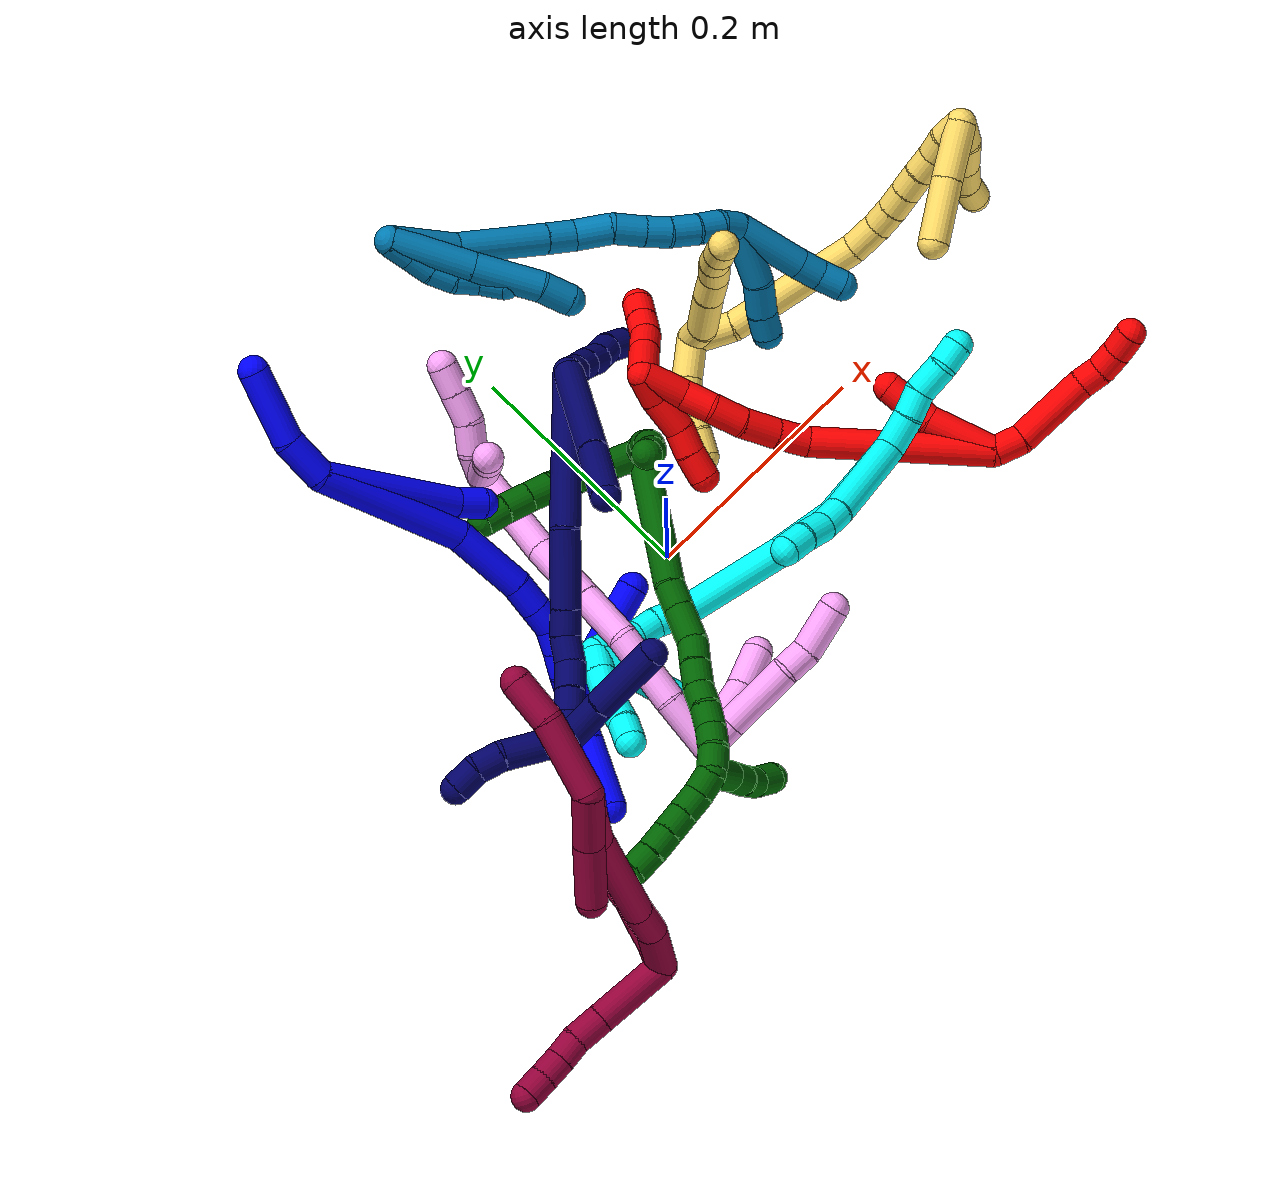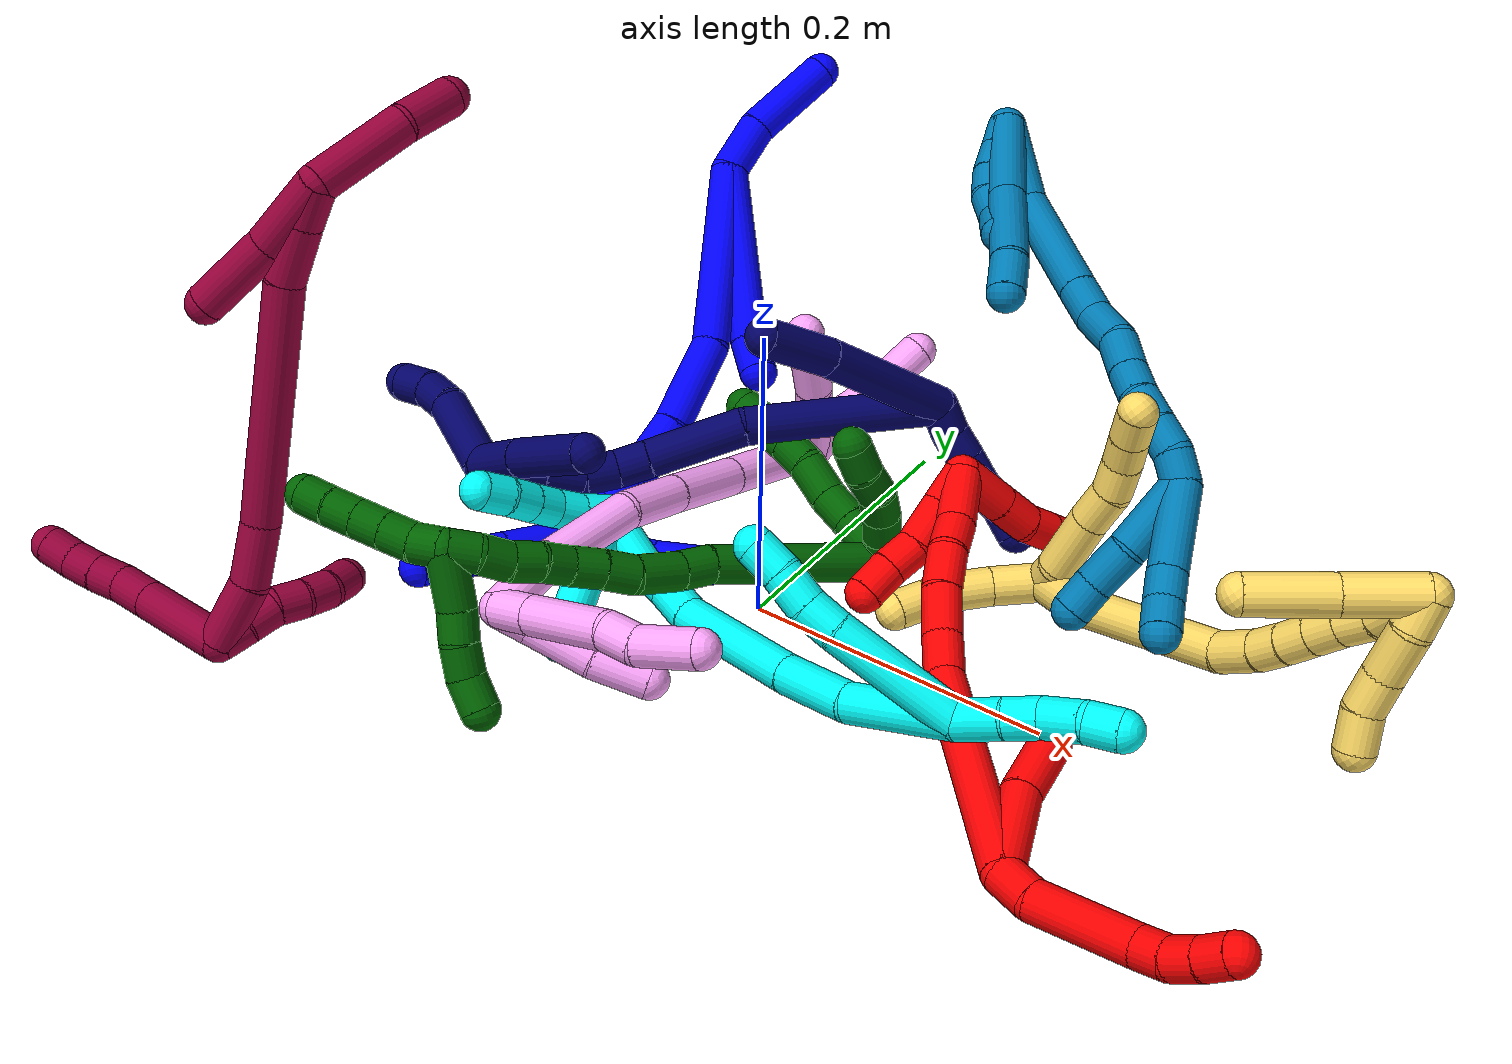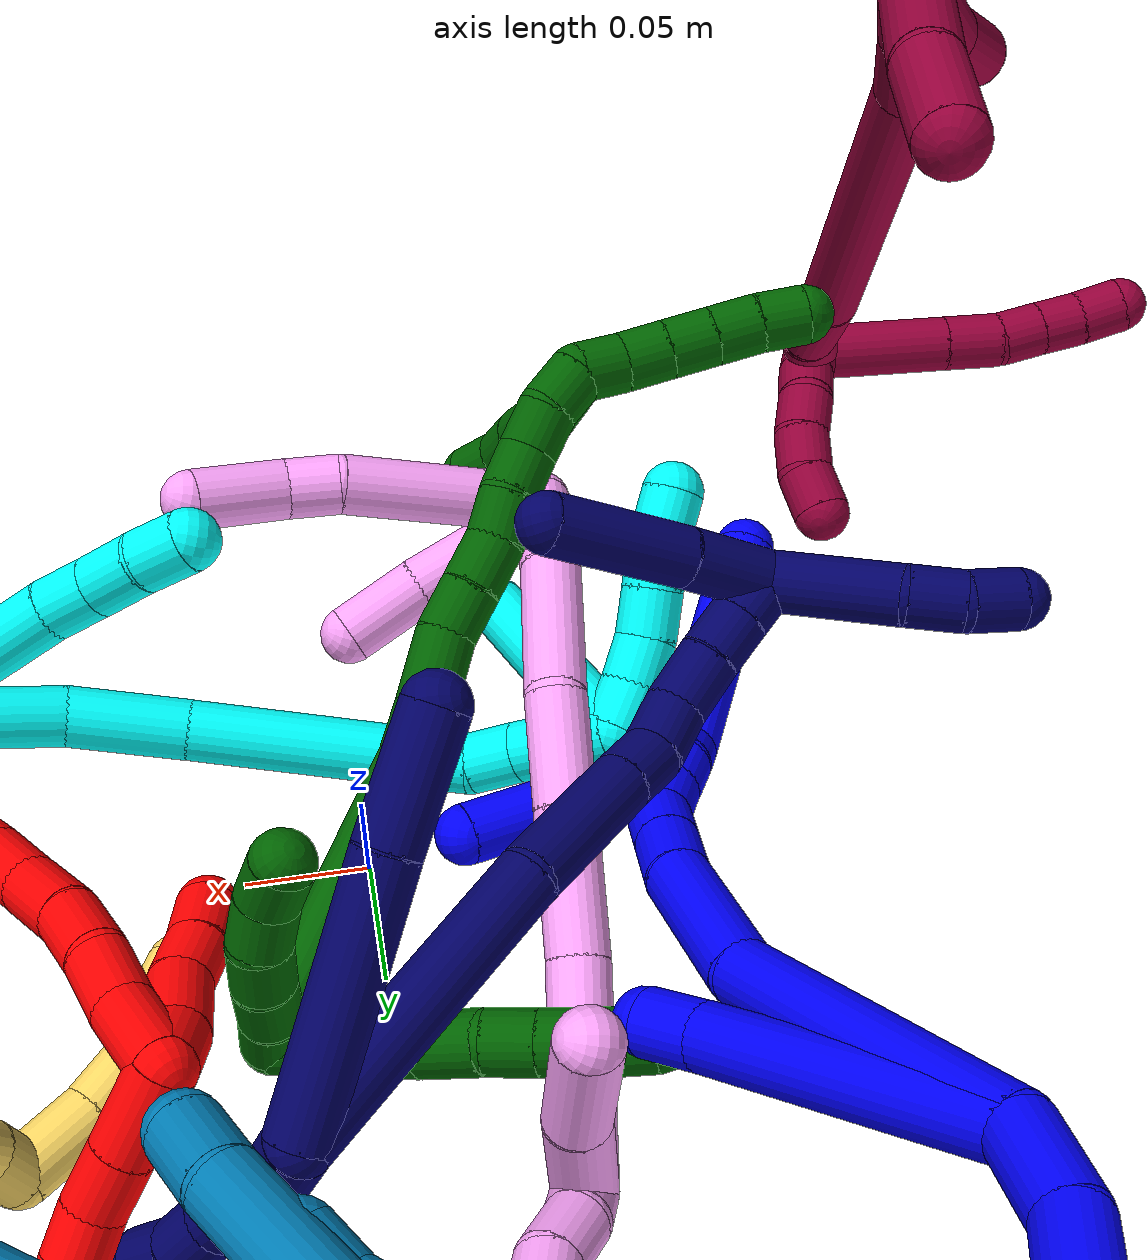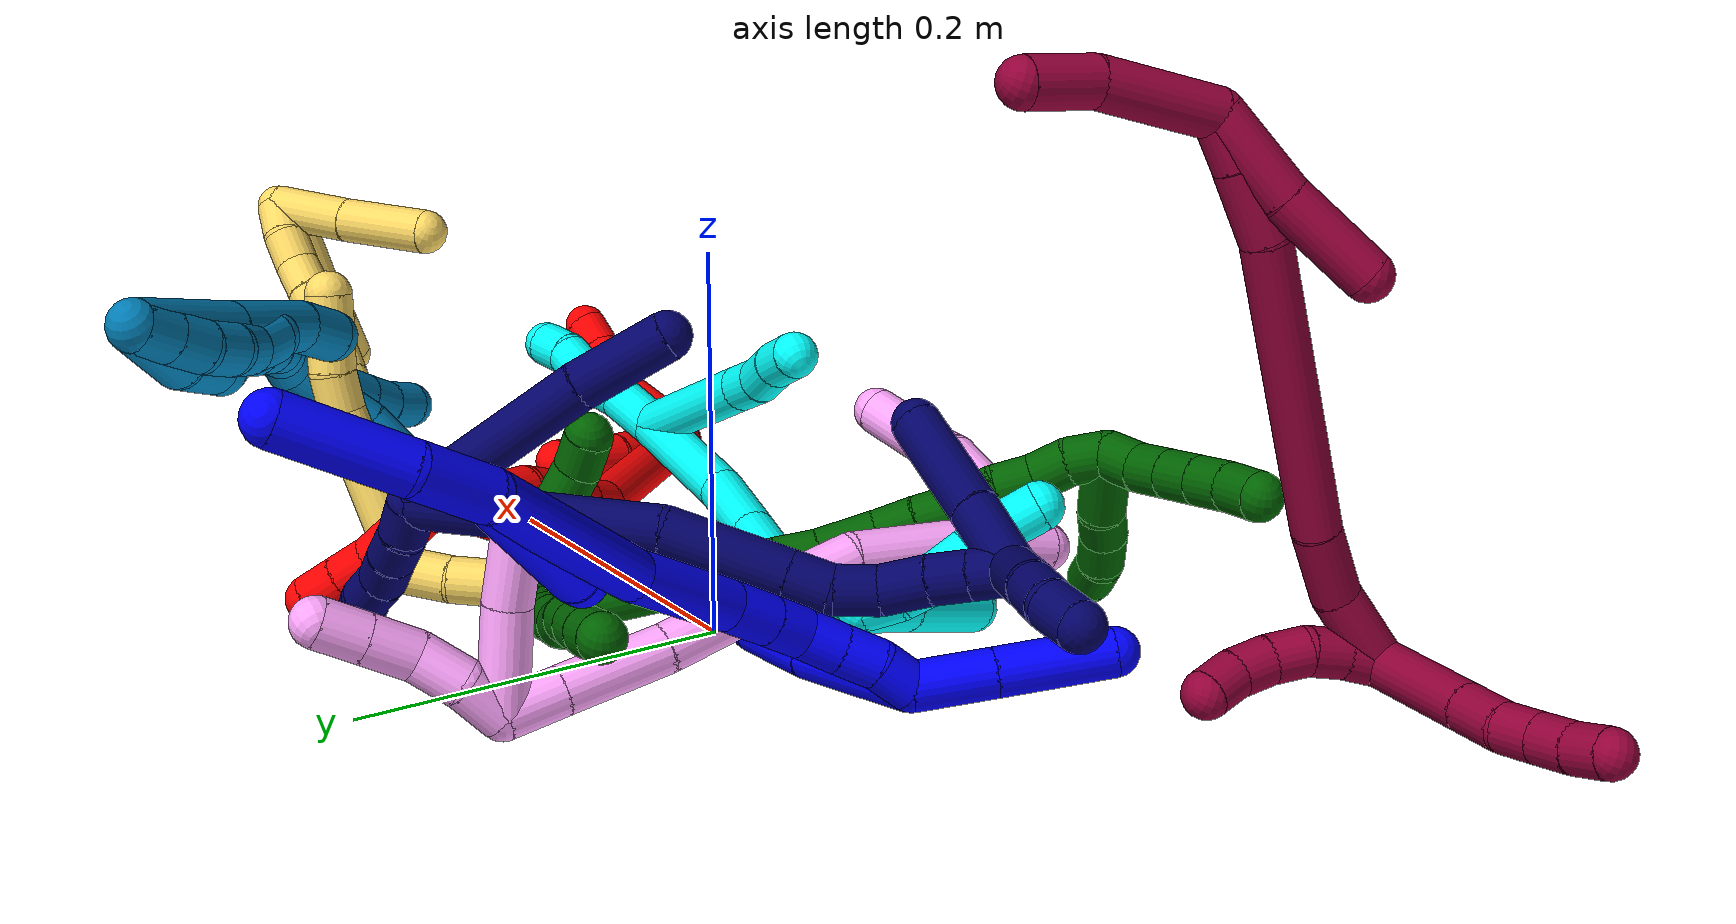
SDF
<sdf version="1.7">
 <world name="default">
  <plugin name="TubeGeneratorPlugin" filename="libtube_generator_plugin.so"/>
  <model name="photoneo_s_sensor">
   <static>1</static>
   <pose>0 0 2 1.57079 1.57079 3.14159</pose>
   <link name="link">
    <inertial><mass>0.1</mass></inertial>
    <sensor name="sensor" type="depth">
     <update_rate>30</update_rate>
     <camera>
      <horizontal_fov>1.22</horizontal_fov>
      <image><width>1920</width><height>1200</height><format>B8G8R8</format></image>
      <clip><near>0.1</near><far>4</far></clip>
      <depth_camera><output>points</output></depth_camera>
     </camera>
     <plugin name="camera_plugin" filename="libgazebo_ros_depth_camera.so">
      <baseline>0.2</baseline>
      <alwaysOn>1</alwaysOn>
      <updateRate>0.0</updateRate>
      <cameraName>camera_ir</cameraName>
      <imageTopicName>/camera/color/image_raw</imageTopicName>
      <cameraInfoTopicName>/camera/color/camera_info</cameraInfoTopicName>
      <depthImageTopicName>/camera/depth/image_raw</depthImageTopicName>
      <depthImageCameraInfoTopicName>/camera/depth/camera_info</depthImageCameraInfoTopicName>
      <pointCloudTopicName>/camera/depth/points</pointCloudTopicName>
      <frameName>fr_optical</frameName>
      <pointCloudCutoff>0.1</pointCloudCutoff>
      <pointCloudCutoffMax>2.0</pointCloudCutoffMax>
      <distortionK1>0</distortionK1>
      <distortionK2>0</distortionK2>
      <distortionK3>0</distortionK3>
      <distortionT1>0</distortionT1>
      <distortionT2>0</distortionT2>
      <CxPrime>0</CxPrime>
      <Cx>0</Cx>
      <Cy>0</Cy>
      <focalLength>0</focalLength>
      <hackBaseline>0</hackBaseline>
     </plugin>
    </sensor>
   </link>
  </model>
  <gravity>0 0 -9.8</gravity>
  <magnetic_field>6e-06 2.3e-05 -4.2e-05</magnetic_field>
  <atmosphere type="adiabatic"/>
  <physics name="default_physics" default="0" type="ode">
   <max_step_size>0.003</max_step_size>
   <real_time_factor>1</real_time_factor>
   <real_time_update_rate>1000</real_time_update_rate>
   <max_contacts>10000</max_contacts>
   <ode>
    <solver>
     <type>quick</type>
     <iters>100</iters>
     <sor>1.3</sor>
     <use_dynamic_moi_rescaling>0</use_dynamic_moi_rescaling>
    </solver>
    <constraints>
     <contact_max_correcting_vel>0</contact_max_correcting_vel>
     <contact_surface_layer>0.001</contact_surface_layer>
     <cfm>0</cfm>
     <erp>0.2</erp>
    </constraints>
   </ode>
  </physics>
  <scene><ambient>0.4 0.4 0.4 1</ambient><background>0.7 0.7 0.7 1</background><shadows>0</shadows></scene>
  <audio><device>default</device></audio>
  <spherical_coordinates>
   <surface_model>EARTH_WGS84</surface_model>
   <latitude_deg>0</latitude_deg>
   <longitude_deg>0</longitude_deg>
   <elevation>0</elevation>
   <heading_deg>0</heading_deg>
  </spherical_coordinates>
  <model name="bin">
   <static>1</static>
   <link name="bottom">
    <collision name="collision-bottom">
     <pose>0 0 -0.01 0 -0 0</pose>
     <geometry><box><size>0.8 0.6 0.02</size></box></geometry>
     <surface>
      <friction><ode><mu>100</mu><mu2>100</mu2></ode></friction>
      <contact><collide_bitmask>65535</collide_bitmask></contact>
     </surface>
    </collision>
   </link>
   <link name="west_wall">
    <collision name="collision-west_wall">
     <pose>-0.41 0 0.1 0 -0 0</pose>
     <geometry><box><size>0.02 0.6 0.2</size></box></geometry>
     <surface>
      <friction><ode><mu>100</mu><mu2>100</mu2></ode></friction>
      <contact><collide_bitmask>65535</collide_bitmask></contact>
     </surface>
    </collision>
   </link>
   <link name="east_wall">
    <collision name="collision-east_wall">
     <pose>0.41 0 0.1 0 -0 0</pose>
     <geometry><box><size>0.02 0.6 0.2</size></box></geometry>
     <surface>
      <friction><ode><mu>100</mu><mu2>100</mu2></ode></friction>
      <contact><collide_bitmask>65535</collide_bitmask></contact>
     </surface>
    </collision>
   </link>
   <link name="south_wall">
    <collision name="collision-south_wall">
     <pose>0 -0.31 0.1 0 -0 0</pose>
     <geometry><box><size>0.8 0.02 0.2</size></box></geometry>
     <surface>
      <friction><ode><mu>100</mu><mu2>100</mu2></ode></friction>
      <contact><collide_bitmask>65535</collide_bitmask></contact>
     </surface>
    </collision>
   </link>
   <link name="north_wall">
    <collision name="collision-north_wall">
     <pose>0 0.31 0.1 0 -0 0</pose>
     <geometry><box><size>0.8 0.02 0.2</size></box></geometry>
     <surface>
      <friction><ode><mu>100</mu><mu2>100</mu2></ode></friction>
      <contact><collide_bitmask>65535</collide_bitmask></contact>
     </surface>
    </collision>
   </link>
  </model>
  <model name="1">
   <static>0</static>
   <link name="1">
    <collision name="collision-cylinder-e_1_2_8">
     <pose>0.000417 -0.000638 -0.0631 3.13149 0.006603 1.15732</pose>
     <geometry><cylinder><radius>0.0125</radius><length>0.126209</length></cylinder></geometry>
     <surface>
      <friction><ode><mu>1.16</mu><mu2>1.16</mu2><slip1>0</slip1><slip2>0</slip2></ode></friction>
      <contact><ode><kp>1e+06</kp><kd>1</kd><max_vel>0</max_vel><min_depth>0.001</min_depth></ode></contact>
     </surface>
    </collision>
    <visual name="visual-cylinder-e_1_2_8">
     <pose>0.000417 -0.000638 -0.0631 3.13149 0.006603 1.15732</pose>
     <geometry><cylinder><radius>0.0125</radius><length>0.126209</length></cylinder></geometry>
     <material><ambient>0 0 1 1</ambient></material>
    </visual>
    <collision name="collision-cylinder-e_2_8_6">
     <pose>0.003226 -0.001074 -0.13785 -3.12428 0.202552 -2.97163</pose>
     <geometry><cylinder><radius>0.0125</radius><length>0.023791</length></cylinder></geometry>
     <surface>
      <friction><ode><mu>1.16</mu><mu2>1.16</mu2><slip1>0</slip1><slip2>0</slip2></ode></friction>
      <contact><ode><kp>1e+06</kp><kd>1</kd><max_vel>0</max_vel><min_depth>0.001</min_depth></ode></contact>
     </surface>
    </collision>
    <visual name="visual-cylinder-e_2_8_6">
     <pose>0.003226 -0.001074 -0.13785 -3.12428 0.202552 -2.97163</pose>
     <geometry><cylinder><radius>0.0125</radius><length>0.023791</length></cylinder></geometry>
     <material><ambient>0 0 1 1</ambient></material>
    </visual>
    <collision name="collision-cylinder-e_1_2_9">
     <pose>0.005727 0.00984 0.01571 -0.559576 0.299655 -0.086694</pose>
     <geometry><cylinder><radius>0.0125</radius><length>0.038803</length></cylinder></geometry>
     <surface>
      <friction><ode><mu>1.16</mu><mu2>1.16</mu2><slip1>0</slip1><slip2>0</slip2></ode></friction>
      <contact><ode><kp>1e+06</kp><kd>1</kd><max_vel>0</max_vel><min_depth>0.001</min_depth></ode></contact>
     </surface>
    </collision>
    <visual name="visual-cylinder-e_1_2_9">
     <pose>0.005727 0.00984 0.01571 -0.559576 0.299655 -0.086694</pose>
     <geometry><cylinder><radius>0.0125</radius><length>0.038803</length></cylinder></geometry>
     <material><ambient>0 0 1 1</ambient></material>
    </visual>
    <collision name="collision-cylinder-e_2_9_5">
     <pose>0.026149 0.039052 0.049995 -0.806385 0.500922 -0.217397</pose>
     <geometry><cylinder><radius>0.0125</radius><length>0.061197</length></cylinder></geometry>
     <surface>
      <friction><ode><mu>1.16</mu><mu2>1.16</mu2><slip1>0</slip1><slip2>0</slip2></ode></friction>
      <contact><ode><kp>1e+06</kp><kd>1</kd><max_vel>0</max_vel><min_depth>0.001</min_depth></ode></contact>
     </surface>
    </collision>
    <visual name="visual-cylinder-e_2_9_5">
     <pose>0.026149 0.039052 0.049995 -0.806385 0.500922 -0.217397</pose>
     <geometry><cylinder><radius>0.0125</radius><length>0.061197</length></cylinder></geometry>
     <material><ambient>0 0 1 1</ambient></material>
    </visual>
    <collision name="collision-cylinder-e_1_2_10">
     <pose>-0.005009 -0.01286 -0.063945 2.94313 -0.076643 -0.735206</pose>
     <geometry><cylinder><radius>0.0125</radius><length>0.130835</length></cylinder></geometry>
     <surface>
      <friction><ode><mu>1.16</mu><mu2>1.16</mu2><slip1>0</slip1><slip2>0</slip2></ode></friction>
      <contact><ode><kp>1e+06</kp><kd>1</kd><max_vel>0</max_vel><min_depth>0.001</min_depth></ode></contact>
     </surface>
    </collision>
    <visual name="visual-cylinder-e_1_2_10">
     <pose>-0.005009 -0.01286 -0.063945 2.94313 -0.076643 -0.735206</pose>
     <geometry><cylinder><radius>0.0125</radius><length>0.130835</length></cylinder></geometry>
     <material><ambient>0 0 1 1</ambient></material>
    </visual>
    <collision name="collision-cylinder-e_2_10_11">
     <pose>-0.016788 -0.040157 -0.15518 2.65499 -0.215856 -0.823152</pose>
     <geometry><cylinder><radius>0.0125</radius><length>0.063215</length></cylinder></geometry>
     <surface>
      <friction><ode><mu>1.16</mu><mu2>1.16</mu2><slip1>0</slip1><slip2>0</slip2></ode></friction>
      <contact><ode><kp>1e+06</kp><kd>1</kd><max_vel>0</max_vel><min_depth>0.001</min_depth></ode></contact>
     </surface>
    </collision>
    <visual name="visual-cylinder-e_2_10_11">
     <pose>-0.016788 -0.040157 -0.15518 2.65499 -0.215856 -0.823152</pose>
     <geometry><cylinder><radius>0.0125</radius><length>0.063215</length></cylinder></geometry>
     <material><ambient>0 0 1 1</ambient></material>
    </visual>
    <collision name="collision-cylinder-e_3_11_12">
     <pose>-0.02786 -0.061076 -0.191869 2.53787 -0.360433 -1.05882</pose>
     <geometry><cylinder><radius>0.0125</radius><length>0.0244</length></cylinder></geometry>
     <surface>
      <friction><ode><mu>1.16</mu><mu2>1.16</mu2><slip1>0</slip1><slip2>0</slip2></ode></friction>
      <contact><ode><kp>1e+06</kp><kd>1</kd><max_vel>0</max_vel><min_depth>0.001</min_depth></ode></contact>
     </surface>
    </collision>
    <visual name="visual-cylinder-e_3_11_12">
     <pose>-0.02786 -0.061076 -0.191869 2.53787 -0.360433 -1.05882</pose>
     <geometry><cylinder><radius>0.0125</radius><length>0.0244</length></cylinder></geometry>
     <material><ambient>0 0 1 1</ambient></material>
    </visual>
    <collision name="collision-cylinder-e_4_12_13">
     <pose>-0.035927 -0.073065 -0.209414 2.54712 -0.365559 -1.0859</pose>
     <geometry><cylinder><radius>0.0125</radius><length>0.021059</length></cylinder></geometry>
     <surface>
      <friction><ode><mu>1.16</mu><mu2>1.16</mu2><slip1>0</slip1><slip2>0</slip2></ode></friction>
      <contact><ode><kp>1e+06</kp><kd>1</kd><max_vel>0</max_vel><min_depth>0.001</min_depth></ode></contact>
     </surface>
    </collision>
    <visual name="visual-cylinder-e_4_12_13">
     <pose>-0.035927 -0.073065 -0.209414 2.54712 -0.365559 -1.0859</pose>
     <geometry><cylinder><radius>0.0125</radius><length>0.021059</length></cylinder></geometry>
     <material><ambient>0 0 1 1</ambient></material>
    </visual>
    <collision name="collision-cylinder-e_5_13_14">
     <pose>-0.045599 -0.084839 -0.222916 2.27794 -0.621827 -1.21781</pose>
     <geometry><cylinder><radius>0.0125</radius><length>0.020284</length></cylinder></geometry>
     <surface>
      <friction><ode><mu>1.16</mu><mu2>1.16</mu2><slip1>0</slip1><slip2>0</slip2></ode></friction>
      <contact><ode><kp>1e+06</kp><kd>1</kd><max_vel>0</max_vel><min_depth>0.001</min_depth></ode></contact>
     </surface>
    </collision>
    <visual name="visual-cylinder-e_5_13_14">
     <pose>-0.045599 -0.084839 -0.222916 2.27794 -0.621827 -1.21781</pose>
     <geometry><cylinder><radius>0.0125</radius><length>0.020284</length></cylinder></geometry>
     <material><ambient>0 0 1 1</ambient></material>
    </visual>
    <collision name="collision-cylinder-e_6_14_15">
     <pose>-0.057438 -0.097628 -0.233016 2.19975 -0.634157 -1.14505</pose>
     <geometry><cylinder><radius>0.0125</radius><length>0.020022</length></cylinder></geometry>
     <surface>
      <friction><ode><mu>1.16</mu><mu2>1.16</mu2><slip1>0</slip1><slip2>0</slip2></ode></friction>
      <contact><ode><kp>1e+06</kp><kd>1</kd><max_vel>0</max_vel><min_depth>0.001</min_depth></ode></contact>
     </surface>
    </collision>
    <visual name="visual-cylinder-e_6_14_15">
     <pose>-0.057438 -0.097628 -0.233016 2.19975 -0.634157 -1.14505</pose>
     <geometry><cylinder><radius>0.0125</radius><length>0.020022</length></cylinder></geometry>
     <material><ambient>0 0 1 1</ambient></material>
    </visual>
    <collision name="collision-cylinder-e_7_15_1">
     <pose>-0.069968 -0.108653 -0.243928 2.51086 -0.712513 -1.702</pose>
     <geometry><cylinder><radius>0.0125</radius><length>0.020184</length></cylinder></geometry>
     <surface>
      <friction><ode><mu>1.16</mu><mu2>1.16</mu2><slip1>0</slip1><slip2>0</slip2></ode></friction>
      <contact><ode><kp>1e+06</kp><kd>1</kd><max_vel>0</max_vel><min_depth>0.001</min_depth></ode></contact>
     </surface>
    </collision>
    <visual name="visual-cylinder-e_7_15_1">
     <pose>-0.069968 -0.108653 -0.243928 2.51086 -0.712513 -1.702</pose>
     <geometry><cylinder><radius>0.0125</radius><length>0.020184</length></cylinder></geometry>
     <material><ambient>0 0 1 1</ambient></material>
    </visual>
    <collision name="collision-cylinder-e_1_1_16">
     <pose>-0.081042 -0.132873 -0.254249 1.77843 -0.218636 -0.26894</pose>
     <geometry><cylinder><radius>0.0125</radius><length>0.04128</length></cylinder></geometry>
     <surface>
      <friction><ode><mu>1.16</mu><mu2>1.16</mu2><slip1>0</slip1><slip2>0</slip2></ode></friction>
      <contact><ode><kp>1e+06</kp><kd>1</kd><max_vel>0</max_vel><min_depth>0.001</min_depth></ode></contact>
     </surface>
    </collision>
    <visual name="visual-cylinder-e_1_1_16">
     <pose>-0.081042 -0.132873 -0.254249 1.77843 -0.218636 -0.26894</pose>
     <geometry><cylinder><radius>0.0125</radius><length>0.04128</length></cylinder></geometry>
     <material><ambient>0 0 1 1</ambient></material>
    </visual>
    <collision name="collision-cylinder-e_2_16_4">
     <pose>-0.091769 -0.180664 -0.264293 1.77759 -0.214527 -0.263682</pose>
     <geometry><cylinder><radius>0.0125</radius><length>0.05872</length></cylinder></geometry>
     <surface>
      <friction><ode><mu>1.16</mu><mu2>1.16</mu2><slip1>0</slip1><slip2>0</slip2></ode></friction>
      <contact><ode><kp>1e+06</kp><kd>1</kd><max_vel>0</max_vel><min_depth>0.001</min_depth></ode></contact>
     </surface>
    </collision>
    <visual name="visual-cylinder-e_2_16_4">
     <pose>-0.091769 -0.180664 -0.264293 1.77759 -0.214527 -0.263682</pose>
     <geometry><cylinder><radius>0.0125</radius><length>0.05872</length></cylinder></geometry>
     <material><ambient>0 0 1 1</ambient></material>
    </visual>
    <collision name="collision-cylinder-e_1_1_17">
     <pose>-0.054383 -0.092874 -0.261838 -2.09555 0.757915 -1.20882</pose>
     <geometry><cylinder><radius>0.0125</radius><length>0.06454</length></cylinder></geometry>
     <surface>
      <friction><ode><mu>1.16</mu><mu2>1.16</mu2><slip1>0</slip1><slip2>0</slip2></ode></friction>
      <contact><ode><kp>1e+06</kp><kd>1</kd><max_vel>0</max_vel><min_depth>0.001</min_depth></ode></contact>
     </surface>
    </collision>
    <visual name="visual-cylinder-e_1_1_17">
     <pose>-0.054383 -0.092874 -0.261838 -2.09555 0.757915 -1.20882</pose>
     <geometry><cylinder><radius>0.0125</radius><length>0.06454</length></cylinder></geometry>
     <material><ambient>0 0 1 1</ambient></material>
    </visual>
    <collision name="collision-cylinder-e_2_17_3">
     <pose>-0.018395 -0.062832 -0.278922 -2.07171 0.892494 -1.35845</pose>
     <geometry><cylinder><radius>0.0125</radius><length>0.03546</length></cylinder></geometry>
     <surface>
      <friction><ode><mu>1.16</mu><mu2>1.16</mu2><slip1>0</slip1><slip2>0</slip2></ode></friction>
      <contact><ode><kp>1e+06</kp><kd>1</kd><max_vel>0</max_vel><min_depth>0.001</min_depth></ode></contact>
     </surface>
    </collision>
    <visual name="visual-cylinder-e_2_17_3">
     <pose>-0.018395 -0.062832 -0.278922 -2.07171 0.892494 -1.35845</pose>
     <geometry><cylinder><radius>0.0125</radius><length>0.03546</length></cylinder></geometry>
     <material><ambient>0 0 1 1</ambient></material>
    </visual>
    <collision name="collision-sphere-3">
     <pose>-0.004589 -0.053074 -0.284265 0 -0 0</pose>
     <geometry><sphere><radius>0.0125</radius></sphere></geometry>
     <surface>
      <friction><ode><mu>1.16</mu><mu2>1.16</mu2><slip1>0</slip1><slip2>0</slip2></ode></friction>
      <contact><ode><kp>1e+06</kp><kd>1</kd><max_vel>0</max_vel><min_depth>0.001</min_depth></ode></contact>
     </surface>
    </collision>
    <visual name="visual-sphere-3">
     <pose>-0.004589 -0.053074 -0.284265 0 -0 0</pose>
     <geometry><sphere><radius>0.0125</radius></sphere></geometry>
     <material><ambient>0 0 1 1</ambient></material>
    </visual>
    <collision name="collision-sphere-17">
     <pose>-0.0322 -0.07259 -0.27358 0 -0 0</pose>
     <geometry><sphere><radius>0.0125</radius></sphere></geometry>
     <surface>
      <friction><ode><mu>1.16</mu><mu2>1.16</mu2><slip1>0</slip1><slip2>0</slip2></ode></friction>
      <contact><ode><kp>1e+06</kp><kd>1</kd><max_vel>0</max_vel><min_depth>0.001</min_depth></ode></contact>
     </surface>
    </collision>
    <visual name="visual-sphere-17">
     <pose>-0.0322 -0.07259 -0.27358 0 -0 0</pose>
     <geometry><sphere><radius>0.0125</radius></sphere></geometry>
     <material><ambient>0 0 1 1</ambient></material>
    </visual>
    <collision name="collision-sphere-4">
     <pose>-0.098019 -0.20874 -0.270183 0 -0 0</pose>
     <geometry><sphere><radius>0.0125</radius></sphere></geometry>
     <surface>
      <friction><ode><mu>1.16</mu><mu2>1.16</mu2><slip1>0</slip1><slip2>0</slip2></ode></friction>
      <contact><ode><kp>1e+06</kp><kd>1</kd><max_vel>0</max_vel><min_depth>0.001</min_depth></ode></contact>
     </surface>
    </collision>
    <visual name="visual-sphere-4">
     <pose>-0.098019 -0.20874 -0.270183 0 -0 0</pose>
     <geometry><sphere><radius>0.0125</radius></sphere></geometry>
     <material><ambient>0 0 1 1</ambient></material>
    </visual>
    <collision name="collision-sphere-16">
     <pose>-0.085519 -0.152588 -0.258403 0 -0 0</pose>
     <geometry><sphere><radius>0.0125</radius></sphere></geometry>
     <surface>
      <friction><ode><mu>1.16</mu><mu2>1.16</mu2><slip1>0</slip1><slip2>0</slip2></ode></friction>
      <contact><ode><kp>1e+06</kp><kd>1</kd><max_vel>0</max_vel><min_depth>0.001</min_depth></ode></contact>
     </surface>
    </collision>
    <visual name="visual-sphere-16">
     <pose>-0.085519 -0.152588 -0.258403 0 -0 0</pose>
     <geometry><sphere><radius>0.0125</radius></sphere></geometry>
     <material><ambient>0 0 1 1</ambient></material>
    </visual>
    <collision name="collision-sphere-1">
     <pose>-0.076565 -0.113157 -0.250096 0 -0 0</pose>
     <geometry><sphere><radius>0.0125</radius></sphere></geometry>
     <surface>
      <friction><ode><mu>1.16</mu><mu2>1.16</mu2><slip1>0</slip1><slip2>0</slip2></ode></friction>
      <contact><ode><kp>1e+06</kp><kd>1</kd><max_vel>0</max_vel><min_depth>0.001</min_depth></ode></contact>
     </surface>
    </collision>
    <visual name="visual-sphere-1">
     <pose>-0.076565 -0.113157 -0.250096 0 -0 0</pose>
     <geometry><sphere><radius>0.0125</radius></sphere></geometry>
     <material><ambient>0 0 1 1</ambient></material>
    </visual>
    <collision name="collision-sphere-15">
     <pose>-0.06337 -0.104149 -0.237761 0 -0 0</pose>
     <geometry><sphere><radius>0.0125</radius></sphere></geometry>
     <surface>
      <friction><ode><mu>1.16</mu><mu2>1.16</mu2><slip1>0</slip1><slip2>0</slip2></ode></friction>
      <contact><ode><kp>1e+06</kp><kd>1</kd><max_vel>0</max_vel><min_depth>0.001</min_depth></ode></contact>
     </surface>
    </collision>
    <visual name="visual-sphere-15">
     <pose>-0.06337 -0.104149 -0.237761 0 -0 0</pose>
     <geometry><sphere><radius>0.0125</radius></sphere></geometry>
     <material><ambient>0 0 1 1</ambient></material>
    </visual>
    <collision name="collision-sphere-14">
     <pose>-0.051507 -0.091106 -0.228272 0 -0 0</pose>
     <geometry><sphere><radius>0.0125</radius></sphere></geometry>
     <surface>
      <friction><ode><mu>1.16</mu><mu2>1.16</mu2><slip1>0</slip1><slip2>0</slip2></ode></friction>
      <contact><ode><kp>1e+06</kp><kd>1</kd><max_vel>0</max_vel><min_depth>0.001</min_depth></ode></contact>
     </surface>
    </collision>
    <visual name="visual-sphere-14">
     <pose>-0.051507 -0.091106 -0.228272 0 -0 0</pose>
     <geometry><sphere><radius>0.0125</radius></sphere></geometry>
     <material><ambient>0 0 1 1</ambient></material>
    </visual>
    <collision name="collision-sphere-13">
     <pose>-0.039691 -0.078573 -0.217561 0 -0 0</pose>
     <geometry><sphere><radius>0.0125</radius></sphere></geometry>
     <surface>
      <friction><ode><mu>1.16</mu><mu2>1.16</mu2><slip1>0</slip1><slip2>0</slip2></ode></friction>
      <contact><ode><kp>1e+06</kp><kd>1</kd><max_vel>0</max_vel><min_depth>0.001</min_depth></ode></contact>
     </surface>
    </collision>
    <visual name="visual-sphere-13">
     <pose>-0.039691 -0.078573 -0.217561 0 -0 0</pose>
     <geometry><sphere><radius>0.0125</radius></sphere></geometry>
     <material><ambient>0 0 1 1</ambient></material>
    </visual>
    <collision name="collision-sphere-12">
     <pose>-0.032163 -0.067557 -0.201267 0 -0 0</pose>
     <geometry><sphere><radius>0.0125</radius></sphere></geometry>
     <surface>
      <friction><ode><mu>1.16</mu><mu2>1.16</mu2><slip1>0</slip1><slip2>0</slip2></ode></friction>
      <contact><ode><kp>1e+06</kp><kd>1</kd><max_vel>0</max_vel><min_depth>0.001</min_depth></ode></contact>
     </surface>
    </collision>
    <visual name="visual-sphere-12">
     <pose>-0.032163 -0.067557 -0.201267 0 -0 0</pose>
     <geometry><sphere><radius>0.0125</radius></sphere></geometry>
     <material><ambient>0 0 1 1</ambient></material>
    </visual>
    <collision name="collision-sphere-11">
     <pose>-0.023557 -0.054595 -0.182471 0 -0 0</pose>
     <geometry><sphere><radius>0.0125</radius></sphere></geometry>
     <surface>
      <friction><ode><mu>1.16</mu><mu2>1.16</mu2><slip1>0</slip1><slip2>0</slip2></ode></friction>
      <contact><ode><kp>1e+06</kp><kd>1</kd><max_vel>0</max_vel><min_depth>0.001</min_depth></ode></contact>
     </surface>
    </collision>
    <visual name="visual-sphere-11">
     <pose>-0.023557 -0.054595 -0.182471 0 -0 0</pose>
     <geometry><sphere><radius>0.0125</radius></sphere></geometry>
     <material><ambient>0 0 1 1</ambient></material>
    </visual>
    <collision name="collision-sphere-8">
     <pose>0.000833 -0.001276 -0.1262 0 -0 0</pose>
     <geometry><sphere><radius>0.0125</radius></sphere></geometry>
     <surface>
      <friction><ode><mu>1.16</mu><mu2>1.16</mu2><slip1>0</slip1><slip2>0</slip2></ode></friction>
      <contact><ode><kp>1e+06</kp><kd>1</kd><max_vel>0</max_vel><min_depth>0.001</min_depth></ode></contact>
     </surface>
    </collision>
    <visual name="visual-sphere-8">
     <pose>0.000833 -0.001276 -0.1262 0 -0 0</pose>
     <geometry><sphere><radius>0.0125</radius></sphere></geometry>
     <material><ambient>0 0 1 1</ambient></material>
    </visual>
    <collision name="collision-sphere-2">
     <geometry><sphere><radius>0.0125</radius></sphere></geometry>
     <surface>
      <friction><ode><mu>1.16</mu><mu2>1.16</mu2><slip1>0</slip1><slip2>0</slip2></ode></friction>
      <contact><ode><kp>1e+06</kp><kd>1</kd><max_vel>0</max_vel><min_depth>0.001</min_depth></ode></contact>
     </surface>
    </collision>
    <visual name="visual-sphere-2">
     <geometry><sphere><radius>0.0125</radius></sphere></geometry>
     <material><ambient>0 0 1 1</ambient></material>
    </visual>
    <collision name="collision-sphere-9">
     <pose>0.011454 0.01968 0.031419 0 -0 0</pose>
     <geometry><sphere><radius>0.0125</radius></sphere></geometry>
     <surface>
      <friction><ode><mu>1.16</mu><mu2>1.16</mu2><slip1>0</slip1><slip2>0</slip2></ode></friction>
      <contact><ode><kp>1e+06</kp><kd>1</kd><max_vel>0</max_vel><min_depth>0.001</min_depth></ode></contact>
     </surface>
    </collision>
    <visual name="visual-sphere-9">
     <pose>0.011454 0.01968 0.031419 0 -0 0</pose>
     <geometry><sphere><radius>0.0125</radius></sphere></geometry>
     <material><ambient>0 0 1 1</ambient></material>
    </visual>
    <collision name="collision-sphere-6">
     <pose>0.005619 -0.000872 -0.149501 0 -0 0</pose>
     <geometry><sphere><radius>0.0125</radius></sphere></geometry>
     <surface>
      <friction><ode><mu>1.16</mu><mu2>1.16</mu2><slip1>0</slip1><slip2>0</slip2></ode></friction>
      <contact><ode><kp>1e+06</kp><kd>1</kd><max_vel>0</max_vel><min_depth>0.001</min_depth></ode></contact>
     </surface>
    </collision>
    <visual name="visual-sphere-6">
     <pose>0.005619 -0.000872 -0.149501 0 -0 0</pose>
     <geometry><sphere><radius>0.0125</radius></sphere></geometry>
     <material><ambient>0 0 1 1</ambient></material>
    </visual>
    <collision name="collision-sphere-5">
     <pose>0.040843 0.058424 0.068571 0 -0 0</pose>
     <geometry><sphere><radius>0.0125</radius></sphere></geometry>
     <surface>
      <friction><ode><mu>1.16</mu><mu2>1.16</mu2><slip1>0</slip1><slip2>0</slip2></ode></friction>
      <contact><ode><kp>1e+06</kp><kd>1</kd><max_vel>0</max_vel><min_depth>0.001</min_depth></ode></contact>
     </surface>
    </collision>
    <visual name="visual-sphere-5">
     <pose>0.040843 0.058424 0.068571 0 -0 0</pose>
     <geometry><sphere><radius>0.0125</radius></sphere></geometry>
     <material><ambient>0 0 1 1</ambient></material>
    </visual>
    <collision name="collision-sphere-10">
     <pose>-0.010018 -0.02572 -0.12789 0 -0 0</pose>
     <geometry><sphere><radius>0.0125</radius></sphere></geometry>
     <surface>
      <friction><ode><mu>1.16</mu><mu2>1.16</mu2><slip1>0</slip1><slip2>0</slip2></ode></friction>
      <contact><ode><kp>1e+06</kp><kd>1</kd><max_vel>0</max_vel><min_depth>0.001</min_depth></ode></contact>
     </surface>
    </collision>
    <visual name="visual-sphere-10">
     <pose>-0.010018 -0.02572 -0.12789 0 -0 0</pose>
     <geometry><sphere><radius>0.0125</radius></sphere></geometry>
     <material><ambient>0 0 1 1</ambient></material>
    </visual>
    <inertial>
     <pose>-0.023446 -0.046358 -0.135676 0 -0 0</pose>
     <mass>0.75</mass>
     <inertia><ixx>0.00026</ixx><ixy>0</ixy><ixz>0</ixz><iyy>-0.000219</iyy><iyz>0</iyz><izz>9e-06</izz></inertia>
    </inertial>
   </link>
   <pose>-0.172013 0.208932 0.165969 -0.608417 -0.763442 -0.021243</pose>
  </model>
  <model name="2">
   <static>0</static>
   <link name="2">
    <collision name="collision-cylinder-e_1_2_8">
     <pose>-0.007014 0.004807 0.008704 -0.504643 -0.614379 0.163212</pose>
     <geometry><cylinder><radius>0.0125</radius><length>0.024337</length></cylinder></geometry>
     <surface>
      <friction><ode><mu>1.16</mu><mu2>1.16</mu2><slip1>0</slip1><slip2>0</slip2></ode></friction>
      <contact><ode><kp>1e+06</kp><kd>1</kd><max_vel>0</max_vel><min_depth>0.001</min_depth></ode></contact>
     </surface>
    </collision>
    <visual name="visual-cylinder-e_1_2_8">
     <pose>-0.007014 0.004807 0.008704 -0.504643 -0.614379 0.163212</pose>
     <geometry><cylinder><radius>0.0125</radius><length>0.024337</length></cylinder></geometry>
     <material><ambient>1 0 0 1</ambient></material>
    </visual>
    <collision name="collision-cylinder-e_2_8_9">
     <pose>-0.037831 0.02604 0.032557 -0.825769 -0.816978 0.374772</pose>
     <geometry><cylinder><radius>0.0125</radius><length>0.065295</length></cylinder></geometry>
     <surface>
      <friction><ode><mu>1.16</mu><mu2>1.16</mu2><slip1>0</slip1><slip2>0</slip2></ode></friction>
      <contact><ode><kp>1e+06</kp><kd>1</kd><max_vel>0</max_vel><min_depth>0.001</min_depth></ode></contact>
     </surface>
    </collision>
    <visual name="visual-cylinder-e_2_8_9">
     <pose>-0.037831 0.02604 0.032557 -0.825769 -0.816978 0.374772</pose>
     <geometry><cylinder><radius>0.0125</radius><length>0.065295</length></cylinder></geometry>
     <material><ambient>1 0 0 1</ambient></material>
    </visual>
    <collision name="collision-cylinder-e_3_9_10">
     <pose>-0.069912 0.044988 0.05298 -0.446187 -0.955904 0.233969</pose>
     <geometry><cylinder><radius>0.0125</radius><length>0.020269</length></cylinder></geometry>
     <surface>
      <friction><ode><mu>1.16</mu><mu2>1.16</mu2><slip1>0</slip1><slip2>0</slip2></ode></friction>
      <contact><ode><kp>1e+06</kp><kd>1</kd><max_vel>0</max_vel><min_depth>0.001</min_depth></ode></contact>
     </surface>
    </collision>
    <visual name="visual-cylinder-e_3_9_10">
     <pose>-0.069912 0.044988 0.05298 -0.446187 -0.955904 0.233969</pose>
     <geometry><cylinder><radius>0.0125</radius><length>0.020269</length></cylinder></geometry>
     <material><ambient>1 0 0 1</ambient></material>
    </visual>
    <collision name="collision-cylinder-e_4_10_11">
     <pose>-0.087753 0.049076 0.060917 -0.531592 -1.25831 0.391213</pose>
     <geometry><cylinder><radius>0.0125</radius><length>0.020098</length></cylinder></geometry>
     <surface>
      <friction><ode><mu>1.16</mu><mu2>1.16</mu2><slip1>0</slip1><slip2>0</slip2></ode></friction>
      <contact><ode><kp>1e+06</kp><kd>1</kd><max_vel>0</max_vel><min_depth>0.001</min_depth></ode></contact>
     </surface>
    </collision>
    <visual name="visual-cylinder-e_4_10_11">
     <pose>-0.087753 0.049076 0.060917 -0.531592 -1.25831 0.391213</pose>
     <geometry><cylinder><radius>0.0125</radius><length>0.020098</length></cylinder></geometry>
     <material><ambient>1 0 0 1</ambient></material>
    </visual>
    <collision name="collision-cylinder-e_5_11_6">
     <pose>-0.107112 0.051804 0.06522 -0.616298 -1.36846 0.508028</pose>
     <geometry><cylinder><radius>0.0125</radius><length>0.020002</length></cylinder></geometry>
     <surface>
      <friction><ode><mu>1.16</mu><mu2>1.16</mu2><slip1>0</slip1><slip2>0</slip2></ode></friction>
      <contact><ode><kp>1e+06</kp><kd>1</kd><max_vel>0</max_vel><min_depth>0.001</min_depth></ode></contact>
     </surface>
    </collision>
    <visual name="visual-cylinder-e_5_11_6">
     <pose>-0.107112 0.051804 0.06522 -0.616298 -1.36846 0.508028</pose>
     <geometry><cylinder><radius>0.0125</radius><length>0.020002</length></cylinder></geometry>
     <material><ambient>1 0 0 1</ambient></material>
    </visual>
    <collision name="collision-cylinder-e_1_2_12">
     <pose>0.000442 0.005669 -0.028659 -2.9463 0.015137 -0.154221</pose>
     <geometry><cylinder><radius>0.0125</radius><length>0.058436</length></cylinder></geometry>
     <surface>
      <friction><ode><mu>1.16</mu><mu2>1.16</mu2><slip1>0</slip1><slip2>0</slip2></ode></friction>
      <contact><ode><kp>1e+06</kp><kd>1</kd><max_vel>0</max_vel><min_depth>0.001</min_depth></ode></contact>
     </surface>
    </collision>
    <visual name="visual-cylinder-e_1_2_12">
     <pose>0.000442 0.005669 -0.028659 -2.9463 0.015137 -0.154221</pose>
     <geometry><cylinder><radius>0.0125</radius><length>0.058436</length></cylinder></geometry>
     <material><ambient>1 0 0 1</ambient></material>
    </visual>
    <collision name="collision-cylinder-e_2_12_5">
     <pose>-0.002635 0.018447 -0.076527 -2.78714 -0.170184 0.888919</pose>
     <geometry><cylinder><radius>0.0125</radius><length>0.041564</length></cylinder></geometry>
     <surface>
      <friction><ode><mu>1.16</mu><mu2>1.16</mu2><slip1>0</slip1><slip2>0</slip2></ode></friction>
      <contact><ode><kp>1e+06</kp><kd>1</kd><max_vel>0</max_vel><min_depth>0.001</min_depth></ode></contact>
     </surface>
    </collision>
    <visual name="visual-cylinder-e_2_12_5">
     <pose>-0.002635 0.018447 -0.076527 -2.78714 -0.170184 0.888919</pose>
     <geometry><cylinder><radius>0.0125</radius><length>0.041564</length></cylinder></geometry>
     <material><ambient>1 0 0 1</ambient></material>
    </visual>
    <collision name="collision-cylinder-e_1_2_13">
     <pose>0.021696 -0.0072 -0.071904 3.04179 0.291666 2.48603</pose>
     <geometry><cylinder><radius>0.0125</radius><length>0.1509</length></cylinder></geometry>
     <surface>
      <friction><ode><mu>1.16</mu><mu2>1.16</mu2><slip1>0</slip1><slip2>0</slip2></ode></friction>
      <contact><ode><kp>1e+06</kp><kd>1</kd><max_vel>0</max_vel><min_depth>0.001</min_depth></ode></contact>
     </surface>
    </collision>
    <visual name="visual-cylinder-e_1_2_13">
     <pose>0.021696 -0.0072 -0.071904 3.04179 0.291666 2.48603</pose>
     <geometry><cylinder><radius>0.0125</radius><length>0.1509</length></cylinder></geometry>
     <material><ambient>1 0 0 1</ambient></material>
    </visual>
    <collision name="collision-cylinder-e_2_13_14">
     <pose>0.043401 -0.016537 -0.157438 2.9861 0.000681 0.008746</pose>
     <geometry><cylinder><radius>0.0125</radius><length>0.027594</length></cylinder></geometry>
     <surface>
      <friction><ode><mu>1.16</mu><mu2>1.16</mu2><slip1>0</slip1><slip2>0</slip2></ode></friction>
      <contact><ode><kp>1e+06</kp><kd>1</kd><max_vel>0</max_vel><min_depth>0.001</min_depth></ode></contact>
     </surface>
    </collision>
    <visual name="visual-cylinder-e_2_13_14">
     <pose>0.043401 -0.016537 -0.157438 2.9861 0.000681 0.008746</pose>
     <geometry><cylinder><radius>0.0125</radius><length>0.027594</length></cylinder></geometry>
     <material><ambient>1 0 0 1</ambient></material>
    </visual>
    <collision name="collision-cylinder-e_3_14_15">
     <pose>0.041756 -0.022076 -0.186352 2.9226 -0.105252 -0.893659</pose>
     <geometry><cylinder><radius>0.0125</radius><length>0.031489</length></cylinder></geometry>
     <surface>
      <friction><ode><mu>1.16</mu><mu2>1.16</mu2><slip1>0</slip1><slip2>0</slip2></ode></friction>
      <contact><ode><kp>1e+06</kp><kd>1</kd><max_vel>0</max_vel><min_depth>0.001</min_depth></ode></contact>
     </surface>
    </collision>
    <visual name="visual-cylinder-e_3_14_15">
     <pose>0.041756 -0.022076 -0.186352 2.9226 -0.105252 -0.893659</pose>
     <geometry><cylinder><radius>0.0125</radius><length>0.031489</length></cylinder></geometry>
     <material><ambient>1 0 0 1</ambient></material>
    </visual>
    <collision name="collision-cylinder-e_4_15_16">
     <pose>0.038229 -0.025964 -0.215361 3.10615 -0.135542 -2.6307</pose>
     <geometry><cylinder><radius>0.0125</radius><length>0.027722</length></cylinder></geometry>
     <surface>
      <friction><ode><mu>1.16</mu><mu2>1.16</mu2><slip1>0</slip1><slip2>0</slip2></ode></friction>
      <contact><ode><kp>1e+06</kp><kd>1</kd><max_vel>0</max_vel><min_depth>0.001</min_depth></ode></contact>
     </surface>
    </collision>
    <visual name="visual-cylinder-e_4_15_16">
     <pose>0.038229 -0.025964 -0.215361 3.10615 -0.135542 -2.6307</pose>
     <geometry><cylinder><radius>0.0125</radius><length>0.027722</length></cylinder></geometry>
     <material><ambient>1 0 0 1</ambient></material>
    </visual>
    <collision name="collision-cylinder-e_5_16_17">
     <pose>0.036566 -0.023997 -0.241529 -2.94688 0.016554 -0.169095</pose>
     <geometry><cylinder><radius>0.0125</radius><length>0.025368</length></cylinder></geometry>
     <surface>
      <friction><ode><mu>1.16</mu><mu2>1.16</mu2><slip1>0</slip1><slip2>0</slip2></ode></friction>
      <contact><ode><kp>1e+06</kp><kd>1</kd><max_vel>0</max_vel><min_depth>0.001</min_depth></ode></contact>
     </surface>
    </collision>
    <visual name="visual-cylinder-e_5_16_17">
     <pose>0.036566 -0.023997 -0.241529 -2.94688 0.016554 -0.169095</pose>
     <geometry><cylinder><radius>0.0125</radius><length>0.025368</length></cylinder></geometry>
     <material><ambient>1 0 0 1</ambient></material>
    </visual>
    <collision name="collision-cylinder-e_6_17_1">
     <pose>0.033877 -0.022767 -0.272165 3.07439 -0.15764 -2.33683</pose>
     <geometry><cylinder><radius>0.0125</radius><length>0.036927</length></cylinder></geometry>
     <surface>
      <friction><ode><mu>1.16</mu><mu2>1.16</mu2><slip1>0</slip1><slip2>0</slip2></ode></friction>
      <contact><ode><kp>1e+06</kp><kd>1</kd><max_vel>0</max_vel><min_depth>0.001</min_depth></ode></contact>
     </surface>
    </collision>
    <visual name="visual-cylinder-e_6_17_1">
     <pose>0.033877 -0.022767 -0.272165 3.07439 -0.15764 -2.33683</pose>
     <geometry><cylinder><radius>0.0125</radius><length>0.036927</length></cylinder></geometry>
     <material><ambient>1 0 0 1</ambient></material>
    </visual>
    <collision name="collision-cylinder-e_1_1_18">
     <pose>0.039262 -0.024595 -0.281486 0.067907 0.749932 0.026736</pose>
     <geometry><cylinder><radius>0.0125</radius><length>0.024306</length></cylinder></geometry>
     <surface>
      <friction><ode><mu>1.16</mu><mu2>1.16</mu2><slip1>0</slip1><slip2>0</slip2></ode></friction>
      <contact><ode><kp>1e+06</kp><kd>1</kd><max_vel>0</max_vel><min_depth>0.001</min_depth></ode></contact>
     </surface>
    </collision>
    <visual name="visual-cylinder-e_1_1_18">
     <pose>0.039262 -0.024595 -0.281486 0.067907 0.749932 0.026736</pose>
     <geometry><cylinder><radius>0.0125</radius><length>0.024306</length></cylinder></geometry>
     <material><ambient>1 0 0 1</ambient></material>
    </visual>
    <collision name="collision-cylinder-e_2_18_19">
     <pose>0.055371 -0.027627 -0.259188 0.17895 0.520739 0.047794</pose>
     <geometry><cylinder><radius>0.0125</radius><length>0.031457</length></cylinder></geometry>
     <surface>
      <friction><ode><mu>1.16</mu><mu2>1.16</mu2><slip1>0</slip1><slip2>0</slip2></ode></friction>
      <contact><ode><kp>1e+06</kp><kd>1</kd><max_vel>0</max_vel><min_depth>0.001</min_depth></ode></contact>
     </surface>
    </collision>
    <visual name="visual-cylinder-e_2_18_19">
     <pose>0.055371 -0.027627 -0.259188 0.17895 0.520739 0.047794</pose>
     <geometry><cylinder><radius>0.0125</radius><length>0.031457</length></cylinder></geometry>
     <material><ambient>1 0 0 1</ambient></material>
    </visual>
    <collision name="collision-cylinder-e_3_19_20">
     <pose>0.069887 -0.033991 -0.238296 0.485063 0.670439 0.171948</pose>
     <geometry><cylinder><radius>0.0125</radius><length>0.02154</length></cylinder></geometry>
     <surface>
      <friction><ode><mu>1.16</mu><mu2>1.16</mu2><slip1>0</slip1><slip2>0</slip2></ode></friction>
      <contact><ode><kp>1e+06</kp><kd>1</kd><max_vel>0</max_vel><min_depth>0.001</min_depth></ode></contact>
     </surface>
    </collision>
    <visual name="visual-cylinder-e_3_19_20">
     <pose>0.069887 -0.033991 -0.238296 0.485063 0.670439 0.171948</pose>
     <geometry><cylinder><radius>0.0125</radius><length>0.02154</length></cylinder></geometry>
     <material><ambient>1 0 0 1</ambient></material>
    </visual>
    <collision name="collision-cylinder-e_4_20_4">
     <pose>0.082833 -0.041352 -0.222003 0.370252 0.583635 0.112391</pose>
     <geometry><cylinder><radius>0.0125</radius><length>0.022697</length></cylinder></geometry>
     <surface>
      <friction><ode><mu>1.16</mu><mu2>1.16</mu2><slip1>0</slip1><slip2>0</slip2></ode></friction>
      <contact><ode><kp>1e+06</kp><kd>1</kd><max_vel>0</max_vel><min_depth>0.001</min_depth></ode></contact>
     </surface>
    </collision>
    <visual name="visual-cylinder-e_4_20_4">
     <pose>0.082833 -0.041352 -0.222003 0.370252 0.583635 0.112391</pose>
     <geometry><cylinder><radius>0.0125</radius><length>0.022697</length></cylinder></geometry>
     <material><ambient>1 0 0 1</ambient></material>
    </visual>
    <collision name="collision-cylinder-e_1_1_21">
     <pose>0.032289 -0.006424 -0.290604 -1.58482 0.074465 -0.075516</pose>
     <geometry><cylinder><radius>0.0125</radius><length>0.035237</length></cylinder></geometry>
     <surface>
      <friction><ode><mu>1.16</mu><mu2>1.16</mu2><slip1>0</slip1><slip2>0</slip2></ode></friction>
      <contact><ode><kp>1e+06</kp><kd>1</kd><max_vel>0</max_vel><min_depth>0.001</min_depth></ode></contact>
     </surface>
    </collision>
    <visual name="visual-cylinder-e_1_1_21">
     <pose>0.032289 -0.006424 -0.290604 -1.58482 0.074465 -0.075516</pose>
     <geometry><cylinder><radius>0.0125</radius><length>0.035237</length></cylinder></geometry>
     <material><ambient>1 0 0 1</ambient></material>
    </visual>
    <collision name="collision-cylinder-e_2_21_22">
     <pose>0.034436 0.023451 -0.290937 -1.57778 0.067841 -0.068316</pose>
     <geometry><cylinder><radius>0.0125</radius><length>0.024672</length></cylinder></geometry>
     <surface>
      <friction><ode><mu>1.16</mu><mu2>1.16</mu2><slip1>0</slip1><slip2>0</slip2></ode></friction>
      <contact><ode><kp>1e+06</kp><kd>1</kd><max_vel>0</max_vel><min_depth>0.001</min_depth></ode></contact>
     </surface>
    </collision>
    <visual name="visual-cylinder-e_2_21_22">
     <pose>0.034436 0.023451 -0.290937 -1.57778 0.067841 -0.068316</pose>
     <geometry><cylinder><radius>0.0125</radius><length>0.024672</length></cylinder></geometry>
     <material><ambient>1 0 0 1</ambient></material>
    </visual>
    <collision name="collision-cylinder-e_3_22_23">
     <pose>0.035105 0.045475 -0.293565 -1.82674 -0.016669 0.021592</pose>
     <geometry><cylinder><radius>0.0125</radius><length>0.020091</length></cylinder></geometry>
     <surface>
      <friction><ode><mu>1.16</mu><mu2>1.16</mu2><slip1>0</slip1><slip2>0</slip2></ode></friction>
      <contact><ode><kp>1e+06</kp><kd>1</kd><max_vel>0</max_vel><min_depth>0.001</min_depth></ode></contact>
     </surface>
    </collision>
    <visual name="visual-cylinder-e_3_22_23">
     <pose>0.035105 0.045475 -0.293565 -1.82674 -0.016669 0.021592</pose>
     <geometry><cylinder><radius>0.0125</radius><length>0.020091</length></cylinder></geometry>
     <material><ambient>1 0 0 1</ambient></material>
    </visual>
    <collision name="collision-cylinder-e_4_23_3">
     <pose>0.034825 0.064868 -0.298631 -1.82581 -0.01121 0.014507</pose>
     <geometry><cylinder><radius>0.0125</radius><length>0.020001</length></cylinder></geometry>
     <surface>
      <friction><ode><mu>1.16</mu><mu2>1.16</mu2><slip1>0</slip1><slip2>0</slip2></ode></friction>
      <contact><ode><kp>1e+06</kp><kd>1</kd><max_vel>0</max_vel><min_depth>0.001</min_depth></ode></contact>
     </surface>
    </collision>
    <visual name="visual-cylinder-e_4_23_3">
     <pose>0.034825 0.064868 -0.298631 -1.82581 -0.01121 0.014507</pose>
     <geometry><cylinder><radius>0.0125</radius><length>0.020001</length></cylinder></geometry>
     <material><ambient>1 0 0 1</ambient></material>
    </visual>
    <collision name="collision-sphere-3">
     <pose>0.034713 0.074544 -0.301153 0 -0 0</pose>
     <geometry><sphere><radius>0.0125</radius></sphere></geometry>
     <surface>
      <friction><ode><mu>1.16</mu><mu2>1.16</mu2><slip1>0</slip1><slip2>0</slip2></ode></friction>
      <contact><ode><kp>1e+06</kp><kd>1</kd><max_vel>0</max_vel><min_depth>0.001</min_depth></ode></contact>
     </surface>
    </collision>
    <visual name="visual-sphere-3">
     <pose>0.034713 0.074544 -0.301153 0 -0 0</pose>
     <geometry><sphere><radius>0.0125</radius></sphere></geometry>
     <material><ambient>1 0 0 1</ambient></material>
    </visual>
    <collision name="collision-sphere-23">
     <pose>0.034938 0.055192 -0.296108 0 -0 0</pose>
     <geometry><sphere><radius>0.0125</radius></sphere></geometry>
     <surface>
      <friction><ode><mu>1.16</mu><mu2>1.16</mu2><slip1>0</slip1><slip2>0</slip2></ode></friction>
      <contact><ode><kp>1e+06</kp><kd>1</kd><max_vel>0</max_vel><min_depth>0.001</min_depth></ode></contact>
     </surface>
    </collision>
    <visual name="visual-sphere-23">
     <pose>0.034938 0.055192 -0.296108 0 -0 0</pose>
     <geometry><sphere><radius>0.0125</radius></sphere></geometry>
     <material><ambient>1 0 0 1</ambient></material>
    </visual>
    <collision name="collision-sphere-22">
     <pose>0.035272 0.035758 -0.291023 0 -0 0</pose>
     <geometry><sphere><radius>0.0125</radius></sphere></geometry>
     <surface>
      <friction><ode><mu>1.16</mu><mu2>1.16</mu2><slip1>0</slip1><slip2>0</slip2></ode></friction>
      <contact><ode><kp>1e+06</kp><kd>1</kd><max_vel>0</max_vel><min_depth>0.001</min_depth></ode></contact>
     </surface>
    </collision>
    <visual name="visual-sphere-22">
     <pose>0.035272 0.035758 -0.291023 0 -0 0</pose>
     <geometry><sphere><radius>0.0125</radius></sphere></geometry>
     <material><ambient>1 0 0 1</ambient></material>
    </visual>
    <collision name="collision-sphere-21">
     <pose>0.0336 0.011144 -0.290851 0 -0 0</pose>
     <geometry><sphere><radius>0.0125</radius></sphere></geometry>
     <surface>
      <friction><ode><mu>1.16</mu><mu2>1.16</mu2><slip1>0</slip1><slip2>0</slip2></ode></friction>
      <contact><ode><kp>1e+06</kp><kd>1</kd><max_vel>0</max_vel><min_depth>0.001</min_depth></ode></contact>
     </surface>
    </collision>
    <visual name="visual-sphere-21">
     <pose>0.0336 0.011144 -0.290851 0 -0 0</pose>
     <geometry><sphere><radius>0.0125</radius></sphere></geometry>
     <material><ambient>1 0 0 1</ambient></material>
    </visual>
    <collision name="collision-sphere-4">
     <pose>0.089087 -0.044779 -0.213175 0 -0 0</pose>
     <geometry><sphere><radius>0.0125</radius></sphere></geometry>
     <surface>
      <friction><ode><mu>1.16</mu><mu2>1.16</mu2><slip1>0</slip1><slip2>0</slip2></ode></friction>
      <contact><ode><kp>1e+06</kp><kd>1</kd><max_vel>0</max_vel><min_depth>0.001</min_depth></ode></contact>
     </surface>
    </collision>
    <visual name="visual-sphere-4">
     <pose>0.089087 -0.044779 -0.213175 0 -0 0</pose>
     <geometry><sphere><radius>0.0125</radius></sphere></geometry>
     <material><ambient>1 0 0 1</ambient></material>
    </visual>
    <collision name="collision-sphere-20">
     <pose>0.076579 -0.037925 -0.230831 0 -0 0</pose>
     <geometry><sphere><radius>0.0125</radius></sphere></geometry>
     <surface>
      <friction><ode><mu>1.16</mu><mu2>1.16</mu2><slip1>0</slip1><slip2>0</slip2></ode></friction>
      <contact><ode><kp>1e+06</kp><kd>1</kd><max_vel>0</max_vel><min_depth>0.001</min_depth></ode></contact>
     </surface>
    </collision>
    <visual name="visual-sphere-20">
     <pose>0.076579 -0.037925 -0.230831 0 -0 0</pose>
     <geometry><sphere><radius>0.0125</radius></sphere></geometry>
     <material><ambient>1 0 0 1</ambient></material>
    </visual>
    <collision name="collision-sphere-6">
     <pose>-0.116909 0.052966 0.06686 0 -0 0</pose>
     <geometry><sphere><radius>0.0125</radius></sphere></geometry>
     <surface>
      <friction><ode><mu>1.16</mu><mu2>1.16</mu2><slip1>0</slip1><slip2>0</slip2></ode></friction>
      <contact><ode><kp>1e+06</kp><kd>1</kd><max_vel>0</max_vel><min_depth>0.001</min_depth></ode></contact>
     </surface>
    </collision>
    <visual name="visual-sphere-6">
     <pose>-0.116909 0.052966 0.06686 0 -0 0</pose>
     <geometry><sphere><radius>0.0125</radius></sphere></geometry>
     <material><ambient>1 0 0 1</ambient></material>
    </visual>
    <collision name="collision-sphere-11">
     <pose>-0.097315 0.050642 0.06358 0 -0 0</pose>
     <geometry><sphere><radius>0.0125</radius></sphere></geometry>
     <surface>
      <friction><ode><mu>1.16</mu><mu2>1.16</mu2><slip1>0</slip1><slip2>0</slip2></ode></friction>
      <contact><ode><kp>1e+06</kp><kd>1</kd><max_vel>0</max_vel><min_depth>0.001</min_depth></ode></contact>
     </surface>
    </collision>
    <visual name="visual-sphere-11">
     <pose>-0.097315 0.050642 0.06358 0 -0 0</pose>
     <geometry><sphere><radius>0.0125</radius></sphere></geometry>
     <material><ambient>1 0 0 1</ambient></material>
    </visual>
    <collision name="collision-sphere-10">
     <pose>-0.07819 0.04751 0.058254 0 -0 0</pose>
     <geometry><sphere><radius>0.0125</radius></sphere></geometry>
     <surface>
      <friction><ode><mu>1.16</mu><mu2>1.16</mu2><slip1>0</slip1><slip2>0</slip2></ode></friction>
      <contact><ode><kp>1e+06</kp><kd>1</kd><max_vel>0</max_vel><min_depth>0.001</min_depth></ode></contact>
     </surface>
    </collision>
    <visual name="visual-sphere-10">
     <pose>-0.07819 0.04751 0.058254 0 -0 0</pose>
     <geometry><sphere><radius>0.0125</radius></sphere></geometry>
     <material><ambient>1 0 0 1</ambient></material>
    </visual>
    <collision name="collision-sphere-9">
     <pose>-0.061634 0.042465 0.047707 0 -0 0</pose>
     <geometry><sphere><radius>0.0125</radius></sphere></geometry>
     <surface>
      <friction><ode><mu>1.16</mu><mu2>1.16</mu2><slip1>0</slip1><slip2>0</slip2></ode></friction>
      <contact><ode><kp>1e+06</kp><kd>1</kd><max_vel>0</max_vel><min_depth>0.001</min_depth></ode></contact>
     </surface>
    </collision>
    <visual name="visual-sphere-9">
     <pose>-0.061634 0.042465 0.047707 0 -0 0</pose>
     <geometry><sphere><radius>0.0125</radius></sphere></geometry>
     <material><ambient>1 0 0 1</ambient></material>
    </visual>
    <collision name="collision-sphere-2">
     <geometry><sphere><radius>0.0125</radius></sphere></geometry>
     <surface>
      <friction><ode><mu>1.16</mu><mu2>1.16</mu2><slip1>0</slip1><slip2>0</slip2></ode></friction>
      <contact><ode><kp>1e+06</kp><kd>1</kd><max_vel>0</max_vel><min_depth>0.001</min_depth></ode></contact>
     </surface>
    </collision>
    <visual name="visual-sphere-2">
     <geometry><sphere><radius>0.0125</radius></sphere></geometry>
     <material><ambient>1 0 0 1</ambient></material>
    </visual>
    <collision name="collision-sphere-19">
     <pose>0.063196 -0.030056 -0.245762 0 -0 0</pose>
     <geometry><sphere><radius>0.0125</radius></sphere></geometry>
     <surface>
      <friction><ode><mu>1.16</mu><mu2>1.16</mu2><slip1>0</slip1><slip2>0</slip2></ode></friction>
      <contact><ode><kp>1e+06</kp><kd>1</kd><max_vel>0</max_vel><min_depth>0.001</min_depth></ode></contact>
     </surface>
    </collision>
    <visual name="visual-sphere-19">
     <pose>0.063196 -0.030056 -0.245762 0 -0 0</pose>
     <geometry><sphere><radius>0.0125</radius></sphere></geometry>
     <material><ambient>1 0 0 1</ambient></material>
    </visual>
    <collision name="collision-sphere-8">
     <pose>-0.014029 0.009615 0.017407 0 -0 0</pose>
     <geometry><sphere><radius>0.0125</radius></sphere></geometry>
     <surface>
      <friction><ode><mu>1.16</mu><mu2>1.16</mu2><slip1>0</slip1><slip2>0</slip2></ode></friction>
      <contact><ode><kp>1e+06</kp><kd>1</kd><max_vel>0</max_vel><min_depth>0.001</min_depth></ode></contact>
     </surface>
    </collision>
    <visual name="visual-sphere-8">
     <pose>-0.014029 0.009615 0.017407 0 -0 0</pose>
     <geometry><sphere><radius>0.0125</radius></sphere></geometry>
     <material><ambient>1 0 0 1</ambient></material>
    </visual>
    <collision name="collision-sphere-12">
     <pose>0.000885 0.011339 -0.057319 0 -0 0</pose>
     <geometry><sphere><radius>0.0125</radius></sphere></geometry>
     <surface>
      <friction><ode><mu>1.16</mu><mu2>1.16</mu2><slip1>0</slip1><slip2>0</slip2></ode></friction>
      <contact><ode><kp>1e+06</kp><kd>1</kd><max_vel>0</max_vel><min_depth>0.001</min_depth></ode></contact>
     </surface>
    </collision>
    <visual name="visual-sphere-12">
     <pose>0.000885 0.011339 -0.057319 0 -0 0</pose>
     <geometry><sphere><radius>0.0125</radius></sphere></geometry>
     <material><ambient>1 0 0 1</ambient></material>
    </visual>
    <collision name="collision-sphere-5">
     <pose>-0.006155 0.025556 -0.095736 0 -0 0</pose>
     <geometry><sphere><radius>0.0125</radius></sphere></geometry>
     <surface>
      <friction><ode><mu>1.16</mu><mu2>1.16</mu2><slip1>0</slip1><slip2>0</slip2></ode></friction>
      <contact><ode><kp>1e+06</kp><kd>1</kd><max_vel>0</max_vel><min_depth>0.001</min_depth></ode></contact>
     </surface>
    </collision>
    <visual name="visual-sphere-5">
     <pose>-0.006155 0.025556 -0.095736 0 -0 0</pose>
     <geometry><sphere><radius>0.0125</radius></sphere></geometry>
     <material><ambient>1 0 0 1</ambient></material>
    </visual>
    <collision name="collision-sphere-13">
     <pose>0.043391 -0.014401 -0.143808 0 -0 0</pose>
     <geometry><sphere><radius>0.0125</radius></sphere></geometry>
     <surface>
      <friction><ode><mu>1.16</mu><mu2>1.16</mu2><slip1>0</slip1><slip2>0</slip2></ode></friction>
      <contact><ode><kp>1e+06</kp><kd>1</kd><max_vel>0</max_vel><min_depth>0.001</min_depth></ode></contact>
     </surface>
    </collision>
    <visual name="visual-sphere-13">
     <pose>0.043391 -0.014401 -0.143808 0 -0 0</pose>
     <geometry><sphere><radius>0.0125</radius></sphere></geometry>
     <material><ambient>1 0 0 1</ambient></material>
    </visual>
    <collision name="collision-sphere-14">
     <pose>0.04341 -0.018674 -0.171068 0 -0 0</pose>
     <geometry><sphere><radius>0.0125</radius></sphere></geometry>
     <surface>
      <friction><ode><mu>1.16</mu><mu2>1.16</mu2><slip1>0</slip1><slip2>0</slip2></ode></friction>
      <contact><ode><kp>1e+06</kp><kd>1</kd><max_vel>0</max_vel><min_depth>0.001</min_depth></ode></contact>
     </surface>
    </collision>
    <visual name="visual-sphere-14">
     <pose>0.04341 -0.018674 -0.171068 0 -0 0</pose>
     <geometry><sphere><radius>0.0125</radius></sphere></geometry>
     <material><ambient>1 0 0 1</ambient></material>
    </visual>
    <collision name="collision-sphere-15">
     <pose>0.040102 -0.025477 -0.201636 0 -0 0</pose>
     <geometry><sphere><radius>0.0125</radius></sphere></geometry>
     <surface>
      <friction><ode><mu>1.16</mu><mu2>1.16</mu2><slip1>0</slip1><slip2>0</slip2></ode></friction>
      <contact><ode><kp>1e+06</kp><kd>1</kd><max_vel>0</max_vel><min_depth>0.001</min_depth></ode></contact>
     </surface>
    </collision>
    <visual name="visual-sphere-15">
     <pose>0.040102 -0.025477 -0.201636 0 -0 0</pose>
     <geometry><sphere><radius>0.0125</radius></sphere></geometry>
     <material><ambient>1 0 0 1</ambient></material>
    </visual>
    <collision name="collision-sphere-16">
     <pose>0.036356 -0.026451 -0.229087 0 -0 0</pose>
     <geometry><sphere><radius>0.0125</radius></sphere></geometry>
     <surface>
      <friction><ode><mu>1.16</mu><mu2>1.16</mu2><slip1>0</slip1><slip2>0</slip2></ode></friction>
      <contact><ode><kp>1e+06</kp><kd>1</kd><max_vel>0</max_vel><min_depth>0.001</min_depth></ode></contact>
     </surface>
    </collision>
    <visual name="visual-sphere-16">
     <pose>0.036356 -0.026451 -0.229087 0 -0 0</pose>
     <geometry><sphere><radius>0.0125</radius></sphere></geometry>
     <material><ambient>1 0 0 1</ambient></material>
    </visual>
    <collision name="collision-sphere-17">
     <pose>0.036776 -0.021543 -0.253971 0 -0 0</pose>
     <geometry><sphere><radius>0.0125</radius></sphere></geometry>
     <surface>
      <friction><ode><mu>1.16</mu><mu2>1.16</mu2><slip1>0</slip1><slip2>0</slip2></ode></friction>
      <contact><ode><kp>1e+06</kp><kd>1</kd><max_vel>0</max_vel><min_depth>0.001</min_depth></ode></contact>
     </surface>
    </collision>
    <visual name="visual-sphere-17">
     <pose>0.036776 -0.021543 -0.253971 0 -0 0</pose>
     <geometry><sphere><radius>0.0125</radius></sphere></geometry>
     <material><ambient>1 0 0 1</ambient></material>
    </visual>
    <collision name="collision-sphere-1">
     <pose>0.030978 -0.023992 -0.290358 0 -0 0</pose>
     <geometry><sphere><radius>0.0125</radius></sphere></geometry>
     <surface>
      <friction><ode><mu>1.16</mu><mu2>1.16</mu2><slip1>0</slip1><slip2>0</slip2></ode></friction>
      <contact><ode><kp>1e+06</kp><kd>1</kd><max_vel>0</max_vel><min_depth>0.001</min_depth></ode></contact>
     </surface>
    </collision>
    <visual name="visual-sphere-1">
     <pose>0.030978 -0.023992 -0.290358 0 -0 0</pose>
     <geometry><sphere><radius>0.0125</radius></sphere></geometry>
     <material><ambient>1 0 0 1</ambient></material>
    </visual>
    <collision name="collision-sphere-18">
     <pose>0.047545 -0.025199 -0.272613 0 -0 0</pose>
     <geometry><sphere><radius>0.0125</radius></sphere></geometry>
     <surface>
      <friction><ode><mu>1.16</mu><mu2>1.16</mu2><slip1>0</slip1><slip2>0</slip2></ode></friction>
      <contact><ode><kp>1e+06</kp><kd>1</kd><max_vel>0</max_vel><min_depth>0.001</min_depth></ode></contact>
     </surface>
    </collision>
    <visual name="visual-sphere-18">
     <pose>0.047545 -0.025199 -0.272613 0 -0 0</pose>
     <geometry><sphere><radius>0.0125</radius></sphere></geometry>
     <material><ambient>1 0 0 1</ambient></material>
    </visual>
    <inertial>
     <pose>0.01393 0.001157 -0.128774 0 -0 0</pose>
     <mass>0.75</mass>
     <inertia><ixx>1e-05</ixx><ixy>0</ixy><ixz>0</ixz><iyy>0.000431</iyy><iyz>0</iyz><izz>-8.3e-05</izz></inertia>
    </inertial>
   </link>
   <pose>0.246189 -0.124981 0.012221 -1.93084 0.816042 -2.92129</pose>
  </model>
  <model name="3">
   <static>0</static>
   <link name="3">
    <collision name="collision-cylinder-e_1_2_8">
     <pose>-0.033715 -0.006494 -0.023693 2.87405 -0.941091 -2.62431</pose>
     <geometry><cylinder><radius>0.0125</radius><length>0.083433</length></cylinder></geometry>
     <surface>
      <friction><ode><mu>1.16</mu><mu2>1.16</mu2><slip1>0</slip1><slip2>0</slip2></ode></friction>
      <contact><ode><kp>1e+06</kp><kd>1</kd><max_vel>0</max_vel><min_depth>0.001</min_depth></ode></contact>
     </surface>
    </collision>
    <visual name="visual-cylinder-e_1_2_8">
     <pose>-0.033715 -0.006494 -0.023693 2.87405 -0.941091 -2.62431</pose>
     <geometry><cylinder><radius>0.0125</radius><length>0.083433</length></cylinder></geometry>
     <material><ambient>0.003922 1 0.996078 1</ambient></material>
    </visual>
    <collision name="collision-cylinder-e_2_8_9">
     <pose>-0.075836 -0.013506 -0.053854 3.06181 -0.913425 -2.97949</pose>
     <geometry><cylinder><radius>0.0125</radius><length>0.021237</length></cylinder></geometry>
     <surface>
      <friction><ode><mu>1.16</mu><mu2>1.16</mu2><slip1>0</slip1><slip2>0</slip2></ode></friction>
      <contact><ode><kp>1e+06</kp><kd>1</kd><max_vel>0</max_vel><min_depth>0.001</min_depth></ode></contact>
     </surface>
    </collision>
    <visual name="visual-cylinder-e_2_8_9">
     <pose>-0.075836 -0.013506 -0.053854 3.06181 -0.913425 -2.97949</pose>
     <geometry><cylinder><radius>0.0125</radius><length>0.021237</length></cylinder></geometry>
     <material><ambient>0.003922 1 0.996078 1</ambient></material>
    </visual>
    <collision name="collision-cylinder-e_3_9_10">
     <pose>-0.094668 -0.012794 -0.066008 -2.92875 -1.06186 2.78166</pose>
     <geometry><cylinder><radius>0.0125</radius><length>0.023879</length></cylinder></geometry>
     <surface>
      <friction><ode><mu>1.16</mu><mu2>1.16</mu2><slip1>0</slip1><slip2>0</slip2></ode></friction>
      <contact><ode><kp>1e+06</kp><kd>1</kd><max_vel>0</max_vel><min_depth>0.001</min_depth></ode></contact>
     </surface>
    </collision>
    <visual name="visual-cylinder-e_3_9_10">
     <pose>-0.094668 -0.012794 -0.066008 -2.92875 -1.06186 2.78166</pose>
     <geometry><cylinder><radius>0.0125</radius><length>0.023879</length></cylinder></geometry>
     <material><ambient>0.003922 1 0.996078 1</ambient></material>
    </visual>
    <collision name="collision-cylinder-e_4_10_6">
     <pose>-0.113756 -0.01116 -0.078007 -3.07751 -0.940003 3.01557</pose>
     <geometry><cylinder><radius>0.0125</radius><length>0.021451</length></cylinder></geometry>
     <surface>
      <friction><ode><mu>1.16</mu><mu2>1.16</mu2><slip1>0</slip1><slip2>0</slip2></ode></friction>
      <contact><ode><kp>1e+06</kp><kd>1</kd><max_vel>0</max_vel><min_depth>0.001</min_depth></ode></contact>
     </surface>
    </collision>
    <visual name="visual-cylinder-e_4_10_6">
     <pose>-0.113756 -0.01116 -0.078007 -3.07751 -0.940003 3.01557</pose>
     <geometry><cylinder><radius>0.0125</radius><length>0.021451</length></cylinder></geometry>
     <material><ambient>0.003922 1 0.996078 1</ambient></material>
    </visual>
    <collision name="collision-cylinder-e_1_2_11">
     <pose>0.001477 0.003898 0.014406 -0.264258 0.098639 -0.01312</pose>
     <geometry><cylinder><radius>0.0125</radius><length>0.029993</length></cylinder></geometry>
     <surface>
      <friction><ode><mu>1.16</mu><mu2>1.16</mu2><slip1>0</slip1><slip2>0</slip2></ode></friction>
      <contact><ode><kp>1e+06</kp><kd>1</kd><max_vel>0</max_vel><min_depth>0.001</min_depth></ode></contact>
     </surface>
    </collision>
    <visual name="visual-cylinder-e_1_2_11">
     <pose>0.001477 0.003898 0.014406 -0.264258 0.098639 -0.01312</pose>
     <geometry><cylinder><radius>0.0125</radius><length>0.029993</length></cylinder></geometry>
     <material><ambient>0.003922 1 0.996078 1</ambient></material>
    </visual>
    <collision name="collision-cylinder-e_2_11_12">
     <pose>0.004957 0.011993 0.038849 -0.396052 0.182056 -0.036628</pose>
     <geometry><cylinder><radius>0.0125</radius><length>0.022125</length></cylinder></geometry>
     <surface>
      <friction><ode><mu>1.16</mu><mu2>1.16</mu2><slip1>0</slip1><slip2>0</slip2></ode></friction>
      <contact><ode><kp>1e+06</kp><kd>1</kd><max_vel>0</max_vel><min_depth>0.001</min_depth></ode></contact>
     </surface>
    </collision>
    <visual name="visual-cylinder-e_2_11_12">
     <pose>0.004957 0.011993 0.038849 -0.396052 0.182056 -0.036628</pose>
     <geometry><cylinder><radius>0.0125</radius><length>0.022125</length></cylinder></geometry>
     <material><ambient>0.003922 1 0.996078 1</ambient></material>
    </visual>
    <collision name="collision-cylinder-e_3_12_13">
     <pose>0.00831 0.017188 0.062469 -0.073351 0.098814 -0.003629</pose>
     <geometry><cylinder><radius>0.0125</radius><length>0.027372</length></cylinder></geometry>
     <surface>
      <friction><ode><mu>1.16</mu><mu2>1.16</mu2><slip1>0</slip1><slip2>0</slip2></ode></friction>
      <contact><ode><kp>1e+06</kp><kd>1</kd><max_vel>0</max_vel><min_depth>0.001</min_depth></ode></contact>
     </surface>
    </collision>
    <visual name="visual-cylinder-e_3_12_13">
     <pose>0.00831 0.017188 0.062469 -0.073351 0.098814 -0.003629</pose>
     <geometry><cylinder><radius>0.0125</radius><length>0.027372</length></cylinder></geometry>
     <material><ambient>0.003922 1 0.996078 1</ambient></material>
    </visual>
    <collision name="collision-cylinder-e_4_13_5">
     <pose>0.013387 0.020224 0.085386 -0.214881 0.371959 -0.040581</pose>
     <geometry><cylinder><radius>0.0125</radius><length>0.020509</length></cylinder></geometry>
     <surface>
      <friction><ode><mu>1.16</mu><mu2>1.16</mu2><slip1>0</slip1><slip2>0</slip2></ode></friction>
      <contact><ode><kp>1e+06</kp><kd>1</kd><max_vel>0</max_vel><min_depth>0.001</min_depth></ode></contact>
     </surface>
    </collision>
    <visual name="visual-cylinder-e_4_13_5">
     <pose>0.013387 0.020224 0.085386 -0.214881 0.371959 -0.040581</pose>
     <geometry><cylinder><radius>0.0125</radius><length>0.020509</length></cylinder></geometry>
     <material><ambient>0.003922 1 0.996078 1</ambient></material>
    </visual>
    <collision name="collision-cylinder-e_1_2_14">
     <pose>-0.006479 -0.00352 -0.034596 3.04019 -0.18419 -2.13678</pose>
     <geometry><cylinder><radius>0.0125</radius><length>0.070747</length></cylinder></geometry>
     <surface>
      <friction><ode><mu>1.16</mu><mu2>1.16</mu2><slip1>0</slip1><slip2>0</slip2></ode></friction>
      <contact><ode><kp>1e+06</kp><kd>1</kd><max_vel>0</max_vel><min_depth>0.001</min_depth></ode></contact>
     </surface>
    </collision>
    <visual name="visual-cylinder-e_1_2_14">
     <pose>-0.006479 -0.00352 -0.034596 3.04019 -0.18419 -2.13678</pose>
     <geometry><cylinder><radius>0.0125</radius><length>0.070747</length></cylinder></geometry>
     <material><ambient>0.003922 1 0.996078 1</ambient></material>
    </visual>
    <collision name="collision-cylinder-e_2_14_15">
     <pose>-0.01947 -0.00361 -0.092905 -2.99792 -0.265419 2.15281</pose>
     <geometry><cylinder><radius>0.0125</radius><length>0.049658</length></cylinder></geometry>
     <surface>
      <friction><ode><mu>1.16</mu><mu2>1.16</mu2><slip1>0</slip1><slip2>0</slip2></ode></friction>
      <contact><ode><kp>1e+06</kp><kd>1</kd><max_vel>0</max_vel><min_depth>0.001</min_depth></ode></contact>
     </surface>
    </collision>
    <visual name="visual-cylinder-e_2_14_15">
     <pose>-0.01947 -0.00361 -0.092905 -2.99792 -0.265419 2.15281</pose>
     <geometry><cylinder><radius>0.0125</radius><length>0.049658</length></cylinder></geometry>
     <material><ambient>0.003922 1 0.996078 1</ambient></material>
    </visual>
    <collision name="collision-cylinder-e_3_15_16">
     <pose>-0.040155 0.008526 -0.158563 -2.93696 -0.319494 2.00685</pose>
     <geometry><cylinder><radius>0.0125</radius><length>0.090245</length></cylinder></geometry>
     <surface>
      <friction><ode><mu>1.16</mu><mu2>1.16</mu2><slip1>0</slip1><slip2>0</slip2></ode></friction>
      <contact><ode><kp>1e+06</kp><kd>1</kd><max_vel>0</max_vel><min_depth>0.001</min_depth></ode></contact>
     </surface>
    </collision>
    <visual name="visual-cylinder-e_3_15_16">
     <pose>-0.040155 0.008526 -0.158563 -2.93696 -0.319494 2.00685</pose>
     <geometry><cylinder><radius>0.0125</radius><length>0.090245</length></cylinder></geometry>
     <material><ambient>0.003922 1 0.996078 1</ambient></material>
    </visual>
    <collision name="collision-cylinder-e_4_16_17">
     <pose>-0.060873 0.021725 -0.210927 -2.73439 -0.523207 1.82781</pose>
     <geometry><cylinder><radius>0.0125</radius><length>0.026199</length></cylinder></geometry>
     <surface>
      <friction><ode><mu>1.16</mu><mu2>1.16</mu2><slip1>0</slip1><slip2>0</slip2></ode></friction>
      <contact><ode><kp>1e+06</kp><kd>1</kd><max_vel>0</max_vel><min_depth>0.001</min_depth></ode></contact>
     </surface>
    </collision>
    <visual name="visual-cylinder-e_4_16_17">
     <pose>-0.060873 0.021725 -0.210927 -2.73439 -0.523207 1.82781</pose>
     <geometry><cylinder><radius>0.0125</radius><length>0.026199</length></cylinder></geometry>
     <material><ambient>0.003922 1 0.996078 1</ambient></material>
    </visual>
    <collision name="collision-cylinder-e_5_17_18">
     <pose>-0.074878 0.027236 -0.228531 -3.00095 -0.799187 2.81105</pose>
     <geometry><cylinder><radius>0.0125</radius><length>0.020813</length></cylinder></geometry>
     <surface>
      <friction><ode><mu>1.16</mu><mu2>1.16</mu2><slip1>0</slip1><slip2>0</slip2></ode></friction>
      <contact><ode><kp>1e+06</kp><kd>1</kd><max_vel>0</max_vel><min_depth>0.001</min_depth></ode></contact>
     </surface>
    </collision>
    <visual name="visual-cylinder-e_5_17_18">
     <pose>-0.074878 0.027236 -0.228531 -3.00095 -0.799187 2.81105</pose>
     <geometry><cylinder><radius>0.0125</radius><length>0.020813</length></cylinder></geometry>
     <material><ambient>0.003922 1 0.996078 1</ambient></material>
    </visual>
    <collision name="collision-cylinder-e_6_18_1">
     <pose>-0.099205 0.033378 -0.247436 -2.7294 -0.922002 2.34478</pose>
     <geometry><cylinder><radius>0.0125</radius><length>0.042339</length></cylinder></geometry>
     <surface>
      <friction><ode><mu>1.16</mu><mu2>1.16</mu2><slip1>0</slip1><slip2>0</slip2></ode></friction>
      <contact><ode><kp>1e+06</kp><kd>1</kd><max_vel>0</max_vel><min_depth>0.001</min_depth></ode></contact>
     </surface>
    </collision>
    <visual name="visual-cylinder-e_6_18_1">
     <pose>-0.099205 0.033378 -0.247436 -2.7294 -0.922002 2.34478</pose>
     <geometry><cylinder><radius>0.0125</radius><length>0.042339</length></cylinder></geometry>
     <material><ambient>0.003922 1 0.996078 1</ambient></material>
    </visual>
    <collision name="collision-cylinder-e_1_1_19">
     <pose>-0.109202 0.021145 -0.255287 1.35151 0.368698 0.29677</pose>
     <geometry><cylinder><radius>0.0125</radius><length>0.03813</length></cylinder></geometry>
     <surface>
      <friction><ode><mu>1.16</mu><mu2>1.16</mu2><slip1>0</slip1><slip2>0</slip2></ode></friction>
      <contact><ode><kp>1e+06</kp><kd>1</kd><max_vel>0</max_vel><min_depth>0.001</min_depth></ode></contact>
     </surface>
    </collision>
    <visual name="visual-cylinder-e_1_1_19">
     <pose>-0.109202 0.021145 -0.255287 1.35151 0.368698 0.29677</pose>
     <geometry><cylinder><radius>0.0125</radius><length>0.03813</length></cylinder></geometry>
     <material><ambient>0.003922 1 0.996078 1</ambient></material>
    </visual>
    <collision name="collision-cylinder-e_2_19_4">
     <pose>-0.091121 -0.024342 -0.24509 1.3495 0.370821 0.297888</pose>
     <geometry><cylinder><radius>0.0125</radius><length>0.06187</length></cylinder></geometry>
     <surface>
      <friction><ode><mu>1.16</mu><mu2>1.16</mu2><slip1>0</slip1><slip2>0</slip2></ode></friction>
      <contact><ode><kp>1e+06</kp><kd>1</kd><max_vel>0</max_vel><min_depth>0.001</min_depth></ode></contact>
     </surface>
    </collision>
    <visual name="visual-cylinder-e_2_19_4">
     <pose>-0.091121 -0.024342 -0.24509 1.3495 0.370821 0.297888</pose>
     <geometry><cylinder><radius>0.0125</radius><length>0.06187</length></cylinder></geometry>
     <material><ambient>0.003922 1 0.996078 1</ambient></material>
    </visual>
    <collision name="collision-cylinder-e_1_1_20">
     <pose>-0.121417 0.030558 -0.262039 1.91898 -0.563839 -0.783752</pose>
     <geometry><cylinder><radius>0.0125</radius><length>0.02</length></cylinder></geometry>
     <surface>
      <friction><ode><mu>1.16</mu><mu2>1.16</mu2><slip1>0</slip1><slip2>0</slip2></ode></friction>
      <contact><ode><kp>1e+06</kp><kd>1</kd><max_vel>0</max_vel><min_depth>0.001</min_depth></ode></contact>
     </surface>
    </collision>
    <visual name="visual-cylinder-e_1_1_20">
     <pose>-0.121417 0.030558 -0.262039 1.91898 -0.563839 -0.783752</pose>
     <geometry><cylinder><radius>0.0125</radius><length>0.02</length></cylinder></geometry>
     <material><ambient>0.003922 1 0.996078 1</ambient></material>
    </visual>
    <collision name="collision-cylinder-e_2_20_21">
     <pose>-0.133252 0.015139 -0.266344 1.75863 -0.706316 -0.837833</pose>
     <geometry><cylinder><radius>0.0125</radius><length>0.02</length></cylinder></geometry>
     <surface>
      <friction><ode><mu>1.16</mu><mu2>1.16</mu2><slip1>0</slip1><slip2>0</slip2></ode></friction>
      <contact><ode><kp>1e+06</kp><kd>1</kd><max_vel>0</max_vel><min_depth>0.001</min_depth></ode></contact>
     </surface>
    </collision>
    <visual name="visual-cylinder-e_2_20_21">
     <pose>-0.133252 0.015139 -0.266344 1.75863 -0.706316 -0.837833</pose>
     <geometry><cylinder><radius>0.0125</radius><length>0.02</length></cylinder></geometry>
     <material><ambient>0.003922 1 0.996078 1</ambient></material>
    </visual>
    <collision name="collision-cylinder-e_3_21_22">
     <pose>-0.146355 0.000182 -0.267241 1.50101 -0.722509 -0.67753</pose>
     <geometry><cylinder><radius>0.0125</radius><length>0.02</length></cylinder></geometry>
     <surface>
      <friction><ode><mu>1.16</mu><mu2>1.16</mu2><slip1>0</slip1><slip2>0</slip2></ode></friction>
      <contact><ode><kp>1e+06</kp><kd>1</kd><max_vel>0</max_vel><min_depth>0.001</min_depth></ode></contact>
     </surface>
    </collision>
    <visual name="visual-cylinder-e_3_21_22">
     <pose>-0.146355 0.000182 -0.267241 1.50101 -0.722509 -0.67753</pose>
     <geometry><cylinder><radius>0.0125</radius><length>0.02</length></cylinder></geometry>
     <material><ambient>0.003922 1 0.996078 1</ambient></material>
    </visual>
    <collision name="collision-cylinder-e_4_22_23">
     <pose>-0.159711 -0.014662 -0.266132 1.49132 -0.740078 -0.687998</pose>
     <geometry><cylinder><radius>0.0125</radius><length>0.02</length></cylinder></geometry>
     <surface>
      <friction><ode><mu>1.16</mu><mu2>1.16</mu2><slip1>0</slip1><slip2>0</slip2></ode></friction>
      <contact><ode><kp>1e+06</kp><kd>1</kd><max_vel>0</max_vel><min_depth>0.001</min_depth></ode></contact>
     </surface>
    </collision>
    <visual name="visual-cylinder-e_4_22_23">
     <pose>-0.159711 -0.014662 -0.266132 1.49132 -0.740078 -0.687998</pose>
     <geometry><cylinder><radius>0.0125</radius><length>0.02</length></cylinder></geometry>
     <material><ambient>0.003922 1 0.996078 1</ambient></material>
    </visual>
    <collision name="collision-cylinder-e_5_23_3">
     <pose>-0.172989 -0.029526 -0.266549 1.70372 -0.712149 -0.803688</pose>
     <geometry><cylinder><radius>0.0125</radius><length>0.02</length></cylinder></geometry>
     <surface>
      <friction><ode><mu>1.16</mu><mu2>1.16</mu2><slip1>0</slip1><slip2>0</slip2></ode></friction>
      <contact><ode><kp>1e+06</kp><kd>1</kd><max_vel>0</max_vel><min_depth>0.001</min_depth></ode></contact>
     </surface>
    </collision>
    <visual name="visual-cylinder-e_5_23_3">
     <pose>-0.172989 -0.029526 -0.266549 1.70372 -0.712149 -0.803688</pose>
     <geometry><cylinder><radius>0.0125</radius><length>0.02</length></cylinder></geometry>
     <material><ambient>0.003922 1 0.996078 1</ambient></material>
    </visual>
    <collision name="collision-sphere-3">
     <pose>-0.179524 -0.037029 -0.267552 0 -0 0</pose>
     <geometry><sphere><radius>0.0125</radius></sphere></geometry>
     <surface>
      <friction><ode><mu>1.16</mu><mu2>1.16</mu2><slip1>0</slip1><slip2>0</slip2></ode></friction>
      <contact><ode><kp>1e+06</kp><kd>1</kd><max_vel>0</max_vel><min_depth>0.001</min_depth></ode></contact>
     </surface>
    </collision>
    <visual name="visual-sphere-3">
     <pose>-0.179524 -0.037029 -0.267552 0 -0 0</pose>
     <geometry><sphere><radius>0.0125</radius></sphere></geometry>
     <material><ambient>0.003922 1 0.996078 1</ambient></material>
    </visual>
    <collision name="collision-sphere-23">
     <pose>-0.166455 -0.022023 -0.265546 0 -0 0</pose>
     <geometry><sphere><radius>0.0125</radius></sphere></geometry>
     <surface>
      <friction><ode><mu>1.16</mu><mu2>1.16</mu2><slip1>0</slip1><slip2>0</slip2></ode></friction>
      <contact><ode><kp>1e+06</kp><kd>1</kd><max_vel>0</max_vel><min_depth>0.001</min_depth></ode></contact>
     </surface>
    </collision>
    <visual name="visual-sphere-23">
     <pose>-0.166455 -0.022023 -0.265546 0 -0 0</pose>
     <geometry><sphere><radius>0.0125</radius></sphere></geometry>
     <material><ambient>0.003922 1 0.996078 1</ambient></material>
    </visual>
    <collision name="collision-sphere-22">
     <pose>-0.152968 -0.007301 -0.266718 0 -0 0</pose>
     <geometry><sphere><radius>0.0125</radius></sphere></geometry>
     <surface>
      <friction><ode><mu>1.16</mu><mu2>1.16</mu2><slip1>0</slip1><slip2>0</slip2></ode></friction>
      <contact><ode><kp>1e+06</kp><kd>1</kd><max_vel>0</max_vel><min_depth>0.001</min_depth></ode></contact>
     </surface>
    </collision>
    <visual name="visual-sphere-22">
     <pose>-0.152968 -0.007301 -0.266718 0 -0 0</pose>
     <geometry><sphere><radius>0.0125</radius></sphere></geometry>
     <material><ambient>0.003922 1 0.996078 1</ambient></material>
    </visual>
    <collision name="collision-sphere-21">
     <pose>-0.139742 0.007665 -0.267764 0 -0 0</pose>
     <geometry><sphere><radius>0.0125</radius></sphere></geometry>
     <surface>
      <friction><ode><mu>1.16</mu><mu2>1.16</mu2><slip1>0</slip1><slip2>0</slip2></ode></friction>
      <contact><ode><kp>1e+06</kp><kd>1</kd><max_vel>0</max_vel><min_depth>0.001</min_depth></ode></contact>
     </surface>
    </collision>
    <visual name="visual-sphere-21">
     <pose>-0.139742 0.007665 -0.267764 0 -0 0</pose>
     <geometry><sphere><radius>0.0125</radius></sphere></geometry>
     <material><ambient>0.003922 1 0.996078 1</ambient></material>
    </visual>
    <collision name="collision-sphere-20">
     <pose>-0.126762 0.022613 -0.264923 0 -0 0</pose>
     <geometry><sphere><radius>0.0125</radius></sphere></geometry>
     <surface>
      <friction><ode><mu>1.16</mu><mu2>1.16</mu2><slip1>0</slip1><slip2>0</slip2></ode></friction>
      <contact><ode><kp>1e+06</kp><kd>1</kd><max_vel>0</max_vel><min_depth>0.001</min_depth></ode></contact>
     </surface>
    </collision>
    <visual name="visual-sphere-20">
     <pose>-0.126762 0.022613 -0.264923 0 -0 0</pose>
     <geometry><sphere><radius>0.0125</radius></sphere></geometry>
     <material><ambient>0.003922 1 0.996078 1</ambient></material>
    </visual>
    <collision name="collision-sphere-4">
     <pose>-0.07991 -0.052472 -0.238762 0 -0 0</pose>
     <geometry><sphere><radius>0.0125</radius></sphere></geometry>
     <surface>
      <friction><ode><mu>1.16</mu><mu2>1.16</mu2><slip1>0</slip1><slip2>0</slip2></ode></friction>
      <contact><ode><kp>1e+06</kp><kd>1</kd><max_vel>0</max_vel><min_depth>0.001</min_depth></ode></contact>
     </surface>
    </collision>
    <visual name="visual-sphere-4">
     <pose>-0.07991 -0.052472 -0.238762 0 -0 0</pose>
     <geometry><sphere><radius>0.0125</radius></sphere></geometry>
     <material><ambient>0.003922 1 0.996078 1</ambient></material>
    </visual>
    <collision name="collision-sphere-11">
     <pose>0.002954 0.007796 0.028811 0 -0 0</pose>
     <geometry><sphere><radius>0.0125</radius></sphere></geometry>
     <surface>
      <friction><ode><mu>1.16</mu><mu2>1.16</mu2><slip1>0</slip1><slip2>0</slip2></ode></friction>
      <contact><ode><kp>1e+06</kp><kd>1</kd><max_vel>0</max_vel><min_depth>0.001</min_depth></ode></contact>
     </surface>
    </collision>
    <visual name="visual-sphere-11">
     <pose>0.002954 0.007796 0.028811 0 -0 0</pose>
     <geometry><sphere><radius>0.0125</radius></sphere></geometry>
     <material><ambient>0.003922 1 0.996078 1</ambient></material>
    </visual>
    <collision name="collision-sphere-6">
     <pose>-0.122417 -0.010755 -0.08432 0 -0 0</pose>
     <geometry><sphere><radius>0.0125</radius></sphere></geometry>
     <surface>
      <friction><ode><mu>1.16</mu><mu2>1.16</mu2><slip1>0</slip1><slip2>0</slip2></ode></friction>
      <contact><ode><kp>1e+06</kp><kd>1</kd><max_vel>0</max_vel><min_depth>0.001</min_depth></ode></contact>
     </surface>
    </collision>
    <visual name="visual-sphere-6">
     <pose>-0.122417 -0.010755 -0.08432 0 -0 0</pose>
     <geometry><sphere><radius>0.0125</radius></sphere></geometry>
     <material><ambient>0.003922 1 0.996078 1</ambient></material>
    </visual>
    <collision name="collision-sphere-10">
     <pose>-0.105094 -0.011565 -0.071694 0 -0 0</pose>
     <geometry><sphere><radius>0.0125</radius></sphere></geometry>
     <surface>
      <friction><ode><mu>1.16</mu><mu2>1.16</mu2><slip1>0</slip1><slip2>0</slip2></ode></friction>
      <contact><ode><kp>1e+06</kp><kd>1</kd><max_vel>0</max_vel><min_depth>0.001</min_depth></ode></contact>
     </surface>
    </collision>
    <visual name="visual-sphere-10">
     <pose>-0.105094 -0.011565 -0.071694 0 -0 0</pose>
     <geometry><sphere><radius>0.0125</radius></sphere></geometry>
     <material><ambient>0.003922 1 0.996078 1</ambient></material>
    </visual>
    <collision name="collision-sphere-9">
     <pose>-0.084242 -0.014023 -0.060322 0 -0 0</pose>
     <geometry><sphere><radius>0.0125</radius></sphere></geometry>
     <surface>
      <friction><ode><mu>1.16</mu><mu2>1.16</mu2><slip1>0</slip1><slip2>0</slip2></ode></friction>
      <contact><ode><kp>1e+06</kp><kd>1</kd><max_vel>0</max_vel><min_depth>0.001</min_depth></ode></contact>
     </surface>
    </collision>
    <visual name="visual-sphere-9">
     <pose>-0.084242 -0.014023 -0.060322 0 -0 0</pose>
     <geometry><sphere><radius>0.0125</radius></sphere></geometry>
     <material><ambient>0.003922 1 0.996078 1</ambient></material>
    </visual>
    <collision name="collision-sphere-2">
     <geometry><sphere><radius>0.0125</radius></sphere></geometry>
     <surface>
      <friction><ode><mu>1.16</mu><mu2>1.16</mu2><slip1>0</slip1><slip2>0</slip2></ode></friction>
      <contact><ode><kp>1e+06</kp><kd>1</kd><max_vel>0</max_vel><min_depth>0.001</min_depth></ode></contact>
     </surface>
    </collision>
    <visual name="visual-sphere-2">
     <geometry><sphere><radius>0.0125</radius></sphere></geometry>
     <material><ambient>0.003922 1 0.996078 1</ambient></material>
    </visual>
    <collision name="collision-sphere-19">
     <pose>-0.102331 0.003787 -0.251419 0 -0 0</pose>
     <geometry><sphere><radius>0.0125</radius></sphere></geometry>
     <surface>
      <friction><ode><mu>1.16</mu><mu2>1.16</mu2><slip1>0</slip1><slip2>0</slip2></ode></friction>
      <contact><ode><kp>1e+06</kp><kd>1</kd><max_vel>0</max_vel><min_depth>0.001</min_depth></ode></contact>
     </surface>
    </collision>
    <visual name="visual-sphere-19">
     <pose>-0.102331 0.003787 -0.251419 0 -0 0</pose>
     <geometry><sphere><radius>0.0125</radius></sphere></geometry>
     <material><ambient>0.003922 1 0.996078 1</ambient></material>
    </visual>
    <collision name="collision-sphere-8">
     <pose>-0.06743 -0.012989 -0.047386 0 -0 0</pose>
     <geometry><sphere><radius>0.0125</radius></sphere></geometry>
     <surface>
      <friction><ode><mu>1.16</mu><mu2>1.16</mu2><slip1>0</slip1><slip2>0</slip2></ode></friction>
      <contact><ode><kp>1e+06</kp><kd>1</kd><max_vel>0</max_vel><min_depth>0.001</min_depth></ode></contact>
     </surface>
    </collision>
    <visual name="visual-sphere-8">
     <pose>-0.06743 -0.012989 -0.047386 0 -0 0</pose>
     <geometry><sphere><radius>0.0125</radius></sphere></geometry>
     <material><ambient>0.003922 1 0.996078 1</ambient></material>
    </visual>
    <collision name="collision-sphere-12">
     <pose>0.00696 0.01619 0.048886 0 -0 0</pose>
     <geometry><sphere><radius>0.0125</radius></sphere></geometry>
     <surface>
      <friction><ode><mu>1.16</mu><mu2>1.16</mu2><slip1>0</slip1><slip2>0</slip2></ode></friction>
      <contact><ode><kp>1e+06</kp><kd>1</kd><max_vel>0</max_vel><min_depth>0.001</min_depth></ode></contact>
     </surface>
    </collision>
    <visual name="visual-sphere-12">
     <pose>0.00696 0.01619 0.048886 0 -0 0</pose>
     <geometry><sphere><radius>0.0125</radius></sphere></geometry>
     <material><ambient>0.003922 1 0.996078 1</ambient></material>
    </visual>
    <collision name="collision-sphere-13">
     <pose>0.00966 0.018187 0.076052 0 -0 0</pose>
     <geometry><sphere><radius>0.0125</radius></sphere></geometry>
     <surface>
      <friction><ode><mu>1.16</mu><mu2>1.16</mu2><slip1>0</slip1><slip2>0</slip2></ode></friction>
      <contact><ode><kp>1e+06</kp><kd>1</kd><max_vel>0</max_vel><min_depth>0.001</min_depth></ode></contact>
     </surface>
    </collision>
    <visual name="visual-sphere-13">
     <pose>0.00966 0.018187 0.076052 0 -0 0</pose>
     <geometry><sphere><radius>0.0125</radius></sphere></geometry>
     <material><ambient>0.003922 1 0.996078 1</ambient></material>
    </visual>
    <collision name="collision-sphere-5">
     <pose>0.017114 0.022261 0.094719 0 -0 0</pose>
     <geometry><sphere><radius>0.0125</radius></sphere></geometry>
     <surface>
      <friction><ode><mu>1.16</mu><mu2>1.16</mu2><slip1>0</slip1><slip2>0</slip2></ode></friction>
      <contact><ode><kp>1e+06</kp><kd>1</kd><max_vel>0</max_vel><min_depth>0.001</min_depth></ode></contact>
     </surface>
    </collision>
    <visual name="visual-sphere-5">
     <pose>0.017114 0.022261 0.094719 0 -0 0</pose>
     <geometry><sphere><radius>0.0125</radius></sphere></geometry>
     <material><ambient>0.003922 1 0.996078 1</ambient></material>
    </visual>
    <collision name="collision-sphere-14">
     <pose>-0.012957 -0.00704 -0.069193 0 -0 0</pose>
     <geometry><sphere><radius>0.0125</radius></sphere></geometry>
     <surface>
      <friction><ode><mu>1.16</mu><mu2>1.16</mu2><slip1>0</slip1><slip2>0</slip2></ode></friction>
      <contact><ode><kp>1e+06</kp><kd>1</kd><max_vel>0</max_vel><min_depth>0.001</min_depth></ode></contact>
     </surface>
    </collision>
    <visual name="visual-sphere-14">
     <pose>-0.012957 -0.00704 -0.069193 0 -0 0</pose>
     <geometry><sphere><radius>0.0125</radius></sphere></geometry>
     <material><ambient>0.003922 1 0.996078 1</ambient></material>
    </visual>
    <collision name="collision-sphere-15">
     <pose>-0.025983 -0.000179 -0.116618 0 -0 0</pose>
     <geometry><sphere><radius>0.0125</radius></sphere></geometry>
     <surface>
      <friction><ode><mu>1.16</mu><mu2>1.16</mu2><slip1>0</slip1><slip2>0</slip2></ode></friction>
      <contact><ode><kp>1e+06</kp><kd>1</kd><max_vel>0</max_vel><min_depth>0.001</min_depth></ode></contact>
     </surface>
    </collision>
    <visual name="visual-sphere-15">
     <pose>-0.025983 -0.000179 -0.116618 0 -0 0</pose>
     <geometry><sphere><radius>0.0125</radius></sphere></geometry>
     <material><ambient>0.003922 1 0.996078 1</ambient></material>
    </visual>
    <collision name="collision-sphere-16">
     <pose>-0.054328 0.017231 -0.200508 0 -0 0</pose>
     <geometry><sphere><radius>0.0125</radius></sphere></geometry>
     <surface>
      <friction><ode><mu>1.16</mu><mu2>1.16</mu2><slip1>0</slip1><slip2>0</slip2></ode></friction>
      <contact><ode><kp>1e+06</kp><kd>1</kd><max_vel>0</max_vel><min_depth>0.001</min_depth></ode></contact>
     </surface>
    </collision>
    <visual name="visual-sphere-16">
     <pose>-0.054328 0.017231 -0.200508 0 -0 0</pose>
     <geometry><sphere><radius>0.0125</radius></sphere></geometry>
     <material><ambient>0.003922 1 0.996078 1</ambient></material>
    </visual>
    <collision name="collision-sphere-17">
     <pose>-0.067419 0.026219 -0.221347 0 -0 0</pose>
     <geometry><sphere><radius>0.0125</radius></sphere></geometry>
     <surface>
      <friction><ode><mu>1.16</mu><mu2>1.16</mu2><slip1>0</slip1><slip2>0</slip2></ode></friction>
      <contact><ode><kp>1e+06</kp><kd>1</kd><max_vel>0</max_vel><min_depth>0.001</min_depth></ode></contact>
     </surface>
    </collision>
    <visual name="visual-sphere-17">
     <pose>-0.067419 0.026219 -0.221347 0 -0 0</pose>
     <geometry><sphere><radius>0.0125</radius></sphere></geometry>
     <material><ambient>0.003922 1 0.996078 1</ambient></material>
    </visual>
    <collision name="collision-sphere-18">
     <pose>-0.082337 0.028254 -0.235716 0 -0 0</pose>
     <geometry><sphere><radius>0.0125</radius></sphere></geometry>
     <surface>
      <friction><ode><mu>1.16</mu><mu2>1.16</mu2><slip1>0</slip1><slip2>0</slip2></ode></friction>
      <contact><ode><kp>1e+06</kp><kd>1</kd><max_vel>0</max_vel><min_depth>0.001</min_depth></ode></contact>
     </surface>
    </collision>
    <visual name="visual-sphere-18">
     <pose>-0.082337 0.028254 -0.235716 0 -0 0</pose>
     <geometry><sphere><radius>0.0125</radius></sphere></geometry>
     <material><ambient>0.003922 1 0.996078 1</ambient></material>
    </visual>
    <collision name="collision-sphere-1">
     <pose>-0.116073 0.038502 -0.259155 0 -0 0</pose>
     <geometry><sphere><radius>0.0125</radius></sphere></geometry>
     <surface>
      <friction><ode><mu>1.16</mu><mu2>1.16</mu2><slip1>0</slip1><slip2>0</slip2></ode></friction>
      <contact><ode><kp>1e+06</kp><kd>1</kd><max_vel>0</max_vel><min_depth>0.001</min_depth></ode></contact>
     </surface>
    </collision>
    <visual name="visual-sphere-1">
     <pose>-0.116073 0.038502 -0.259155 0 -0 0</pose>
     <geometry><sphere><radius>0.0125</radius></sphere></geometry>
     <material><ambient>0.003922 1 0.996078 1</ambient></material>
    </visual>
    <inertial>
     <pose>-0.060462 0.002824 -0.126947 0 -0 0</pose>
     <mass>0.75</mass>
     <inertia>
      <ixx>-3.1e-05</ixx>
      <ixy>0</ixy>
      <ixz>0</ixz>
      <iyy>0.000164</iyy>
      <iyz>0</iyz>
      <izz>8.2e-05</izz>
     </inertia>
    </inertial>
   </link>
   <pose>0.180784 -0.069465 0.049195 0.173886 1.11059 0.123839</pose>
  </model>
  <model name="4">
   <static>0</static>
   <link name="4">
    <collision name="collision-cylinder-e_1_2_8">
     <pose>0.002772 -0.002214 0.012858 0.170477 0.209321 0.017951</pose>
     <geometry><cylinder><radius>0.0125</radius><length>0.026677</length></cylinder></geometry>
     <surface>
      <friction><ode><mu>1.16</mu><mu2>1.16</mu2><slip1>0</slip1><slip2>0</slip2></ode></friction>
      <contact><ode><kp>1e+06</kp><kd>1</kd><max_vel>0</max_vel><min_depth>0.001</min_depth></ode></contact>
     </surface>
    </collision>
    <visual name="visual-cylinder-e_1_2_8">
     <pose>0.002772 -0.002214 0.012858 0.170477 0.209321 0.017951</pose>
     <geometry><cylinder><radius>0.0125</radius><length>0.026677</length></cylinder></geometry>
     <material><ambient>1 0.65098 0.996078 1</ambient></material>
    </visual>
    <collision name="collision-cylinder-e_2_8_9">
     <pose>0.010136 -0.009548 0.055001 0.173111 0.153285 0.013327</pose>
     <geometry><cylinder><radius>0.0125</radius><length>0.060163</length></cylinder></geometry>
     <surface>
      <friction><ode><mu>1.16</mu><mu2>1.16</mu2><slip1>0</slip1><slip2>0</slip2></ode></friction>
      <contact><ode><kp>1e+06</kp><kd>1</kd><max_vel>0</max_vel><min_depth>0.001</min_depth></ode></contact>
     </surface>
    </collision>
    <visual name="visual-cylinder-e_2_8_9">
     <pose>0.010136 -0.009548 0.055001 0.173111 0.153285 0.013327</pose>
     <geometry><cylinder><radius>0.0125</radius><length>0.060163</length></cylinder></geometry>
     <material><ambient>1 0.65098 0.996078 1</ambient></material>
    </visual>
    <collision name="collision-cylinder-e_3_9_10">
     <pose>0.018849 -0.018378 0.094191 0.358365 0.371411 0.06803</pose>
     <geometry><cylinder><radius>0.0125</radius><length>0.022702</length></cylinder></geometry>
     <surface>
      <friction><ode><mu>1.16</mu><mu2>1.16</mu2><slip1>0</slip1><slip2>0</slip2></ode></friction>
      <contact><ode><kp>1e+06</kp><kd>1</kd><max_vel>0</max_vel><min_depth>0.001</min_depth></ode></contact>
     </surface>
    </collision>
    <visual name="visual-cylinder-e_3_9_10">
     <pose>0.018849 -0.018378 0.094191 0.358365 0.371411 0.06803</pose>
     <geometry><cylinder><radius>0.0125</radius><length>0.022702</length></cylinder></geometry>
     <material><ambient>1 0.65098 0.996078 1</ambient></material>
    </visual>
    <collision name="collision-cylinder-e_4_10_6">
     <pose>0.029499 -0.021905 0.123241 -0.009555 0.328722 -0.001585</pose>
     <geometry><cylinder><radius>0.0125</radius><length>0.040458</length></cylinder></geometry>
     <surface>
      <friction><ode><mu>1.16</mu><mu2>1.16</mu2><slip1>0</slip1><slip2>0</slip2></ode></friction>
      <contact><ode><kp>1e+06</kp><kd>1</kd><max_vel>0</max_vel><min_depth>0.001</min_depth></ode></contact>
     </surface>
    </collision>
    <visual name="visual-cylinder-e_4_10_6">
     <pose>0.029499 -0.021905 0.123241 -0.009555 0.328722 -0.001585</pose>
     <geometry><cylinder><radius>0.0125</radius><length>0.040458</length></cylinder></geometry>
     <material><ambient>1 0.65098 0.996078 1</ambient></material>
    </visual>
    <collision name="collision-cylinder-e_1_2_11">
     <pose>0.009284 -0.001929 0.004482 0.406489 1.08687 0.247728</pose>
     <geometry><cylinder><radius>0.0125</radius><length>0.020976</length></cylinder></geometry>
     <surface>
      <friction><ode><mu>1.16</mu><mu2>1.16</mu2><slip1>0</slip1><slip2>0</slip2></ode></friction>
      <contact><ode><kp>1e+06</kp><kd>1</kd><max_vel>0</max_vel><min_depth>0.001</min_depth></ode></contact>
     </surface>
    </collision>
    <visual name="visual-cylinder-e_1_2_11">
     <pose>0.009284 -0.001929 0.004482 0.406489 1.08687 0.247728</pose>
     <geometry><cylinder><radius>0.0125</radius><length>0.020976</length></cylinder></geometry>
     <material><ambient>1 0.65098 0.996078 1</ambient></material>
    </visual>
    <collision name="collision-cylinder-e_2_11_12">
     <pose>0.034191 -0.009688 0.022367 0.410249 0.818702 0.180042</pose>
     <geometry><cylinder><radius>0.0125</radius><length>0.042789</length></cylinder></geometry>
     <surface>
      <friction><ode><mu>1.16</mu><mu2>1.16</mu2><slip1>0</slip1><slip2>0</slip2></ode></friction>
      <contact><ode><kp>1e+06</kp><kd>1</kd><max_vel>0</max_vel><min_depth>0.001</min_depth></ode></contact>
     </surface>
    </collision>
    <visual name="visual-cylinder-e_2_11_12">
     <pose>0.034191 -0.009688 0.022367 0.410249 0.818702 0.180042</pose>
     <geometry><cylinder><radius>0.0125</radius><length>0.042789</length></cylinder></geometry>
     <material><ambient>1 0.65098 0.996078 1</ambient></material>
    </visual>
    <collision name="collision-cylinder-e_3_12_5">
     <pose>0.063547 -0.017727 0.047379 0.188094 0.86025 0.086494</pose>
     <geometry><cylinder><radius>0.0125</radius><length>0.036236</length></cylinder></geometry>
     <surface>
      <friction><ode><mu>1.16</mu><mu2>1.16</mu2><slip1>0</slip1><slip2>0</slip2></ode></friction>
      <contact><ode><kp>1e+06</kp><kd>1</kd><max_vel>0</max_vel><min_depth>0.001</min_depth></ode></contact>
     </surface>
    </collision>
    <visual name="visual-cylinder-e_3_12_5">
     <pose>0.063547 -0.017727 0.047379 0.188094 0.86025 0.086494</pose>
     <geometry><cylinder><radius>0.0125</radius><length>0.036236</length></cylinder></geometry>
     <material><ambient>1 0.65098 0.996078 1</ambient></material>
    </visual>
    <collision name="collision-cylinder-e_1_2_13">
     <pose>0.011272 0.020372 0.004197 -1.36764 0.496637 -0.407553</pose>
     <geometry><cylinder><radius>0.0125</radius><length>0.047316</length></cylinder></geometry>
     <surface>
      <friction><ode><mu>1.16</mu><mu2>1.16</mu2><slip1>0</slip1><slip2>0</slip2></ode></friction>
      <contact><ode><kp>1e+06</kp><kd>1</kd><max_vel>0</max_vel><min_depth>0.001</min_depth></ode></contact>
     </surface>
    </collision>
    <visual name="visual-cylinder-e_1_2_13">
     <pose>0.011272 0.020372 0.004197 -1.36764 0.496637 -0.407553</pose>
     <geometry><cylinder><radius>0.0125</radius><length>0.047316</length></cylinder></geometry>
     <material><ambient>1 0.65098 0.996078 1</ambient></material>
    </visual>
    <collision name="collision-cylinder-e_2_13_14">
     <pose>0.042749 0.064754 0.012927 -1.38417 0.690923 -0.579789</pose>
     <geometry><cylinder><radius>0.0125</radius><length>0.063412</length></cylinder></geometry>
     <surface>
      <friction><ode><mu>1.16</mu><mu2>1.16</mu2><slip1>0</slip1><slip2>0</slip2></ode></friction>
      <contact><ode><kp>1e+06</kp><kd>1</kd><max_vel>0</max_vel><min_depth>0.001</min_depth></ode></contact>
     </surface>
    </collision>
    <visual name="visual-cylinder-e_2_13_14">
     <pose>0.042749 0.064754 0.012927 -1.38417 0.690923 -0.579789</pose>
     <geometry><cylinder><radius>0.0125</radius><length>0.063412</length></cylinder></geometry>
     <material><ambient>1 0.65098 0.996078 1</ambient></material>
    </visual>
    <collision name="collision-cylinder-e_3_14_15">
     <pose>0.081776 0.102758 0.016174 -1.66246 0.92948 -1.00502</pose>
     <geometry><cylinder><radius>0.0125</radius><length>0.046979</length></cylinder></geometry>
     <surface>
      <friction><ode><mu>1.16</mu><mu2>1.16</mu2><slip1>0</slip1><slip2>0</slip2></ode></friction>
      <contact><ode><kp>1e+06</kp><kd>1</kd><max_vel>0</max_vel><min_depth>0.001</min_depth></ode></contact>
     </surface>
    </collision>
    <visual name="visual-cylinder-e_3_14_15">
     <pose>0.081776 0.102758 0.016174 -1.66246 0.92948 -1.00502</pose>
     <geometry><cylinder><radius>0.0125</radius><length>0.046979</length></cylinder></geometry>
     <material><ambient>1 0.65098 0.996078 1</ambient></material>
    </visual>
    <collision name="collision-cylinder-e_4_15_16">
     <pose>0.124297 0.13349 0.012786 -1.69573 0.952158 -1.05781</pose>
     <geometry><cylinder><radius>0.0125</radius><length>0.05818</length></cylinder></geometry>
     <surface>
      <friction><ode><mu>1.16</mu><mu2>1.16</mu2><slip1>0</slip1><slip2>0</slip2></ode></friction>
      <contact><ode><kp>1e+06</kp><kd>1</kd><max_vel>0</max_vel><min_depth>0.001</min_depth></ode></contact>
     </surface>
    </collision>
    <visual name="visual-cylinder-e_4_15_16">
     <pose>0.124297 0.13349 0.012786 -1.69573 0.952158 -1.05781</pose>
     <geometry><cylinder><radius>0.0125</radius><length>0.05818</length></cylinder></geometry>
     <material><ambient>1 0.65098 0.996078 1</ambient></material>
    </visual>
    <collision name="collision-cylinder-e_5_16_17">
     <pose>0.169655 0.166212 0.010908 -1.55676 0.935024 -0.923774</pose>
     <geometry><cylinder><radius>0.0125</radius><length>0.053839</length></cylinder></geometry>
     <surface>
      <friction><ode><mu>1.16</mu><mu2>1.16</mu2><slip1>0</slip1><slip2>0</slip2></ode></friction>
      <contact><ode><kp>1e+06</kp><kd>1</kd><max_vel>0</max_vel><min_depth>0.001</min_depth></ode></contact>
     </surface>
    </collision>
    <visual name="visual-cylinder-e_5_16_17">
     <pose>0.169655 0.166212 0.010908 -1.55676 0.935024 -0.923774</pose>
     <geometry><cylinder><radius>0.0125</radius><length>0.053839</length></cylinder></geometry>
     <material><ambient>1 0.65098 0.996078 1</ambient></material>
    </visual>
    <collision name="collision-cylinder-e_6_17_1">
     <pose>0.203544 0.191116 0.011218 -1.56117 0.940519 -0.932766</pose>
     <geometry><cylinder><radius>0.0125</radius><length>0.030275</length></cylinder></geometry>
     <surface>
      <friction><ode><mu>1.16</mu><mu2>1.16</mu2><slip1>0</slip1><slip2>0</slip2></ode></friction>
      <contact><ode><kp>1e+06</kp><kd>1</kd><max_vel>0</max_vel><min_depth>0.001</min_depth></ode></contact>
     </surface>
    </collision>
    <visual name="visual-cylinder-e_6_17_1">
     <pose>0.203544 0.191116 0.011218 -1.56117 0.940519 -0.932766</pose>
     <geometry><cylinder><radius>0.0125</radius><length>0.030275</length></cylinder></geometry>
     <material><ambient>1 0.65098 0.996078 1</ambient></material>
    </visual>
    <collision name="collision-cylinder-e_1_1_18">
     <pose>0.196326 0.211519 0.025855 -0.668021 -0.809386 0.295115</pose>
     <geometry><cylinder><radius>0.0125</radius><length>0.053731</length></cylinder></geometry>
     <surface>
      <friction><ode><mu>1.16</mu><mu2>1.16</mu2><slip1>0</slip1><slip2>0</slip2></ode></friction>
      <contact><ode><kp>1e+06</kp><kd>1</kd><max_vel>0</max_vel><min_depth>0.001</min_depth></ode></contact>
     </surface>
    </collision>
    <visual name="visual-cylinder-e_1_1_18">
     <pose>0.196326 0.211519 0.025855 -0.668021 -0.809386 0.295115</pose>
     <geometry><cylinder><radius>0.0125</radius><length>0.053731</length></cylinder></geometry>
     <material><ambient>1 0.65098 0.996078 1</ambient></material>
    </visual>
    <collision name="collision-cylinder-e_2_18_4">
     <pose>0.158516 0.233317 0.049976 -0.82298 -0.916965 0.424301</pose>
     <geometry><cylinder><radius>0.0125</radius><length>0.046269</length></cylinder></geometry>
     <surface>
      <friction><ode><mu>1.16</mu><mu2>1.16</mu2><slip1>0</slip1><slip2>0</slip2></ode></friction>
      <contact><ode><kp>1e+06</kp><kd>1</kd><max_vel>0</max_vel><min_depth>0.001</min_depth></ode></contact>
     </surface>
    </collision>
    <visual name="visual-cylinder-e_2_18_4">
     <pose>0.158516 0.233317 0.049976 -0.82298 -0.916965 0.424301</pose>
     <geometry><cylinder><radius>0.0125</radius><length>0.046269</length></cylinder></geometry>
     <material><ambient>1 0.65098 0.996078 1</ambient></material>
    </visual>
    <collision name="collision-cylinder-e_1_1_19">
     <pose>0.216094 0.2102 0.018319 -0.966612 0.025991 -0.013641</pose>
     <geometry><cylinder><radius>0.0125</radius><length>0.024705</length></cylinder></geometry>
     <surface>
      <friction><ode><mu>1.16</mu><mu2>1.16</mu2><slip1>0</slip1><slip2>0</slip2></ode></friction>
      <contact><ode><kp>1e+06</kp><kd>1</kd><max_vel>0</max_vel><min_depth>0.001</min_depth></ode></contact>
     </surface>
    </collision>
    <visual name="visual-cylinder-e_1_1_19">
     <pose>0.216094 0.2102 0.018319 -0.966612 0.025991 -0.013641</pose>
     <geometry><cylinder><radius>0.0125</radius><length>0.024705</length></cylinder></geometry>
     <material><ambient>1 0.65098 0.996078 1</ambient></material>
    </visual>
    <collision name="collision-cylinder-e_2_19_20">
     <pose>0.219788 0.228625 0.034295 -0.7449 0.26994 -0.106007</pose>
     <geometry><cylinder><radius>0.0125</radius><length>0.025294</length></cylinder></geometry>
     <surface>
      <friction><ode><mu>1.16</mu><mu2>1.16</mu2><slip1>0</slip1><slip2>0</slip2></ode></friction>
      <contact><ode><kp>1e+06</kp><kd>1</kd><max_vel>0</max_vel><min_depth>0.001</min_depth></ode></contact>
     </surface>
    </collision>
    <visual name="visual-cylinder-e_2_19_20">
     <pose>0.219788 0.228625 0.034295 -0.7449 0.26994 -0.106007</pose>
     <geometry><cylinder><radius>0.0125</radius><length>0.025294</length></cylinder></geometry>
     <material><ambient>1 0.65098 0.996078 1</ambient></material>
    </visual>
    <collision name="collision-cylinder-e_3_20_21">
     <pose>0.227598 0.247658 0.04914 -1.07077 0.346937 -0.20714</pose>
     <geometry><cylinder><radius>0.0125</radius><length>0.026101</length></cylinder></geometry>
     <surface>
      <friction><ode><mu>1.16</mu><mu2>1.16</mu2><slip1>0</slip1><slip2>0</slip2></ode></friction>
      <contact><ode><kp>1e+06</kp><kd>1</kd><max_vel>0</max_vel><min_depth>0.001</min_depth></ode></contact>
     </surface>
    </collision>
    <visual name="visual-cylinder-e_3_20_21">
     <pose>0.227598 0.247658 0.04914 -1.07077 0.346937 -0.20714</pose>
     <geometry><cylinder><radius>0.0125</radius><length>0.026101</length></cylinder></geometry>
     <material><ambient>1 0.65098 0.996078 1</ambient></material>
    </visual>
    <collision name="collision-cylinder-e_4_21_3">
     <pose>0.236179 0.268273 0.060382 -1.07241 0.354148 -0.211895</pose>
     <geometry><cylinder><radius>0.0125</radius><length>0.023899</length></cylinder></geometry>
     <surface>
      <friction><ode><mu>1.16</mu><mu2>1.16</mu2><slip1>0</slip1><slip2>0</slip2></ode></friction>
      <contact><ode><kp>1e+06</kp><kd>1</kd><max_vel>0</max_vel><min_depth>0.001</min_depth></ode></contact>
     </surface>
    </collision>
    <visual name="visual-cylinder-e_4_21_3">
     <pose>0.236179 0.268273 0.060382 -1.07241 0.354148 -0.211895</pose>
     <geometry><cylinder><radius>0.0125</radius><length>0.023899</length></cylinder></geometry>
     <material><ambient>1 0.65098 0.996078 1</ambient></material>
    </visual>
    <collision name="collision-sphere-3">
     <pose>0.240323 0.278118 0.065739 0 -0 0</pose>
     <geometry><sphere><radius>0.0125</radius></sphere></geometry>
     <surface>
      <friction><ode><mu>1.16</mu><mu2>1.16</mu2><slip1>0</slip1><slip2>0</slip2></ode></friction>
      <contact><ode><kp>1e+06</kp><kd>1</kd><max_vel>0</max_vel><min_depth>0.001</min_depth></ode></contact>
     </surface>
    </collision>
    <visual name="visual-sphere-3">
     <pose>0.240323 0.278118 0.065739 0 -0 0</pose>
     <geometry><sphere><radius>0.0125</radius></sphere></geometry>
     <material><ambient>1 0.65098 0.996078 1</ambient></material>
    </visual>
    <collision name="collision-sphere-21">
     <pose>0.232035 0.258429 0.055024 0 -0 0</pose>
     <geometry><sphere><radius>0.0125</radius></sphere></geometry>
     <surface>
      <friction><ode><mu>1.16</mu><mu2>1.16</mu2><slip1>0</slip1><slip2>0</slip2></ode></friction>
      <contact><ode><kp>1e+06</kp><kd>1</kd><max_vel>0</max_vel><min_depth>0.001</min_depth></ode></contact>
     </surface>
    </collision>
    <visual name="visual-sphere-21">
     <pose>0.232035 0.258429 0.055024 0 -0 0</pose>
     <geometry><sphere><radius>0.0125</radius></sphere></geometry>
     <material><ambient>1 0.65098 0.996078 1</ambient></material>
    </visual>
    <collision name="collision-sphere-20">
     <pose>0.22316 0.236888 0.043256 0 -0 0</pose>
     <geometry><sphere><radius>0.0125</radius></sphere></geometry>
     <surface>
      <friction><ode><mu>1.16</mu><mu2>1.16</mu2><slip1>0</slip1><slip2>0</slip2></ode></friction>
      <contact><ode><kp>1e+06</kp><kd>1</kd><max_vel>0</max_vel><min_depth>0.001</min_depth></ode></contact>
     </surface>
    </collision>
    <visual name="visual-sphere-20">
     <pose>0.22316 0.236888 0.043256 0 -0 0</pose>
     <geometry><sphere><radius>0.0125</radius></sphere></geometry>
     <material><ambient>1 0.65098 0.996078 1</ambient></material>
    </visual>
    <collision name="collision-sphere-19">
     <pose>0.216415 0.220362 0.025334 0 -0 0</pose>
     <geometry><sphere><radius>0.0125</radius></sphere></geometry>
     <surface>
      <friction><ode><mu>1.16</mu><mu2>1.16</mu2><slip1>0</slip1><slip2>0</slip2></ode></friction>
      <contact><ode><kp>1e+06</kp><kd>1</kd><max_vel>0</max_vel><min_depth>0.001</min_depth></ode></contact>
     </surface>
    </collision>
    <visual name="visual-sphere-19">
     <pose>0.216415 0.220362 0.025334 0 -0 0</pose>
     <geometry><sphere><radius>0.0125</radius></sphere></geometry>
     <material><ambient>1 0.65098 0.996078 1</ambient></material>
    </visual>
    <collision name="collision-sphere-11">
     <pose>0.018567 -0.003859 0.008964 0 -0 0</pose>
     <geometry><sphere><radius>0.0125</radius></sphere></geometry>
     <surface>
      <friction><ode><mu>1.16</mu><mu2>1.16</mu2><slip1>0</slip1><slip2>0</slip2></ode></friction>
      <contact><ode><kp>1e+06</kp><kd>1</kd><max_vel>0</max_vel><min_depth>0.001</min_depth></ode></contact>
     </surface>
    </collision>
    <visual name="visual-sphere-11">
     <pose>0.018567 -0.003859 0.008964 0 -0 0</pose>
     <geometry><sphere><radius>0.0125</radius></sphere></geometry>
     <material><ambient>1 0.65098 0.996078 1</ambient></material>
    </visual>
    <collision name="collision-sphere-6">
     <pose>0.03603 -0.021722 0.142386 0 -0 0</pose>
     <geometry><sphere><radius>0.0125</radius></sphere></geometry>
     <surface>
      <friction><ode><mu>1.16</mu><mu2>1.16</mu2><slip1>0</slip1><slip2>0</slip2></ode></friction>
      <contact><ode><kp>1e+06</kp><kd>1</kd><max_vel>0</max_vel><min_depth>0.001</min_depth></ode></contact>
     </surface>
    </collision>
    <visual name="visual-sphere-6">
     <pose>0.03603 -0.021722 0.142386 0 -0 0</pose>
     <geometry><sphere><radius>0.0125</radius></sphere></geometry>
     <material><ambient>1 0.65098 0.996078 1</ambient></material>
    </visual>
    <collision name="collision-sphere-10">
     <pose>0.022969 -0.022088 0.104096 0 -0 0</pose>
     <geometry><sphere><radius>0.0125</radius></sphere></geometry>
     <surface>
      <friction><ode><mu>1.16</mu><mu2>1.16</mu2><slip1>0</slip1><slip2>0</slip2></ode></friction>
      <contact><ode><kp>1e+06</kp><kd>1</kd><max_vel>0</max_vel><min_depth>0.001</min_depth></ode></contact>
     </surface>
    </collision>
    <visual name="visual-sphere-10">
     <pose>0.022969 -0.022088 0.104096 0 -0 0</pose>
     <geometry><sphere><radius>0.0125</radius></sphere></geometry>
     <material><ambient>1 0.65098 0.996078 1</ambient></material>
    </visual>
    <collision name="collision-sphere-9">
     <pose>0.014729 -0.014669 0.084286 0 -0 0</pose>
     <geometry><sphere><radius>0.0125</radius></sphere></geometry>
     <surface>
      <friction><ode><mu>1.16</mu><mu2>1.16</mu2><slip1>0</slip1><slip2>0</slip2></ode></friction>
      <contact><ode><kp>1e+06</kp><kd>1</kd><max_vel>0</max_vel><min_depth>0.001</min_depth></ode></contact>
     </surface>
    </collision>
    <visual name="visual-sphere-9">
     <pose>0.014729 -0.014669 0.084286 0 -0 0</pose>
     <geometry><sphere><radius>0.0125</radius></sphere></geometry>
     <material><ambient>1 0.65098 0.996078 1</ambient></material>
    </visual>
    <collision name="collision-sphere-2">
     <geometry><sphere><radius>0.0125</radius></sphere></geometry>
     <surface>
      <friction><ode><mu>1.16</mu><mu2>1.16</mu2><slip1>0</slip1><slip2>0</slip2></ode></friction>
      <contact><ode><kp>1e+06</kp><kd>1</kd><max_vel>0</max_vel><min_depth>0.001</min_depth></ode></contact>
     </surface>
    </collision>
    <visual name="visual-sphere-2">
     <geometry><sphere><radius>0.0125</radius></sphere></geometry>
     <material><ambient>1 0.65098 0.996078 1</ambient></material>
    </visual>
    <collision name="collision-sphere-8">
     <pose>0.005543 -0.004427 0.025717 0 -0 0</pose>
     <geometry><sphere><radius>0.0125</radius></sphere></geometry>
     <surface>
      <friction><ode><mu>1.16</mu><mu2>1.16</mu2><slip1>0</slip1><slip2>0</slip2></ode></friction>
      <contact><ode><kp>1e+06</kp><kd>1</kd><max_vel>0</max_vel><min_depth>0.001</min_depth></ode></contact>
     </surface>
    </collision>
    <visual name="visual-sphere-8">
     <pose>0.005543 -0.004427 0.025717 0 -0 0</pose>
     <geometry><sphere><radius>0.0125</radius></sphere></geometry>
     <material><ambient>1 0.65098 0.996078 1</ambient></material>
    </visual>
    <collision name="collision-sphere-12">
     <pose>0.049814 -0.015517 0.03577 0 -0 0</pose>
     <geometry><sphere><radius>0.0125</radius></sphere></geometry>
     <surface>
      <friction><ode><mu>1.16</mu><mu2>1.16</mu2><slip1>0</slip1><slip2>0</slip2></ode></friction>
      <contact><ode><kp>1e+06</kp><kd>1</kd><max_vel>0</max_vel><min_depth>0.001</min_depth></ode></contact>
     </surface>
    </collision>
    <visual name="visual-sphere-12">
     <pose>0.049814 -0.015517 0.03577 0 -0 0</pose>
     <geometry><sphere><radius>0.0125</radius></sphere></geometry>
     <material><ambient>1 0.65098 0.996078 1</ambient></material>
    </visual>
    <collision name="collision-sphere-5">
     <pose>0.077281 -0.019937 0.058988 0 -0 0</pose>
     <geometry><sphere><radius>0.0125</radius></sphere></geometry>
     <surface>
      <friction><ode><mu>1.16</mu><mu2>1.16</mu2><slip1>0</slip1><slip2>0</slip2></ode></friction>
      <contact><ode><kp>1e+06</kp><kd>1</kd><max_vel>0</max_vel><min_depth>0.001</min_depth></ode></contact>
     </surface>
    </collision>
    <visual name="visual-sphere-5">
     <pose>0.077281 -0.019937 0.058988 0 -0 0</pose>
     <geometry><sphere><radius>0.0125</radius></sphere></geometry>
     <material><ambient>1 0.65098 0.996078 1</ambient></material>
    </visual>
    <collision name="collision-sphere-13">
     <pose>0.022545 0.040744 0.008393 0 -0 0</pose>
     <geometry><sphere><radius>0.0125</radius></sphere></geometry>
     <surface>
      <friction><ode><mu>1.16</mu><mu2>1.16</mu2><slip1>0</slip1><slip2>0</slip2></ode></friction>
      <contact><ode><kp>1e+06</kp><kd>1</kd><max_vel>0</max_vel><min_depth>0.001</min_depth></ode></contact>
     </surface>
    </collision>
    <visual name="visual-sphere-13">
     <pose>0.022545 0.040744 0.008393 0 -0 0</pose>
     <geometry><sphere><radius>0.0125</radius></sphere></geometry>
     <material><ambient>1 0.65098 0.996078 1</ambient></material>
    </visual>
    <collision name="collision-sphere-14">
     <pose>0.062954 0.088764 0.01746 0 -0 0</pose>
     <geometry><sphere><radius>0.0125</radius></sphere></geometry>
     <surface>
      <friction><ode><mu>1.16</mu><mu2>1.16</mu2><slip1>0</slip1><slip2>0</slip2></ode></friction>
      <contact><ode><kp>1e+06</kp><kd>1</kd><max_vel>0</max_vel><min_depth>0.001</min_depth></ode></contact>
     </surface>
    </collision>
    <visual name="visual-sphere-14">
     <pose>0.062954 0.088764 0.01746 0 -0 0</pose>
     <geometry><sphere><radius>0.0125</radius></sphere></geometry>
     <material><ambient>1 0.65098 0.996078 1</ambient></material>
    </visual>
    <collision name="collision-sphere-15">
     <pose>0.100598 0.116752 0.014888 0 -0 0</pose>
     <geometry><sphere><radius>0.0125</radius></sphere></geometry>
     <surface>
      <friction><ode><mu>1.16</mu><mu2>1.16</mu2><slip1>0</slip1><slip2>0</slip2></ode></friction>
      <contact><ode><kp>1e+06</kp><kd>1</kd><max_vel>0</max_vel><min_depth>0.001</min_depth></ode></contact>
     </surface>
    </collision>
    <visual name="visual-sphere-15">
     <pose>0.100598 0.116752 0.014888 0 -0 0</pose>
     <geometry><sphere><radius>0.0125</radius></sphere></geometry>
     <material><ambient>1 0.65098 0.996078 1</ambient></material>
    </visual>
    <collision name="collision-sphere-16">
     <pose>0.147996 0.150229 0.010683 0 -0 0</pose>
     <geometry><sphere><radius>0.0125</radius></sphere></geometry>
     <surface>
      <friction><ode><mu>1.16</mu><mu2>1.16</mu2><slip1>0</slip1><slip2>0</slip2></ode></friction>
      <contact><ode><kp>1e+06</kp><kd>1</kd><max_vel>0</max_vel><min_depth>0.001</min_depth></ode></contact>
     </surface>
    </collision>
    <visual name="visual-sphere-16">
     <pose>0.147996 0.150229 0.010683 0 -0 0</pose>
     <geometry><sphere><radius>0.0125</radius></sphere></geometry>
     <material><ambient>1 0.65098 0.996078 1</ambient></material>
    </visual>
    <collision name="collision-sphere-17">
     <pose>0.191315 0.182195 0.011132 0 -0 0</pose>
     <geometry><sphere><radius>0.0125</radius></sphere></geometry>
     <surface>
      <friction><ode><mu>1.16</mu><mu2>1.16</mu2><slip1>0</slip1><slip2>0</slip2></ode></friction>
      <contact><ode><kp>1e+06</kp><kd>1</kd><max_vel>0</max_vel><min_depth>0.001</min_depth></ode></contact>
     </surface>
    </collision>
    <visual name="visual-sphere-17">
     <pose>0.191315 0.182195 0.011132 0 -0 0</pose>
     <geometry><sphere><radius>0.0125</radius></sphere></geometry>
     <material><ambient>1 0.65098 0.996078 1</ambient></material>
    </visual>
    <collision name="collision-sphere-1">
     <pose>0.215773 0.200037 0.011304 0 -0 0</pose>
     <geometry><sphere><radius>0.0125</radius></sphere></geometry>
     <surface>
      <friction><ode><mu>1.16</mu><mu2>1.16</mu2><slip1>0</slip1><slip2>0</slip2></ode></friction>
      <contact><ode><kp>1e+06</kp><kd>1</kd><max_vel>0</max_vel><min_depth>0.001</min_depth></ode></contact>
     </surface>
    </collision>
    <visual name="visual-sphere-1">
     <pose>0.215773 0.200037 0.011304 0 -0 0</pose>
     <geometry><sphere><radius>0.0125</radius></sphere></geometry>
     <material><ambient>1 0.65098 0.996078 1</ambient></material>
    </visual>
    <collision name="collision-sphere-18">
     <pose>0.176879 0.223 0.040407 0 -0 0</pose>
     <geometry><sphere><radius>0.0125</radius></sphere></geometry>
     <surface>
      <friction><ode><mu>1.16</mu><mu2>1.16</mu2><slip1>0</slip1><slip2>0</slip2></ode></friction>
      <contact><ode><kp>1e+06</kp><kd>1</kd><max_vel>0</max_vel><min_depth>0.001</min_depth></ode></contact>
     </surface>
    </collision>
    <visual name="visual-sphere-18">
     <pose>0.176879 0.223 0.040407 0 -0 0</pose>
     <geometry><sphere><radius>0.0125</radius></sphere></geometry>
     <material><ambient>1 0.65098 0.996078 1</ambient></material>
    </visual>
    <collision name="collision-sphere-4">
     <pose>0.140153 0.243634 0.059545 0 -0 0</pose>
     <geometry><sphere><radius>0.0125</radius></sphere></geometry>
     <surface>
      <friction><ode><mu>1.16</mu><mu2>1.16</mu2><slip1>0</slip1><slip2>0</slip2></ode></friction>
      <contact><ode><kp>1e+06</kp><kd>1</kd><max_vel>0</max_vel><min_depth>0.001</min_depth></ode></contact>
     </surface>
    </collision>
    <visual name="visual-sphere-4">
     <pose>0.140153 0.243634 0.059545 0 -0 0</pose>
     <geometry><sphere><radius>0.0125</radius></sphere></geometry>
     <material><ambient>1 0.65098 0.996078 1</ambient></material>
    </visual>
    <inertial>
     <pose>0.101661 0.100502 0.032987 0 -0 0</pose>
     <mass>0.75</mass>
     <inertia>
      <ixx>9.5e-05</ixx>
      <ixy>0</ixy>
      <ixz>0</ixz>
      <iyy>0.000111</iyy>
      <iyz>0</iyz>
      <izz>-0.000101</izz>
     </inertia>
    </inertial>
   </link>
   <pose>-0.093128 -0.139288 0.046305 0.82494 0.747145 1.00601</pose>
  </model>
  <model name="5">
   <static>0</static>
   <link name="5">
    <collision name="collision-cylinder-e_1_2_8">
     <pose>0.009476 -0.002524 -0.002183 2.28386 1.23219 1.99475</pose>
     <geometry><cylinder><radius>0.0125</radius><length>0.020093</length></cylinder></geometry>
     <surface>
      <friction><ode><mu>1.16</mu><mu2>1.16</mu2><slip1>0</slip1><slip2>0</slip2></ode></friction>
      <contact><ode><kp>1e+06</kp><kd>1</kd><max_vel>0</max_vel><min_depth>0.001</min_depth></ode></contact>
     </surface>
    </collision>
    <visual name="visual-cylinder-e_1_2_8">
     <pose>0.009476 -0.002524 -0.002183 2.28386 1.23219 1.99475</pose>
     <geometry><cylinder><radius>0.0125</radius><length>0.020093</length></cylinder></geometry>
     <material><ambient>1 0.858824 0.4 1</ambient></material>
    </visual>
    <collision name="collision-cylinder-e_2_8_9">
     <pose>0.035402 -0.016118 -0.010963 2.1082 0.906282 1.41709</pose>
     <geometry><cylinder><radius>0.0125</radius><length>0.041792</length></cylinder></geometry>
     <surface>
      <friction><ode><mu>1.16</mu><mu2>1.16</mu2><slip1>0</slip1><slip2>0</slip2></ode></friction>
      <contact><ode><kp>1e+06</kp><kd>1</kd><max_vel>0</max_vel><min_depth>0.001</min_depth></ode></contact>
     </surface>
    </collision>
    <visual name="visual-cylinder-e_2_8_9">
     <pose>0.035402 -0.016118 -0.010963 2.1082 0.906282 1.41709</pose>
     <geometry><cylinder><radius>0.0125</radius><length>0.041792</length></cylinder></geometry>
     <material><ambient>1 0.858824 0.4 1</ambient></material>
    </visual>
    <collision name="collision-cylinder-e_3_9_10">
     <pose>0.062146 -0.033762 -0.020859 2.03599 0.950345 1.39015</pose>
     <geometry><cylinder><radius>0.0125</radius><length>0.025304</length></cylinder></geometry>
     <surface>
      <friction><ode><mu>1.16</mu><mu2>1.16</mu2><slip1>0</slip1><slip2>0</slip2></ode></friction>
      <contact><ode><kp>1e+06</kp><kd>1</kd><max_vel>0</max_vel><min_depth>0.001</min_depth></ode></contact>
     </surface>
    </collision>
    <visual name="visual-cylinder-e_3_9_10">
     <pose>0.062146 -0.033762 -0.020859 2.03599 0.950345 1.39015</pose>
     <geometry><cylinder><radius>0.0125</radius><length>0.025304</length></cylinder></geometry>
     <material><ambient>1 0.858824 0.4 1</ambient></material>
    </visual>
    <collision name="collision-cylinder-e_4_10_11">
     <pose>0.080488 -0.045236 -0.029851 2.4309 0.819963 1.72812</pose>
     <geometry><cylinder><radius>0.0125</radius><length>0.022017</length></cylinder></geometry>
     <surface>
      <friction><ode><mu>1.16</mu><mu2>1.16</mu2><slip1>0</slip1><slip2>0</slip2></ode></friction>
      <contact><ode><kp>1e+06</kp><kd>1</kd><max_vel>0</max_vel><min_depth>0.001</min_depth></ode></contact>
     </surface>
    </collision>
    <visual name="visual-cylinder-e_4_10_11">
     <pose>0.080488 -0.045236 -0.029851 2.4309 0.819963 1.72812</pose>
     <geometry><cylinder><radius>0.0125</radius><length>0.022017</length></cylinder></geometry>
     <material><ambient>1 0.858824 0.4 1</ambient></material>
    </visual>
    <collision name="collision-cylinder-e_5_11_12">
     <pose>0.097009 -0.052653 -0.040575 2.67753 0.984611 2.31167</pose>
     <geometry><cylinder><radius>0.0125</radius><length>0.020341</length></cylinder></geometry>
     <surface>
      <friction><ode><mu>1.16</mu><mu2>1.16</mu2><slip1>0</slip1><slip2>0</slip2></ode></friction>
      <contact><ode><kp>1e+06</kp><kd>1</kd><max_vel>0</max_vel><min_depth>0.001</min_depth></ode></contact>
     </surface>
    </collision>
    <visual name="visual-cylinder-e_5_11_12">
     <pose>0.097009 -0.052653 -0.040575 2.67753 0.984611 2.31167</pose>
     <geometry><cylinder><radius>0.0125</radius><length>0.020341</length></cylinder></geometry>
     <material><ambient>1 0.858824 0.4 1</ambient></material>
    </visual>
    <collision name="collision-cylinder-e_6_12_6">
     <pose>0.114054 -0.057801 -0.050523 2.65051 0.99406 2.27605</pose>
     <geometry><cylinder><radius>0.0125</radius><length>0.020453</length></cylinder></geometry>
     <surface>
      <friction><ode><mu>1.16</mu><mu2>1.16</mu2><slip1>0</slip1><slip2>0</slip2></ode></friction>
      <contact><ode><kp>1e+06</kp><kd>1</kd><max_vel>0</max_vel><min_depth>0.001</min_depth></ode></contact>
     </surface>
    </collision>
    <visual name="visual-cylinder-e_6_12_6">
     <pose>0.114054 -0.057801 -0.050523 2.65051 0.99406 2.27605</pose>
     <geometry><cylinder><radius>0.0125</radius><length>0.020453</length></cylinder></geometry>
     <material><ambient>1 0.858824 0.4 1</ambient></material>
    </visual>
    <collision name="collision-cylinder-e_1_2_13">
     <pose>-0.00431 0.013469 -0.008939 -2.1567 -0.260573 0.479046</pose>
     <geometry><cylinder><radius>0.0125</radius><length>0.03346</length></cylinder></geometry>
     <surface>
      <friction><ode><mu>1.16</mu><mu2>1.16</mu2><slip1>0</slip1><slip2>0</slip2></ode></friction>
      <contact><ode><kp>1e+06</kp><kd>1</kd><max_vel>0</max_vel><min_depth>0.001</min_depth></ode></contact>
     </surface>
    </collision>
    <visual name="visual-cylinder-e_1_2_13">
     <pose>-0.00431 0.013469 -0.008939 -2.1567 -0.260573 0.479046</pose>
     <geometry><cylinder><radius>0.0125</radius><length>0.03346</length></cylinder></geometry>
     <material><ambient>1 0.858824 0.4 1</ambient></material>
    </visual>
    <collision name="collision-cylinder-e_2_13_14">
     <pose>-0.010066 0.037634 -0.023765 -2.074 -0.117886 0.199029</pose>
     <geometry><cylinder><radius>0.0125</radius><length>0.02459</length></cylinder></geometry>
     <surface>
      <friction><ode><mu>1.16</mu><mu2>1.16</mu2><slip1>0</slip1><slip2>0</slip2></ode></friction>
      <contact><ode><kp>1e+06</kp><kd>1</kd><max_vel>0</max_vel><min_depth>0.001</min_depth></ode></contact>
     </surface>
    </collision>
    <visual name="visual-cylinder-e_2_13_14">
     <pose>-0.010066 0.037634 -0.023765 -2.074 -0.117886 0.199029</pose>
     <geometry><cylinder><radius>0.0125</radius><length>0.02459</length></cylinder></geometry>
     <material><ambient>1 0.858824 0.4 1</ambient></material>
    </visual>
    <collision name="collision-cylinder-e_3_14_15">
     <pose>-0.00994 0.057969 -0.033127 -1.91672 0.152239 -0.216267</pose>
     <geometry><cylinder><radius>0.0125</radius><length>0.020731</length></cylinder></geometry>
     <surface>
      <friction><ode><mu>1.16</mu><mu2>1.16</mu2><slip1>0</slip1><slip2>0</slip2></ode></friction>
      <contact><ode><kp>1e+06</kp><kd>1</kd><max_vel>0</max_vel><min_depth>0.001</min_depth></ode></contact>
     </surface>
    </collision>
    <visual name="visual-cylinder-e_3_14_15">
     <pose>-0.00994 0.057969 -0.033127 -1.91672 0.152239 -0.216267</pose>
     <geometry><cylinder><radius>0.0125</radius><length>0.020731</length></cylinder></geometry>
     <material><ambient>1 0.858824 0.4 1</ambient></material>
    </visual>
    <collision name="collision-cylinder-e_4_15_5">
     <pose>-0.00804 0.077756 -0.039679 -1.86535 0.03097 -0.041757</pose>
     <geometry><cylinder><radius>0.0125</radius><length>0.021219</length></cylinder></geometry>
     <surface>
      <friction><ode><mu>1.16</mu><mu2>1.16</mu2><slip1>0</slip1><slip2>0</slip2></ode></friction>
      <contact><ode><kp>1e+06</kp><kd>1</kd><max_vel>0</max_vel><min_depth>0.001</min_depth></ode></contact>
     </surface>
    </collision>
    <visual name="visual-cylinder-e_4_15_5">
     <pose>-0.00804 0.077756 -0.039679 -1.86535 0.03097 -0.041757</pose>
     <geometry><cylinder><radius>0.0125</radius><length>0.021219</length></cylinder></geometry>
     <material><ambient>1 0.858824 0.4 1</ambient></material>
    </visual>
    <collision name="collision-cylinder-e_1_2_16">
     <pose>0.01517 0.002729 0.009319 -0.28493 1.00143 -0.156665</pose>
     <geometry><cylinder><radius>0.0125</radius><length>0.036024</length></cylinder></geometry>
     <surface>
      <friction><ode><mu>1.16</mu><mu2>1.16</mu2><slip1>0</slip1><slip2>0</slip2></ode></friction>
      <contact><ode><kp>1e+06</kp><kd>1</kd><max_vel>0</max_vel><min_depth>0.001</min_depth></ode></contact>
     </surface>
    </collision>
    <visual name="visual-cylinder-e_1_2_16">
     <pose>0.01517 0.002729 0.009319 -0.28493 1.00143 -0.156665</pose>
     <geometry><cylinder><radius>0.0125</radius><length>0.036024</length></cylinder></geometry>
     <material><ambient>1 0.858824 0.4 1</ambient></material>
    </visual>
    <collision name="collision-cylinder-e_2_16_17">
     <pose>0.078138 -0.001322 0.050588 0.209136 0.971338 0.110681</pose>
     <geometry><cylinder><radius>0.0125</radius><length>0.115782</length></cylinder></geometry>
     <surface>
      <friction><ode><mu>1.16</mu><mu2>1.16</mu2><slip1>0</slip1><slip2>0</slip2></ode></friction>
      <contact><ode><kp>1e+06</kp><kd>1</kd><max_vel>0</max_vel><min_depth>0.001</min_depth></ode></contact>
     </surface>
    </collision>
    <visual name="visual-cylinder-e_2_16_17">
     <pose>0.078138 -0.001322 0.050588 0.209136 0.971338 0.110681</pose>
     <geometry><cylinder><radius>0.0125</radius><length>0.115782</length></cylinder></geometry>
     <material><ambient>1 0.858824 0.4 1</ambient></material>
    </visual>
    <collision name="collision-cylinder-e_3_17_18">
     <pose>0.138535 -0.01201 0.086872 0.73353 1.13709 0.481359</pose>
     <geometry><cylinder><radius>0.0125</radius><length>0.027769</length></cylinder></geometry>
     <surface>
      <friction><ode><mu>1.16</mu><mu2>1.16</mu2><slip1>0</slip1><slip2>0</slip2></ode></friction>
      <contact><ode><kp>1e+06</kp><kd>1</kd><max_vel>0</max_vel><min_depth>0.001</min_depth></ode></contact>
     </surface>
    </collision>
    <visual name="visual-cylinder-e_3_17_18">
     <pose>0.138535 -0.01201 0.086872 0.73353 1.13709 0.481359</pose>
     <geometry><cylinder><radius>0.0125</radius><length>0.027769</length></cylinder></geometry>
     <material><ambient>1 0.858824 0.4 1</ambient></material>
    </visual>
    <collision name="collision-cylinder-e_4_18_19">
     <pose>0.160349 -0.019504 0.092941 1.12039 1.16263 0.781811</pose>
     <geometry><cylinder><radius>0.0125</radius><length>0.02008</length></cylinder></geometry>
     <surface>
      <friction><ode><mu>1.16</mu><mu2>1.16</mu2><slip1>0</slip1><slip2>0</slip2></ode></friction>
      <contact><ode><kp>1e+06</kp><kd>1</kd><max_vel>0</max_vel><min_depth>0.001</min_depth></ode></contact>
     </surface>
    </collision>
    <visual name="visual-cylinder-e_4_18_19">
     <pose>0.160349 -0.019504 0.092941 1.12039 1.16263 0.781811</pose>
     <geometry><cylinder><radius>0.0125</radius><length>0.02008</length></cylinder></geometry>
     <material><ambient>1 0.858824 0.4 1</ambient></material>
    </visual>
    <collision name="collision-cylinder-e_5_19_20">
     <pose>0.178593 -0.027274 0.096095 1.24359 1.11585 0.841081</pose>
     <geometry><cylinder><radius>0.0125</radius><length>0.020103</length></cylinder></geometry>
     <surface>
      <friction><ode><mu>1.16</mu><mu2>1.16</mu2><slip1>0</slip1><slip2>0</slip2></ode></friction>
      <contact><ode><kp>1e+06</kp><kd>1</kd><max_vel>0</max_vel><min_depth>0.001</min_depth></ode></contact>
     </surface>
    </collision>
    <visual name="visual-cylinder-e_5_19_20">
     <pose>0.178593 -0.027274 0.096095 1.24359 1.11585 0.841081</pose>
     <geometry><cylinder><radius>0.0125</radius><length>0.020103</length></cylinder></geometry>
     <material><ambient>1 0.858824 0.4 1</ambient></material>
    </visual>
    <collision name="collision-cylinder-e_6_20_21">
     <pose>0.196602 -0.035651 0.098976 1.23565 1.11142 0.831179</pose>
     <geometry><cylinder><radius>0.0125</radius><length>0.020037</length></cylinder></geometry>
     <surface>
      <friction><ode><mu>1.16</mu><mu2>1.16</mu2><slip1>0</slip1><slip2>0</slip2></ode></friction>
      <contact><ode><kp>1e+06</kp><kd>1</kd><max_vel>0</max_vel><min_depth>0.001</min_depth></ode></contact>
     </surface>
    </collision>
    <visual name="visual-cylinder-e_6_20_21">
     <pose>0.196602 -0.035651 0.098976 1.23565 1.11142 0.831179</pose>
     <geometry><cylinder><radius>0.0125</radius><length>0.020037</length></cylinder></geometry>
     <material><ambient>1 0.858824 0.4 1</ambient></material>
    </visual>
    <collision name="collision-cylinder-e_7_21_22">
     <pose>0.214491 -0.043894 0.102503 1.09888 1.09912 0.71764</pose>
     <geometry><cylinder><radius>0.0125</radius><length>0.020003</length></cylinder></geometry>
     <surface>
      <friction><ode><mu>1.16</mu><mu2>1.16</mu2><slip1>0</slip1><slip2>0</slip2></ode></friction>
      <contact><ode><kp>1e+06</kp><kd>1</kd><max_vel>0</max_vel><min_depth>0.001</min_depth></ode></contact>
     </surface>
    </collision>
    <visual name="visual-cylinder-e_7_21_22">
     <pose>0.214491 -0.043894 0.102503 1.09888 1.09912 0.71764</pose>
     <geometry><cylinder><radius>0.0125</radius><length>0.020003</length></cylinder></geometry>
     <material><ambient>1 0.858824 0.4 1</ambient></material>
    </visual>
    <collision name="collision-cylinder-e_8_22_23">
     <pose>0.232379 -0.052362 0.10465 1.55252 1.11323 1.0969</pose>
     <geometry><cylinder><radius>0.0125</radius><length>0.020018</length></cylinder></geometry>
     <surface>
      <friction><ode><mu>1.16</mu><mu2>1.16</mu2><slip1>0</slip1><slip2>0</slip2></ode></friction>
      <contact><ode><kp>1e+06</kp><kd>1</kd><max_vel>0</max_vel><min_depth>0.001</min_depth></ode></contact>
     </surface>
    </collision>
    <visual name="visual-cylinder-e_8_22_23">
     <pose>0.232379 -0.052362 0.10465 1.55252 1.11323 1.0969</pose>
     <geometry><cylinder><radius>0.0125</radius><length>0.020018</length></cylinder></geometry>
     <material><ambient>1 0.858824 0.4 1</ambient></material>
    </visual>
    <collision name="collision-cylinder-e_9_23_1">
     <pose>0.251065 -0.059308 0.105857 1.15112 1.2933 0.910956</pose>
     <geometry><cylinder><radius>0.0125</radius><length>0.020185</length></cylinder></geometry>
     <surface>
      <friction><ode><mu>1.16</mu><mu2>1.16</mu2><slip1>0</slip1><slip2>0</slip2></ode></friction>
      <contact><ode><kp>1e+06</kp><kd>1</kd><max_vel>0</max_vel><min_depth>0.001</min_depth></ode></contact>
     </surface>
    </collision>
    <visual name="visual-cylinder-e_9_23_1">
     <pose>0.251065 -0.059308 0.105857 1.15112 1.2933 0.910956</pose>
     <geometry><cylinder><radius>0.0125</radius><length>0.020185</length></cylinder></geometry>
     <material><ambient>1 0.858824 0.4 1</ambient></material>
    </visual>
    <collision name="collision-cylinder-e_1_1_24">
     <pose>0.25305 -0.044363 0.09284 -2.25136 -0.330878 0.673346</pose>
     <geometry><cylinder><radius>0.0125</radius><length>0.047534</length></cylinder></geometry>
     <surface>
      <friction><ode><mu>1.16</mu><mu2>1.16</mu2><slip1>0</slip1><slip2>0</slip2></ode></friction>
      <contact><ode><kp>1e+06</kp><kd>1</kd><max_vel>0</max_vel><min_depth>0.001</min_depth></ode></contact>
     </surface>
    </collision>
    <visual name="visual-cylinder-e_1_1_24">
     <pose>0.25305 -0.044363 0.09284 -2.25136 -0.330878 0.673346</pose>
     <geometry><cylinder><radius>0.0125</radius><length>0.047534</length></cylinder></geometry>
     <material><ambient>1 0.858824 0.4 1</ambient></material>
    </visual>
    <collision name="collision-cylinder-e_2_24_4">
     <pose>0.23785 -0.007341 0.062886 -2.25078 -0.289114 0.591941</pose>
     <geometry><cylinder><radius>0.0125</radius><length>0.052466</length></cylinder></geometry>
     <surface>
      <friction><ode><mu>1.16</mu><mu2>1.16</mu2><slip1>0</slip1><slip2>0</slip2></ode></friction>
      <contact><ode><kp>1e+06</kp><kd>1</kd><max_vel>0</max_vel><min_depth>0.001</min_depth></ode></contact>
     </surface>
    </collision>
    <visual name="visual-cylinder-e_2_24_4">
     <pose>0.23785 -0.007341 0.062886 -2.25078 -0.289114 0.591941</pose>
     <geometry><cylinder><radius>0.0125</radius><length>0.052466</length></cylinder></geometry>
     <material><ambient>1 0.858824 0.4 1</ambient></material>
    </visual>
    <collision name="collision-cylinder-e_1_1_25">
     <pose>0.25487 -0.054115 0.112098 -0.985528 -0.567412 0.310593</pose>
     <geometry><cylinder><radius>0.0125</radius><length>0.021959</length></cylinder></geometry>
     <surface>
      <friction><ode><mu>1.16</mu><mu2>1.16</mu2><slip1>0</slip1><slip2>0</slip2></ode></friction>
      <contact><ode><kp>1e+06</kp><kd>1</kd><max_vel>0</max_vel><min_depth>0.001</min_depth></ode></contact>
     </surface>
    </collision>
    <visual name="visual-cylinder-e_1_1_25">
     <pose>0.25487 -0.054115 0.112098 -0.985528 -0.567412 0.310593</pose>
     <geometry><cylinder><radius>0.0125</radius><length>0.021959</length></cylinder></geometry>
     <material><ambient>1 0.858824 0.4 1</ambient></material>
    </visual>
    <collision name="collision-cylinder-e_2_25_26">
     <pose>0.237812 -0.038029 0.123812 -0.903096 -0.808324 0.409047</pose>
     <geometry><cylinder><radius>0.0125</radius><length>0.030857</length></cylinder></geometry>
     <surface>
      <friction><ode><mu>1.16</mu><mu2>1.16</mu2><slip1>0</slip1><slip2>0</slip2></ode></friction>
      <contact><ode><kp>1e+06</kp><kd>1</kd><max_vel>0</max_vel><min_depth>0.001</min_depth></ode></contact>
     </surface>
    </collision>
    <visual name="visual-cylinder-e_2_25_26">
     <pose>0.237812 -0.038029 0.123812 -0.903096 -0.808324 0.409047</pose>
     <geometry><cylinder><radius>0.0125</radius><length>0.030857</length></cylinder></geometry>
     <material><ambient>1 0.858824 0.4 1</ambient></material>
    </visual>
    <collision name="collision-cylinder-e_3_26_27">
     <pose>0.219121 -0.022403 0.135573 -0.952554 -0.702153 0.373484</pose>
     <geometry><cylinder><radius>0.0125</radius><length>0.023333</length></cylinder></geometry>
     <surface>
      <friction><ode><mu>1.16</mu><mu2>1.16</mu2><slip1>0</slip1><slip2>0</slip2></ode></friction>
      <contact><ode><kp>1e+06</kp><kd>1</kd><max_vel>0</max_vel><min_depth>0.001</min_depth></ode></contact>
     </surface>
    </collision>
    <visual name="visual-cylinder-e_3_26_27">
     <pose>0.219121 -0.022403 0.135573 -0.952554 -0.702153 0.373484</pose>
     <geometry><cylinder><radius>0.0125</radius><length>0.023333</length></cylinder></geometry>
     <material><ambient>1 0.858824 0.4 1</ambient></material>
    </visual>
    <collision name="collision-cylinder-e_4_27_3">
     <pose>0.206078 -0.00836 0.14885 -0.696299 -0.480101 0.177205</pose>
     <geometry><cylinder><radius>0.0125</radius><length>0.023851</length></cylinder></geometry>
     <surface>
      <friction><ode><mu>1.16</mu><mu2>1.16</mu2><slip1>0</slip1><slip2>0</slip2></ode></friction>
      <contact><ode><kp>1e+06</kp><kd>1</kd><max_vel>0</max_vel><min_depth>0.001</min_depth></ode></contact>
     </surface>
    </collision>
    <visual name="visual-cylinder-e_4_27_3">
     <pose>0.206078 -0.00836 0.14885 -0.696299 -0.480101 0.177205</pose>
     <geometry><cylinder><radius>0.0125</radius><length>0.023851</length></cylinder></geometry>
     <material><ambient>1 0.858824 0.4 1</ambient></material>
    </visual>
    <collision name="collision-sphere-3">
     <pose>0.20057 -0.001576 0.156965 0 -0 0</pose>
     <geometry><sphere><radius>0.0125</radius></sphere></geometry>
     <surface>
      <friction><ode><mu>1.16</mu><mu2>1.16</mu2><slip1>0</slip1><slip2>0</slip2></ode></friction>
      <contact><ode><kp>1e+06</kp><kd>1</kd><max_vel>0</max_vel><min_depth>0.001</min_depth></ode></contact>
     </surface>
    </collision>
    <visual name="visual-sphere-3">
     <pose>0.20057 -0.001576 0.156965 0 -0 0</pose>
     <geometry><sphere><radius>0.0125</radius></sphere></geometry>
     <material><ambient>1 0.858824 0.4 1</ambient></material>
    </visual>
    <collision name="collision-sphere-27">
     <pose>0.211586 -0.015144 0.140735 0 -0 0</pose>
     <geometry><sphere><radius>0.0125</radius></sphere></geometry>
     <surface>
      <friction><ode><mu>1.16</mu><mu2>1.16</mu2><slip1>0</slip1><slip2>0</slip2></ode></friction>
      <contact><ode><kp>1e+06</kp><kd>1</kd><max_vel>0</max_vel><min_depth>0.001</min_depth></ode></contact>
     </surface>
    </collision>
    <visual name="visual-sphere-27">
     <pose>0.211586 -0.015144 0.140735 0 -0 0</pose>
     <geometry><sphere><radius>0.0125</radius></sphere></geometry>
     <material><ambient>1 0.858824 0.4 1</ambient></material>
    </visual>
    <collision name="collision-sphere-26">
     <pose>0.226656 -0.029661 0.13041 0 -0 0</pose>
     <geometry><sphere><radius>0.0125</radius></sphere></geometry>
     <surface>
      <friction><ode><mu>1.16</mu><mu2>1.16</mu2><slip1>0</slip1><slip2>0</slip2></ode></friction>
      <contact><ode><kp>1e+06</kp><kd>1</kd><max_vel>0</max_vel><min_depth>0.001</min_depth></ode></contact>
     </surface>
    </collision>
    <visual name="visual-sphere-26">
     <pose>0.226656 -0.029661 0.13041 0 -0 0</pose>
     <geometry><sphere><radius>0.0125</radius></sphere></geometry>
     <material><ambient>1 0.858824 0.4 1</ambient></material>
    </visual>
    <collision name="collision-sphere-25">
     <pose>0.248969 -0.046397 0.117213 0 -0 0</pose>
     <geometry><sphere><radius>0.0125</radius></sphere></geometry>
     <surface>
      <friction><ode><mu>1.16</mu><mu2>1.16</mu2><slip1>0</slip1><slip2>0</slip2></ode></friction>
      <contact><ode><kp>1e+06</kp><kd>1</kd><max_vel>0</max_vel><min_depth>0.001</min_depth></ode></contact>
     </surface>
    </collision>
    <visual name="visual-sphere-25">
     <pose>0.248969 -0.046397 0.117213 0 -0 0</pose>
     <geometry><sphere><radius>0.0125</radius></sphere></geometry>
     <material><ambient>1 0.858824 0.4 1</ambient></material>
    </visual>
    <collision name="collision-sphere-4">
     <pose>0.23037 0.012211 0.047076 0 -0 0</pose>
     <geometry><sphere><radius>0.0125</radius></sphere></geometry>
     <surface>
      <friction><ode><mu>1.16</mu><mu2>1.16</mu2><slip1>0</slip1><slip2>0</slip2></ode></friction>
      <contact><ode><kp>1e+06</kp><kd>1</kd><max_vel>0</max_vel><min_depth>0.001</min_depth></ode></contact>
     </surface>
    </collision>
    <visual name="visual-sphere-4">
     <pose>0.23037 0.012211 0.047076 0 -0 0</pose>
     <geometry><sphere><radius>0.0125</radius></sphere></geometry>
     <material><ambient>1 0.858824 0.4 1</ambient></material>
    </visual>
    <collision name="collision-sphere-24">
     <pose>0.245329 -0.026892 0.078696 0 -0 0</pose>
     <geometry><sphere><radius>0.0125</radius></sphere></geometry>
     <surface>
      <friction><ode><mu>1.16</mu><mu2>1.16</mu2><slip1>0</slip1><slip2>0</slip2></ode></friction>
      <contact><ode><kp>1e+06</kp><kd>1</kd><max_vel>0</max_vel><min_depth>0.001</min_depth></ode></contact>
     </surface>
    </collision>
    <visual name="visual-sphere-24">
     <pose>0.245329 -0.026892 0.078696 0 -0 0</pose>
     <geometry><sphere><radius>0.0125</radius></sphere></geometry>
     <material><ambient>1 0.858824 0.4 1</ambient></material>
    </visual>
    <collision name="collision-sphere-1">
     <pose>0.260771 -0.061833 0.106984 0 -0 0</pose>
     <geometry><sphere><radius>0.0125</radius></sphere></geometry>
     <surface>
      <friction><ode><mu>1.16</mu><mu2>1.16</mu2><slip1>0</slip1><slip2>0</slip2></ode></friction>
      <contact><ode><kp>1e+06</kp><kd>1</kd><max_vel>0</max_vel><min_depth>0.001</min_depth></ode></contact>
     </surface>
    </collision>
    <visual name="visual-sphere-1">
     <pose>0.260771 -0.061833 0.106984 0 -0 0</pose>
     <geometry><sphere><radius>0.0125</radius></sphere></geometry>
     <material><ambient>1 0.858824 0.4 1</ambient></material>
    </visual>
    <collision name="collision-sphere-23">
     <pose>0.241359 -0.056783 0.10473 0 -0 0</pose>
     <geometry><sphere><radius>0.0125</radius></sphere></geometry>
     <surface>
      <friction><ode><mu>1.16</mu><mu2>1.16</mu2><slip1>0</slip1><slip2>0</slip2></ode></friction>
      <contact><ode><kp>1e+06</kp><kd>1</kd><max_vel>0</max_vel><min_depth>0.001</min_depth></ode></contact>
     </surface>
    </collision>
    <visual name="visual-sphere-23">
     <pose>0.241359 -0.056783 0.10473 0 -0 0</pose>
     <geometry><sphere><radius>0.0125</radius></sphere></geometry>
     <material><ambient>1 0.858824 0.4 1</ambient></material>
    </visual>
    <collision name="collision-sphere-22">
     <pose>0.2234 -0.047941 0.104569 0 -0 0</pose>
     <geometry><sphere><radius>0.0125</radius></sphere></geometry>
     <surface>
      <friction><ode><mu>1.16</mu><mu2>1.16</mu2><slip1>0</slip1><slip2>0</slip2></ode></friction>
      <contact><ode><kp>1e+06</kp><kd>1</kd><max_vel>0</max_vel><min_depth>0.001</min_depth></ode></contact>
     </surface>
    </collision>
    <visual name="visual-sphere-22">
     <pose>0.2234 -0.047941 0.104569 0 -0 0</pose>
     <geometry><sphere><radius>0.0125</radius></sphere></geometry>
     <material><ambient>1 0.858824 0.4 1</ambient></material>
    </visual>
    <collision name="collision-sphere-21">
     <pose>0.205582 -0.039846 0.100437 0 -0 0</pose>
     <geometry><sphere><radius>0.0125</radius></sphere></geometry>
     <surface>
      <friction><ode><mu>1.16</mu><mu2>1.16</mu2><slip1>0</slip1><slip2>0</slip2></ode></friction>
      <contact><ode><kp>1e+06</kp><kd>1</kd><max_vel>0</max_vel><min_depth>0.001</min_depth></ode></contact>
     </surface>
    </collision>
    <visual name="visual-sphere-21">
     <pose>0.205582 -0.039846 0.100437 0 -0 0</pose>
     <geometry><sphere><radius>0.0125</radius></sphere></geometry>
     <material><ambient>1 0.858824 0.4 1</ambient></material>
    </visual>
    <collision name="collision-sphere-12">
     <pose>0.105482 -0.055172 -0.045606 0 -0 0</pose>
     <geometry><sphere><radius>0.0125</radius></sphere></geometry>
     <surface>
      <friction><ode><mu>1.16</mu><mu2>1.16</mu2><slip1>0</slip1><slip2>0</slip2></ode></friction>
      <contact><ode><kp>1e+06</kp><kd>1</kd><max_vel>0</max_vel><min_depth>0.001</min_depth></ode></contact>
     </surface>
    </collision>
    <visual name="visual-sphere-12">
     <pose>0.105482 -0.055172 -0.045606 0 -0 0</pose>
     <geometry><sphere><radius>0.0125</radius></sphere></geometry>
     <material><ambient>1 0.858824 0.4 1</ambient></material>
    </visual>
    <collision name="collision-sphere-11">
     <pose>0.088537 -0.050135 -0.035543 0 -0 0</pose>
     <geometry><sphere><radius>0.0125</radius></sphere></geometry>
     <surface>
      <friction><ode><mu>1.16</mu><mu2>1.16</mu2><slip1>0</slip1><slip2>0</slip2></ode></friction>
      <contact><ode><kp>1e+06</kp><kd>1</kd><max_vel>0</max_vel><min_depth>0.001</min_depth></ode></contact>
     </surface>
    </collision>
    <visual name="visual-sphere-11">
     <pose>0.088537 -0.050135 -0.035543 0 -0 0</pose>
     <geometry><sphere><radius>0.0125</radius></sphere></geometry>
     <material><ambient>1 0.858824 0.4 1</ambient></material>
    </visual>
    <collision name="collision-sphere-10">
     <pose>0.072439 -0.040336 -0.024159 0 -0 0</pose>
     <geometry><sphere><radius>0.0125</radius></sphere></geometry>
     <surface>
      <friction><ode><mu>1.16</mu><mu2>1.16</mu2><slip1>0</slip1><slip2>0</slip2></ode></friction>
      <contact><ode><kp>1e+06</kp><kd>1</kd><max_vel>0</max_vel><min_depth>0.001</min_depth></ode></contact>
     </surface>
    </collision>
    <visual name="visual-sphere-10">
     <pose>0.072439 -0.040336 -0.024159 0 -0 0</pose>
     <geometry><sphere><radius>0.0125</radius></sphere></geometry>
     <material><ambient>1 0.858824 0.4 1</ambient></material>
    </visual>
    <collision name="collision-sphere-9">
     <pose>0.051852 -0.027188 -0.017559 0 -0 0</pose>
     <geometry><sphere><radius>0.0125</radius></sphere></geometry>
     <surface>
      <friction><ode><mu>1.16</mu><mu2>1.16</mu2><slip1>0</slip1><slip2>0</slip2></ode></friction>
      <contact><ode><kp>1e+06</kp><kd>1</kd><max_vel>0</max_vel><min_depth>0.001</min_depth></ode></contact>
     </surface>
    </collision>
    <visual name="visual-sphere-9">
     <pose>0.051852 -0.027188 -0.017559 0 -0 0</pose>
     <geometry><sphere><radius>0.0125</radius></sphere></geometry>
     <material><ambient>1 0.858824 0.4 1</ambient></material>
    </visual>
    <collision name="collision-sphere-2">
     <geometry><sphere><radius>0.0125</radius></sphere></geometry>
     <surface>
      <friction><ode><mu>1.16</mu><mu2>1.16</mu2><slip1>0</slip1><slip2>0</slip2></ode></friction>
      <contact><ode><kp>1e+06</kp><kd>1</kd><max_vel>0</max_vel><min_depth>0.001</min_depth></ode></contact>
     </surface>
    </collision>
    <visual name="visual-sphere-2">
     <geometry><sphere><radius>0.0125</radius></sphere></geometry>
     <material><ambient>1 0.858824 0.4 1</ambient></material>
    </visual>
    <collision name="collision-sphere-19">
     <pose>0.169564 -0.023091 0.094676 0 -0 0</pose>
     <geometry><sphere><radius>0.0125</radius></sphere></geometry>
     <surface>
      <friction><ode><mu>1.16</mu><mu2>1.16</mu2><slip1>0</slip1><slip2>0</slip2></ode></friction>
      <contact><ode><kp>1e+06</kp><kd>1</kd><max_vel>0</max_vel><min_depth>0.001</min_depth></ode></contact>
     </surface>
    </collision>
    <visual name="visual-sphere-19">
     <pose>0.169564 -0.023091 0.094676 0 -0 0</pose>
     <geometry><sphere><radius>0.0125</radius></sphere></geometry>
     <material><ambient>1 0.858824 0.4 1</ambient></material>
    </visual>
    <collision name="collision-sphere-8">
     <pose>0.018952 -0.005048 -0.004366 0 -0 0</pose>
     <geometry><sphere><radius>0.0125</radius></sphere></geometry>
     <surface>
      <friction><ode><mu>1.16</mu><mu2>1.16</mu2><slip1>0</slip1><slip2>0</slip2></ode></friction>
      <contact><ode><kp>1e+06</kp><kd>1</kd><max_vel>0</max_vel><min_depth>0.001</min_depth></ode></contact>
     </surface>
    </collision>
    <visual name="visual-sphere-8">
     <pose>0.018952 -0.005048 -0.004366 0 -0 0</pose>
     <geometry><sphere><radius>0.0125</radius></sphere></geometry>
     <material><ambient>1 0.858824 0.4 1</ambient></material>
    </visual>
    <collision name="collision-sphere-6">
     <pose>0.122626 -0.060431 -0.05544 0 -0 0</pose>
     <geometry><sphere><radius>0.0125</radius></sphere></geometry>
     <surface>
      <friction><ode><mu>1.16</mu><mu2>1.16</mu2><slip1>0</slip1><slip2>0</slip2></ode></friction>
      <contact><ode><kp>1e+06</kp><kd>1</kd><max_vel>0</max_vel><min_depth>0.001</min_depth></ode></contact>
     </surface>
    </collision>
    <visual name="visual-sphere-6">
     <pose>0.122626 -0.060431 -0.05544 0 -0 0</pose>
     <geometry><sphere><radius>0.0125</radius></sphere></geometry>
     <material><ambient>1 0.858824 0.4 1</ambient></material>
    </visual>
    <collision name="collision-sphere-13">
     <pose>-0.00862 0.026938 -0.017877 0 -0 0</pose>
     <geometry><sphere><radius>0.0125</radius></sphere></geometry>
     <surface>
      <friction><ode><mu>1.16</mu><mu2>1.16</mu2><slip1>0</slip1><slip2>0</slip2></ode></friction>
      <contact><ode><kp>1e+06</kp><kd>1</kd><max_vel>0</max_vel><min_depth>0.001</min_depth></ode></contact>
     </surface>
    </collision>
    <visual name="visual-sphere-13">
     <pose>-0.00862 0.026938 -0.017877 0 -0 0</pose>
     <geometry><sphere><radius>0.0125</radius></sphere></geometry>
     <material><ambient>1 0.858824 0.4 1</ambient></material>
    </visual>
    <collision name="collision-sphere-14">
     <pose>-0.011512 0.04833 -0.029653 0 -0 0</pose>
     <geometry><sphere><radius>0.0125</radius></sphere></geometry>
     <surface>
      <friction><ode><mu>1.16</mu><mu2>1.16</mu2><slip1>0</slip1><slip2>0</slip2></ode></friction>
      <contact><ode><kp>1e+06</kp><kd>1</kd><max_vel>0</max_vel><min_depth>0.001</min_depth></ode></contact>
     </surface>
    </collision>
    <visual name="visual-sphere-14">
     <pose>-0.011512 0.04833 -0.029653 0 -0 0</pose>
     <geometry><sphere><radius>0.0125</radius></sphere></geometry>
     <material><ambient>1 0.858824 0.4 1</ambient></material>
    </visual>
    <collision name="collision-sphere-15">
     <pose>-0.008368 0.067608 -0.036601 0 -0 0</pose>
     <geometry><sphere><radius>0.0125</radius></sphere></geometry>
     <surface>
      <friction><ode><mu>1.16</mu><mu2>1.16</mu2><slip1>0</slip1><slip2>0</slip2></ode></friction>
      <contact><ode><kp>1e+06</kp><kd>1</kd><max_vel>0</max_vel><min_depth>0.001</min_depth></ode></contact>
     </surface>
    </collision>
    <visual name="visual-sphere-15">
     <pose>-0.008368 0.067608 -0.036601 0 -0 0</pose>
     <geometry><sphere><radius>0.0125</radius></sphere></geometry>
     <material><ambient>1 0.858824 0.4 1</ambient></material>
    </visual>
    <collision name="collision-sphere-5">
     <pose>-0.007711 0.087904 -0.042758 0 -0 0</pose>
     <geometry><sphere><radius>0.0125</radius></sphere></geometry>
     <surface>
      <friction><ode><mu>1.16</mu><mu2>1.16</mu2><slip1>0</slip1><slip2>0</slip2></ode></friction>
      <contact><ode><kp>1e+06</kp><kd>1</kd><max_vel>0</max_vel><min_depth>0.001</min_depth></ode></contact>
     </surface>
    </collision>
    <visual name="visual-sphere-5">
     <pose>-0.007711 0.087904 -0.042758 0 -0 0</pose>
     <geometry><sphere><radius>0.0125</radius></sphere></geometry>
     <material><ambient>1 0.858824 0.4 1</ambient></material>
    </visual>
    <collision name="collision-sphere-16">
     <pose>0.030341 0.005459 0.018637 0 -0 0</pose>
     <geometry><sphere><radius>0.0125</radius></sphere></geometry>
     <surface>
      <friction><ode><mu>1.16</mu><mu2>1.16</mu2><slip1>0</slip1><slip2>0</slip2></ode></friction>
      <contact><ode><kp>1e+06</kp><kd>1</kd><max_vel>0</max_vel><min_depth>0.001</min_depth></ode></contact>
     </surface>
    </collision>
    <visual name="visual-sphere-16">
     <pose>0.030341 0.005459 0.018637 0 -0 0</pose>
     <geometry><sphere><radius>0.0125</radius></sphere></geometry>
     <material><ambient>1 0.858824 0.4 1</ambient></material>
    </visual>
    <collision name="collision-sphere-17">
     <pose>0.125935 -0.008103 0.082538 0 -0 0</pose>
     <geometry><sphere><radius>0.0125</radius></sphere></geometry>
     <surface>
      <friction><ode><mu>1.16</mu><mu2>1.16</mu2><slip1>0</slip1><slip2>0</slip2></ode></friction>
      <contact><ode><kp>1e+06</kp><kd>1</kd><max_vel>0</max_vel><min_depth>0.001</min_depth></ode></contact>
     </surface>
    </collision>
    <visual name="visual-sphere-17">
     <pose>0.125935 -0.008103 0.082538 0 -0 0</pose>
     <geometry><sphere><radius>0.0125</radius></sphere></geometry>
     <material><ambient>1 0.858824 0.4 1</ambient></material>
    </visual>
    <collision name="collision-sphere-18">
     <pose>0.151134 -0.015916 0.091206 0 -0 0</pose>
     <geometry><sphere><radius>0.0125</radius></sphere></geometry>
     <surface>
      <friction><ode><mu>1.16</mu><mu2>1.16</mu2><slip1>0</slip1><slip2>0</slip2></ode></friction>
      <contact><ode><kp>1e+06</kp><kd>1</kd><max_vel>0</max_vel><min_depth>0.001</min_depth></ode></contact>
     </surface>
    </collision>
    <visual name="visual-sphere-18">
     <pose>0.151134 -0.015916 0.091206 0 -0 0</pose>
     <geometry><sphere><radius>0.0125</radius></sphere></geometry>
     <material><ambient>1 0.858824 0.4 1</ambient></material>
    </visual>
    <collision name="collision-sphere-20">
     <pose>0.187622 -0.031456 0.097515 0 -0 0</pose>
     <geometry><sphere><radius>0.0125</radius></sphere></geometry>
     <surface>
      <friction><ode><mu>1.16</mu><mu2>1.16</mu2><slip1>0</slip1><slip2>0</slip2></ode></friction>
      <contact><ode><kp>1e+06</kp><kd>1</kd><max_vel>0</max_vel><min_depth>0.001</min_depth></ode></contact>
     </surface>
    </collision>
    <visual name="visual-sphere-20">
     <pose>0.187622 -0.031456 0.097515 0 -0 0</pose>
     <geometry><sphere><radius>0.0125</radius></sphere></geometry>
     <material><ambient>1 0.858824 0.4 1</ambient></material>
    </visual>
    <inertial>
     <pose>0.125629 -0.015125 0.047225 0 -0 0</pose>
     <mass>0.75</mass>
     <inertia>
      <ixx>0.000176</ixx>
      <ixy>0</ixy>
      <ixz>0</ixz>
      <iyy>0.0002</iyy>
      <iyz>0</iyz>
      <izz>-0.000131</izz>
     </inertia>
    </inertial>
   </link>
   <pose>0.139596 0.112497 0.014615 -2.72443 -0.801341 -0.607098</pose>
  </model>
  <model name="6">
   <static>0</static>
   <link name="6">
    <collision name="collision-cylinder-e_1_2_8">
     <pose>-0.009278 0.009504 0.012352 -0.65582 -0.536987 0.186655</pose>
     <geometry><cylinder><radius>0.0125</radius><length>0.036275</length></cylinder></geometry>
     <surface>
      <friction><ode><mu>1.16</mu><mu2>1.16</mu2><slip1>0</slip1><slip2>0</slip2></ode></friction>
      <contact><ode><kp>1e+06</kp><kd>1</kd><max_vel>0</max_vel><min_depth>0.001</min_depth></ode></contact>
     </surface>
    </collision>
    <visual name="visual-cylinder-e_1_2_8">
     <pose>-0.009278 0.009504 0.012352 -0.65582 -0.536987 0.186655</pose>
     <geometry><cylinder><radius>0.0125</radius><length>0.036275</length></cylinder></geometry>
     <material><ambient>0 0.392157 0.003922 1</ambient></material>
    </visual>
    <collision name="collision-cylinder-e_2_8_9">
     <pose>-0.024972 0.025046 0.032338 -0.669204 -0.582666 0.207761</pose>
     <geometry><cylinder><radius>0.0125</radius><length>0.023317</length></cylinder></geometry>
     <surface>
      <friction><ode><mu>1.16</mu><mu2>1.16</mu2><slip1>0</slip1><slip2>0</slip2></ode></friction>
      <contact><ode><kp>1e+06</kp><kd>1</kd><max_vel>0</max_vel><min_depth>0.001</min_depth></ode></contact>
     </surface>
    </collision>
    <visual name="visual-cylinder-e_2_8_9">
     <pose>-0.024972 0.025046 0.032338 -0.669204 -0.582666 0.207761</pose>
     <geometry><cylinder><radius>0.0125</radius><length>0.023317</length></cylinder></geometry>
     <material><ambient>0 0.392157 0.003922 1</ambient></material>
    </visual>
    <collision name="collision-cylinder-e_3_9_10">
     <pose>-0.037039 0.03719 0.050704 -0.517262 -0.429337 0.115234</pose>
     <geometry><cylinder><radius>0.0125</radius><length>0.027156</length></cylinder></geometry>
     <surface>
      <friction><ode><mu>1.16</mu><mu2>1.16</mu2><slip1>0</slip1><slip2>0</slip2></ode></friction>
      <contact><ode><kp>1e+06</kp><kd>1</kd><max_vel>0</max_vel><min_depth>0.001</min_depth></ode></contact>
     </surface>
    </collision>
    <visual name="visual-cylinder-e_3_9_10">
     <pose>-0.037039 0.03719 0.050704 -0.517262 -0.429337 0.115234</pose>
     <geometry><cylinder><radius>0.0125</radius><length>0.027156</length></cylinder></geometry>
     <material><ambient>0 0.392157 0.003922 1</ambient></material>
    </visual>
    <collision name="collision-cylinder-e_4_10_11">
     <pose>-0.048722 0.048541 0.067719 -0.695603 -0.63502 0.237163</pose>
     <geometry><cylinder><radius>0.0125</radius><length>0.020336</length></cylinder></geometry>
     <surface>
      <friction><ode><mu>1.16</mu><mu2>1.16</mu2><slip1>0</slip1><slip2>0</slip2></ode></friction>
      <contact><ode><kp>1e+06</kp><kd>1</kd><max_vel>0</max_vel><min_depth>0.001</min_depth></ode></contact>
     </surface>
    </collision>
    <visual name="visual-cylinder-e_4_10_11">
     <pose>-0.048722 0.048541 0.067719 -0.695603 -0.63502 0.237163</pose>
     <geometry><cylinder><radius>0.0125</radius><length>0.020336</length></cylinder></geometry>
     <material><ambient>0 0.392157 0.003922 1</ambient></material>
    </visual>
    <collision name="collision-cylinder-e_5_11_12">
     <pose>-0.061409 0.059415 0.08085 -0.687914 -0.644044 0.237885</pose>
     <geometry><cylinder><radius>0.0125</radius><length>0.022167</length></cylinder></geometry>
     <surface>
      <friction><ode><mu>1.16</mu><mu2>1.16</mu2><slip1>0</slip1><slip2>0</slip2></ode></friction>
      <contact><ode><kp>1e+06</kp><kd>1</kd><max_vel>0</max_vel><min_depth>0.001</min_depth></ode></contact>
     </surface>
    </collision>
    <visual name="visual-cylinder-e_5_11_12">
     <pose>-0.061409 0.059415 0.08085 -0.687914 -0.644044 0.237885</pose>
     <geometry><cylinder><radius>0.0125</radius><length>0.022167</length></cylinder></geometry>
     <material><ambient>0 0.392157 0.003922 1</ambient></material>
    </visual>
    <collision name="collision-cylinder-e_6_12_6">
     <pose>-0.074695 0.069719 0.094162 -0.626278 -0.693396 0.232908</pose>
     <geometry><cylinder><radius>0.0125</radius><length>0.020749</length></cylinder></geometry>
     <surface>
      <friction><ode><mu>1.16</mu><mu2>1.16</mu2><slip1>0</slip1><slip2>0</slip2></ode></friction>
      <contact><ode><kp>1e+06</kp><kd>1</kd><max_vel>0</max_vel><min_depth>0.001</min_depth></ode></contact>
     </surface>
    </collision>
    <visual name="visual-cylinder-e_6_12_6">
     <pose>-0.074695 0.069719 0.094162 -0.626278 -0.693396 0.232908</pose>
     <geometry><cylinder><radius>0.0125</radius><length>0.020749</length></cylinder></geometry>
     <material><ambient>0 0.392157 0.003922 1</ambient></material>
    </visual>
    <collision name="collision-cylinder-e_1_2_13">
     <pose>0.00247 -0.003127 0.009172 0.328616 0.249571 0.04159</pose>
     <geometry><cylinder><radius>0.0125</radius><length>0.02</length></cylinder></geometry>
     <surface>
      <friction><ode><mu>1.16</mu><mu2>1.16</mu2><slip1>0</slip1><slip2>0</slip2></ode></friction>
      <contact><ode><kp>1e+06</kp><kd>1</kd><max_vel>0</max_vel><min_depth>0.001</min_depth></ode></contact>
     </surface>
    </collision>
    <visual name="visual-cylinder-e_1_2_13">
     <pose>0.00247 -0.003127 0.009172 0.328616 0.249571 0.04159</pose>
     <geometry><cylinder><radius>0.0125</radius><length>0.02</length></cylinder></geometry>
     <material><ambient>0 0.392157 0.003922 1</ambient></material>
    </visual>
    <collision name="collision-cylinder-e_2_13_14">
     <pose>0.007614 -0.010572 0.026958 0.464604 0.270752 0.064424</pose>
     <geometry><cylinder><radius>0.0125</radius><length>0.02</length></cylinder></geometry>
     <surface>
      <friction><ode><mu>1.16</mu><mu2>1.16</mu2><slip1>0</slip1><slip2>0</slip2></ode></friction>
      <contact><ode><kp>1e+06</kp><kd>1</kd><max_vel>0</max_vel><min_depth>0.001</min_depth></ode></contact>
     </surface>
    </collision>
    <visual name="visual-cylinder-e_2_13_14">
     <pose>0.007614 -0.010572 0.026958 0.464604 0.270752 0.064424</pose>
     <geometry><cylinder><radius>0.0125</radius><length>0.02</length></cylinder></geometry>
     <material><ambient>0 0.392157 0.003922 1</ambient></material>
    </visual>
    <collision name="collision-cylinder-e_3_14_15">
     <pose>0.011861 -0.019949 0.044053 0.537866 0.157825 0.043582</pose>
     <geometry><cylinder><radius>0.0125</radius><length>0.02</length></cylinder></geometry>
     <surface>
      <friction><ode><mu>1.16</mu><mu2>1.16</mu2><slip1>0</slip1><slip2>0</slip2></ode></friction>
      <contact><ode><kp>1e+06</kp><kd>1</kd><max_vel>0</max_vel><min_depth>0.001</min_depth></ode></contact>
     </surface>
    </collision>
    <visual name="visual-cylinder-e_3_14_15">
     <pose>0.011861 -0.019949 0.044053 0.537866 0.157825 0.043582</pose>
     <geometry><cylinder><radius>0.0125</radius><length>0.02</length></cylinder></geometry>
     <material><ambient>0 0.392157 0.003922 1</ambient></material>
    </visual>
    <collision name="collision-cylinder-e_4_15_16">
     <pose>0.01232 -0.02998 0.061139 0.523955 -0.111441 -0.029911</pose>
     <geometry><cylinder><radius>0.0125</radius><length>0.02</length></cylinder></geometry>
     <surface>
      <friction><ode><mu>1.16</mu><mu2>1.16</mu2><slip1>0</slip1><slip2>0</slip2></ode></friction>
      <contact><ode><kp>1e+06</kp><kd>1</kd><max_vel>0</max_vel><min_depth>0.001</min_depth></ode></contact>
     </surface>
    </collision>
    <visual name="visual-cylinder-e_4_15_16">
     <pose>0.01232 -0.02998 0.061139 0.523955 -0.111441 -0.029911</pose>
     <geometry><cylinder><radius>0.0125</radius><length>0.02</length></cylinder></geometry>
     <material><ambient>0 0.392157 0.003922 1</ambient></material>
    </visual>
    <collision name="collision-cylinder-e_5_16_5">
     <pose>0.010565 -0.037528 0.079385 0.260993 -0.06436 -0.00845</pose>
     <geometry><cylinder><radius>0.0125</radius><length>0.02</length></cylinder></geometry>
     <surface>
      <friction><ode><mu>1.16</mu><mu2>1.16</mu2><slip1>0</slip1><slip2>0</slip2></ode></friction>
      <contact><ode><kp>1e+06</kp><kd>1</kd><max_vel>0</max_vel><min_depth>0.001</min_depth></ode></contact>
     </surface>
    </collision>
    <visual name="visual-cylinder-e_5_16_5">
     <pose>0.010565 -0.037528 0.079385 0.260993 -0.06436 -0.00845</pose>
     <geometry><cylinder><radius>0.0125</radius><length>0.02</length></cylinder></geometry>
     <material><ambient>0 0.392157 0.003922 1</ambient></material>
    </visual>
    <collision name="collision-cylinder-e_1_2_17">
     <pose>-0.044639 -0.035479 0.021128 1.03368 -0.824311 -0.487115</pose>
     <geometry><cylinder><radius>0.0125</radius><length>0.12162</length></cylinder></geometry>
     <surface>
      <friction><ode><mu>1.16</mu><mu2>1.16</mu2><slip1>0</slip1><slip2>0</slip2></ode></friction>
      <contact><ode><kp>1e+06</kp><kd>1</kd><max_vel>0</max_vel><min_depth>0.001</min_depth></ode></contact>
     </surface>
    </collision>
    <visual name="visual-cylinder-e_1_2_17">
     <pose>-0.044639 -0.035479 0.021128 1.03368 -0.824311 -0.487115</pose>
     <geometry><cylinder><radius>0.0125</radius><length>0.12162</length></cylinder></geometry>
     <material><ambient>0 0.392157 0.003922 1</ambient></material>
    </visual>
    <collision name="collision-cylinder-e_2_17_18">
     <pose>-0.096983 -0.078636 0.044459 1.29153 -0.767354 -0.590594</pose>
     <geometry><cylinder><radius>0.0125</radius><length>0.022195</length></cylinder></geometry>
     <surface>
      <friction><ode><mu>1.16</mu><mu2>1.16</mu2><slip1>0</slip1><slip2>0</slip2></ode></friction>
      <contact><ode><kp>1e+06</kp><kd>1</kd><max_vel>0</max_vel><min_depth>0.001</min_depth></ode></contact>
     </surface>
    </collision>
    <visual name="visual-cylinder-e_2_17_18">
     <pose>-0.096983 -0.078636 0.044459 1.29153 -0.767354 -0.590594</pose>
     <geometry><cylinder><radius>0.0125</radius><length>0.022195</length></cylinder></geometry>
     <material><ambient>0 0.392157 0.003922 1</ambient></material>
    </visual>
    <collision name="collision-cylinder-e_3_18_19">
     <pose>-0.114746 -0.097685 0.051638 1.15816 -0.680995 -0.455289</pose>
     <geometry><cylinder><radius>0.0125</radius><length>0.031953</length></cylinder></geometry>
     <surface>
      <friction><ode><mu>1.16</mu><mu2>1.16</mu2><slip1>0</slip1><slip2>0</slip2></ode></friction>
      <contact><ode><kp>1e+06</kp><kd>1</kd><max_vel>0</max_vel><min_depth>0.001</min_depth></ode></contact>
     </surface>
    </collision>
    <visual name="visual-cylinder-e_3_18_19">
     <pose>-0.114746 -0.097685 0.051638 1.15816 -0.680995 -0.455289</pose>
     <geometry><cylinder><radius>0.0125</radius><length>0.031953</length></cylinder></geometry>
     <material><ambient>0 0.392157 0.003922 1</ambient></material>
    </visual>
    <collision name="collision-cylinder-e_4_19_20">
     <pose>-0.132193 -0.114859 0.062216 0.803126 -0.741713 -0.327286</pose>
     <geometry><cylinder><radius>0.0125</radius><length>0.021874</length></cylinder></geometry>
     <surface>
      <friction><ode><mu>1.16</mu><mu2>1.16</mu2><slip1>0</slip1><slip2>0</slip2></ode></friction>
      <contact><ode><kp>1e+06</kp><kd>1</kd><max_vel>0</max_vel><min_depth>0.001</min_depth></ode></contact>
     </surface>
    </collision>
    <visual name="visual-cylinder-e_4_19_20">
     <pose>-0.132193 -0.114859 0.062216 0.803126 -0.741713 -0.327286</pose>
     <geometry><cylinder><radius>0.0125</radius><length>0.021874</length></cylinder></geometry>
     <material><ambient>0 0.392157 0.003922 1</ambient></material>
    </visual>
    <collision name="collision-cylinder-e_5_20_21">
     <pose>-0.147368 -0.126669 0.072721 0.88619 -0.787363 -0.389247</pose>
     <geometry><cylinder><radius>0.0125</radius><length>0.021981</length></cylinder></geometry>
     <surface>
      <friction><ode><mu>1.16</mu><mu2>1.16</mu2><slip1>0</slip1><slip2>0</slip2></ode></friction>
      <contact><ode><kp>1e+06</kp><kd>1</kd><max_vel>0</max_vel><min_depth>0.001</min_depth></ode></contact>
     </surface>
    </collision>
    <visual name="visual-cylinder-e_5_20_21">
     <pose>-0.147368 -0.126669 0.072721 0.88619 -0.787363 -0.389247</pose>
     <geometry><cylinder><radius>0.0125</radius><length>0.021981</length></cylinder></geometry>
     <material><ambient>0 0.392157 0.003922 1</ambient></material>
    </visual>
    <collision name="collision-cylinder-e_6_21_22">
     <pose>-0.160644 -0.139557 0.082519 0.952575 -0.576555 -0.303614</pose>
     <geometry><cylinder><radius>0.0125</radius><length>0.02014</length></cylinder></geometry>
     <surface>
      <friction><ode><mu>1.16</mu><mu2>1.16</mu2><slip1>0</slip1><slip2>0</slip2></ode></friction>
      <contact><ode><kp>1e+06</kp><kd>1</kd><max_vel>0</max_vel><min_depth>0.001</min_depth></ode></contact>
     </surface>
    </collision>
    <visual name="visual-cylinder-e_6_21_22">
     <pose>-0.160644 -0.139557 0.082519 0.952575 -0.576555 -0.303614</pose>
     <geometry><cylinder><radius>0.0125</radius><length>0.02014</length></cylinder></geometry>
     <material><ambient>0 0.392157 0.003922 1</ambient></material>
    </visual>
    <collision name="collision-cylinder-e_7_22_23">
     <pose>-0.173128 -0.15256 0.091165 1.02089 -0.772167 -0.447588</pose>
     <geometry><cylinder><radius>0.0125</radius><length>0.020051</length></cylinder></geometry>
     <surface>
      <friction><ode><mu>1.16</mu><mu2>1.16</mu2><slip1>0</slip1><slip2>0</slip2></ode></friction>
      <contact><ode><kp>1e+06</kp><kd>1</kd><max_vel>0</max_vel><min_depth>0.001</min_depth></ode></contact>
     </surface>
    </collision>
    <visual name="visual-cylinder-e_7_22_23">
     <pose>-0.173128 -0.15256 0.091165 1.02089 -0.772167 -0.447588</pose>
     <geometry><cylinder><radius>0.0125</radius><length>0.020051</length></cylinder></geometry>
     <material><ambient>0 0.392157 0.003922 1</ambient></material>
    </visual>
    <collision name="collision-cylinder-e_8_23_24">
     <pose>-0.186243 -0.164184 0.100694 0.761046 -0.654528 -0.269938</pose>
     <geometry><cylinder><radius>0.0125</radius><length>0.020105</length></cylinder></geometry>
     <surface>
      <friction><ode><mu>1.16</mu><mu2>1.16</mu2><slip1>0</slip1><slip2>0</slip2></ode></friction>
      <contact><ode><kp>1e+06</kp><kd>1</kd><max_vel>0</max_vel><min_depth>0.001</min_depth></ode></contact>
     </surface>
    </collision>
    <visual name="visual-cylinder-e_8_23_24">
     <pose>-0.186243 -0.164184 0.100694 0.761046 -0.654528 -0.269938</pose>
     <geometry><cylinder><radius>0.0125</radius><length>0.020105</length></cylinder></geometry>
     <material><ambient>0 0.392157 0.003922 1</ambient></material>
    </visual>
    <collision name="collision-cylinder-e_9_24_1">
     <pose>-0.200404 -0.173446 0.111158 0.676028 -0.928855 -0.348615</pose>
     <geometry><cylinder><radius>0.0125</radius><length>0.020081</length></cylinder></geometry>
     <surface>
      <friction><ode><mu>1.16</mu><mu2>1.16</mu2><slip1>0</slip1><slip2>0</slip2></ode></friction>
      <contact><ode><kp>1e+06</kp><kd>1</kd><max_vel>0</max_vel><min_depth>0.001</min_depth></ode></contact>
     </surface>
    </collision>
    <visual name="visual-cylinder-e_9_24_1">
     <pose>-0.200404 -0.173446 0.111158 0.676028 -0.928855 -0.348615</pose>
     <geometry><cylinder><radius>0.0125</radius><length>0.020081</length></cylinder></geometry>
     <material><ambient>0 0.392157 0.003922 1</ambient></material>
    </visual>
    <collision name="collision-cylinder-e_1_1_25">
     <pose>-0.210498 -0.177648 0.097156 3.11799 -0.109302 -2.71667</pose>
     <geometry><cylinder><radius>0.0125</radius><length>0.037618</length></cylinder></geometry>
     <surface>
      <friction><ode><mu>1.16</mu><mu2>1.16</mu2><slip1>0</slip1><slip2>0</slip2></ode></friction>
      <contact><ode><kp>1e+06</kp><kd>1</kd><max_vel>0</max_vel><min_depth>0.001</min_depth></ode></contact>
     </surface>
    </collision>
    <visual name="visual-cylinder-e_1_1_25">
     <pose>-0.210498 -0.177648 0.097156 3.11799 -0.109302 -2.71667</pose>
     <geometry><cylinder><radius>0.0125</radius><length>0.037618</length></cylinder></geometry>
     <material><ambient>0 0.392157 0.003922 1</ambient></material>
    </visual>
    <collision name="collision-cylinder-e_2_25_26">
     <pose>-0.213951 -0.180683 0.068859 2.87791 -0.139902 -0.972151</pose>
     <geometry><cylinder><radius>0.0125</radius><length>0.020095</length></cylinder></geometry>
     <surface>
      <friction><ode><mu>1.16</mu><mu2>1.16</mu2><slip1>0</slip1><slip2>0</slip2></ode></friction>
      <contact><ode><kp>1e+06</kp><kd>1</kd><max_vel>0</max_vel><min_depth>0.001</min_depth></ode></contact>
     </surface>
    </collision>
    <visual name="visual-cylinder-e_2_25_26">
     <pose>-0.213951 -0.180683 0.068859 2.87791 -0.139902 -0.972151</pose>
     <geometry><cylinder><radius>0.0125</radius><length>0.020095</length></cylinder></geometry>
     <material><ambient>0 0.392157 0.003922 1</ambient></material>
    </visual>
    <collision name="collision-cylinder-e_3_26_27">
     <pose>-0.216154 -0.184332 0.048919 3.0398 -0.077093 -1.29599</pose>
     <geometry><cylinder><radius>0.0125</radius><length>0.020838</length></cylinder></geometry>
     <surface>
      <friction><ode><mu>1.16</mu><mu2>1.16</mu2><slip1>0</slip1><slip2>0</slip2></ode></friction>
      <contact><ode><kp>1e+06</kp><kd>1</kd><max_vel>0</max_vel><min_depth>0.001</min_depth></ode></contact>
     </surface>
    </collision>
    <visual name="visual-cylinder-e_3_26_27">
     <pose>-0.216154 -0.184332 0.048919 3.0398 -0.077093 -1.29599</pose>
     <geometry><cylinder><radius>0.0125</radius><length>0.020838</length></cylinder></geometry>
     <material><ambient>0 0.392157 0.003922 1</ambient></material>
    </visual>
    <collision name="collision-cylinder-e_4_27_4">
     <pose>-0.214646 -0.188143 0.028481 2.87535 0.217179 1.36655</pose>
     <geometry><cylinder><radius>0.0125</radius><length>0.021448</length></cylinder></geometry>
     <surface>
      <friction><ode><mu>1.16</mu><mu2>1.16</mu2><slip1>0</slip1><slip2>0</slip2></ode></friction>
      <contact><ode><kp>1e+06</kp><kd>1</kd><max_vel>0</max_vel><min_depth>0.001</min_depth></ode></contact>
     </surface>
    </collision>
    <visual name="visual-cylinder-e_4_27_4">
     <pose>-0.214646 -0.188143 0.028481 2.87535 0.217179 1.36655</pose>
     <geometry><cylinder><radius>0.0125</radius><length>0.021448</length></cylinder></geometry>
     <material><ambient>0 0.392157 0.003922 1</ambient></material>
    </visual>
    <collision name="collision-cylinder-e_1_1_28">
     <pose>-0.217828 -0.175361 0.118775 -0.562631 -1.21744 0.397528</pose>
     <geometry><cylinder><radius>0.0125</radius><length>0.02</length></cylinder></geometry>
     <surface>
      <friction><ode><mu>1.16</mu><mu2>1.16</mu2><slip1>0</slip1><slip2>0</slip2></ode></friction>
      <contact><ode><kp>1e+06</kp><kd>1</kd><max_vel>0</max_vel><min_depth>0.001</min_depth></ode></contact>
     </surface>
    </collision>
    <visual name="visual-cylinder-e_1_1_28">
     <pose>-0.217828 -0.175361 0.118775 -0.562631 -1.21744 0.397528</pose>
     <geometry><cylinder><radius>0.0125</radius><length>0.02</length></cylinder></geometry>
     <material><ambient>0 0.392157 0.003922 1</ambient></material>
    </visual>
    <collision name="collision-cylinder-e_2_28_29">
     <pose>-0.235692 -0.171339 0.126532 -0.423319 -1.01242 0.237136</pose>
     <geometry><cylinder><radius>0.0125</radius><length>0.02</length></cylinder></geometry>
     <surface>
      <friction><ode><mu>1.16</mu><mu2>1.16</mu2><slip1>0</slip1><slip2>0</slip2></ode></friction>
      <contact><ode><kp>1e+06</kp><kd>1</kd><max_vel>0</max_vel><min_depth>0.001</min_depth></ode></contact>
     </surface>
    </collision>
    <visual name="visual-cylinder-e_2_28_29">
     <pose>-0.235692 -0.171339 0.126532 -0.423319 -1.01242 0.237136</pose>
     <geometry><cylinder><radius>0.0125</radius><length>0.02</length></cylinder></geometry>
     <material><ambient>0 0.392157 0.003922 1</ambient></material>
    </visual>
    <collision name="collision-cylinder-e_3_29_30">
     <pose>-0.25263 -0.166939 0.136213 -0.429783 -1.00795 0.23958</pose>
     <geometry><cylinder><radius>0.0125</radius><length>0.02</length></cylinder></geometry>
     <surface>
      <friction><ode><mu>1.16</mu><mu2>1.16</mu2><slip1>0</slip1><slip2>0</slip2></ode></friction>
      <contact><ode><kp>1e+06</kp><kd>1</kd><max_vel>0</max_vel><min_depth>0.001</min_depth></ode></contact>
     </surface>
    </collision>
    <visual name="visual-cylinder-e_3_29_30">
     <pose>-0.25263 -0.166939 0.136213 -0.429783 -1.00795 0.23958</pose>
     <geometry><cylinder><radius>0.0125</radius><length>0.02</length></cylinder></geometry>
     <material><ambient>0 0.392157 0.003922 1</ambient></material>
    </visual>
    <collision name="collision-cylinder-e_4_30_31">
     <pose>-0.269525 -0.162481 0.145943 -0.429524 -1.00429 0.238406</pose>
     <geometry><cylinder><radius>0.0125</radius><length>0.02</length></cylinder></geometry>
     <surface>
      <friction><ode><mu>1.16</mu><mu2>1.16</mu2><slip1>0</slip1><slip2>0</slip2></ode></friction>
      <contact><ode><kp>1e+06</kp><kd>1</kd><max_vel>0</max_vel><min_depth>0.001</min_depth></ode></contact>
     </surface>
    </collision>
    <visual name="visual-cylinder-e_4_30_31">
     <pose>-0.269525 -0.162481 0.145943 -0.429524 -1.00429 0.238406</pose>
     <geometry><cylinder><radius>0.0125</radius><length>0.02</length></cylinder></geometry>
     <material><ambient>0 0.392157 0.003922 1</ambient></material>
    </visual>
    <collision name="collision-cylinder-e_5_31_3">
     <pose>-0.286284 -0.1571 0.15539 -0.603248 -0.982903 0.330025</pose>
     <geometry><cylinder><radius>0.0125</radius><length>0.02</length></cylinder></geometry>
     <surface>
      <friction><ode><mu>1.16</mu><mu2>1.16</mu2><slip1>0</slip1><slip2>0</slip2></ode></friction>
      <contact><ode><kp>1e+06</kp><kd>1</kd><max_vel>0</max_vel><min_depth>0.001</min_depth></ode></contact>
     </surface>
    </collision>
    <visual name="visual-cylinder-e_5_31_3">
     <pose>-0.286284 -0.1571 0.15539 -0.603248 -0.982903 0.330025</pose>
     <geometry><cylinder><radius>0.0125</radius><length>0.02</length></cylinder></geometry>
     <material><ambient>0 0.392157 0.003922 1</ambient></material>
    </visual>
    <collision name="collision-sphere-3">
     <pose>-0.294605 -0.153953 0.159957 0 -0 0</pose>
     <geometry><sphere><radius>0.0125</radius></sphere></geometry>
     <surface>
      <friction><ode><mu>1.16</mu><mu2>1.16</mu2><slip1>0</slip1><slip2>0</slip2></ode></friction>
      <contact><ode><kp>1e+06</kp><kd>1</kd><max_vel>0</max_vel><min_depth>0.001</min_depth></ode></contact>
     </surface>
    </collision>
    <visual name="visual-sphere-3">
     <pose>-0.294605 -0.153953 0.159957 0 -0 0</pose>
     <geometry><sphere><radius>0.0125</radius></sphere></geometry>
     <material><ambient>0 0.392157 0.003922 1</ambient></material>
    </visual>
    <collision name="collision-sphere-31">
     <pose>-0.277963 -0.160246 0.150823 0 -0 0</pose>
     <geometry><sphere><radius>0.0125</radius></sphere></geometry>
     <surface>
      <friction><ode><mu>1.16</mu><mu2>1.16</mu2><slip1>0</slip1><slip2>0</slip2></ode></friction>
      <contact><ode><kp>1e+06</kp><kd>1</kd><max_vel>0</max_vel><min_depth>0.001</min_depth></ode></contact>
     </surface>
    </collision>
    <visual name="visual-sphere-31">
     <pose>-0.277963 -0.160246 0.150823 0 -0 0</pose>
     <geometry><sphere><radius>0.0125</radius></sphere></geometry>
     <material><ambient>0 0.392157 0.003922 1</ambient></material>
    </visual>
    <collision name="collision-sphere-30">
     <pose>-0.261087 -0.164716 0.141064 0 -0 0</pose>
     <geometry><sphere><radius>0.0125</radius></sphere></geometry>
     <surface>
      <friction><ode><mu>1.16</mu><mu2>1.16</mu2><slip1>0</slip1><slip2>0</slip2></ode></friction>
      <contact><ode><kp>1e+06</kp><kd>1</kd><max_vel>0</max_vel><min_depth>0.001</min_depth></ode></contact>
     </surface>
    </collision>
    <visual name="visual-sphere-30">
     <pose>-0.261087 -0.164716 0.141064 0 -0 0</pose>
     <geometry><sphere><radius>0.0125</radius></sphere></geometry>
     <material><ambient>0 0.392157 0.003922 1</ambient></material>
    </visual>
    <collision name="collision-sphere-29">
     <pose>-0.244173 -0.169163 0.131363 0 -0 0</pose>
     <geometry><sphere><radius>0.0125</radius></sphere></geometry>
     <surface>
      <friction><ode><mu>1.16</mu><mu2>1.16</mu2><slip1>0</slip1><slip2>0</slip2></ode></friction>
      <contact><ode><kp>1e+06</kp><kd>1</kd><max_vel>0</max_vel><min_depth>0.001</min_depth></ode></contact>
     </surface>
    </collision>
    <visual name="visual-sphere-29">
     <pose>-0.244173 -0.169163 0.131363 0 -0 0</pose>
     <geometry><sphere><radius>0.0125</radius></sphere></geometry>
     <material><ambient>0 0.392157 0.003922 1</ambient></material>
    </visual>
    <collision name="collision-sphere-28">
     <pose>-0.22721 -0.173516 0.121702 0 -0 0</pose>
     <geometry><sphere><radius>0.0125</radius></sphere></geometry>
     <surface>
      <friction><ode><mu>1.16</mu><mu2>1.16</mu2><slip1>0</slip1><slip2>0</slip2></ode></friction>
      <contact><ode><kp>1e+06</kp><kd>1</kd><max_vel>0</max_vel><min_depth>0.001</min_depth></ode></contact>
     </surface>
    </collision>
    <visual name="visual-sphere-28">
     <pose>-0.22721 -0.173516 0.121702 0 -0 0</pose>
     <geometry><sphere><radius>0.0125</radius></sphere></geometry>
     <material><ambient>0 0.392157 0.003922 1</ambient></material>
    </visual>
    <collision name="collision-sphere-4">
     <pose>-0.212335 -0.190898 0.018378 0 -0 0</pose>
     <geometry><sphere><radius>0.0125</radius></sphere></geometry>
     <surface>
      <friction><ode><mu>1.16</mu><mu2>1.16</mu2><slip1>0</slip1><slip2>0</slip2></ode></friction>
      <contact><ode><kp>1e+06</kp><kd>1</kd><max_vel>0</max_vel><min_depth>0.001</min_depth></ode></contact>
     </surface>
    </collision>
    <visual name="visual-sphere-4">
     <pose>-0.212335 -0.190898 0.018378 0 -0 0</pose>
     <geometry><sphere><radius>0.0125</radius></sphere></geometry>
     <material><ambient>0 0.392157 0.003922 1</ambient></material>
    </visual>
    <collision name="collision-sphere-27">
     <pose>-0.216957 -0.185387 0.038584 0 -0 0</pose>
     <geometry><sphere><radius>0.0125</radius></sphere></geometry>
     <surface>
      <friction><ode><mu>1.16</mu><mu2>1.16</mu2><slip1>0</slip1><slip2>0</slip2></ode></friction>
      <contact><ode><kp>1e+06</kp><kd>1</kd><max_vel>0</max_vel><min_depth>0.001</min_depth></ode></contact>
     </surface>
    </collision>
    <visual name="visual-sphere-27">
     <pose>-0.216957 -0.185387 0.038584 0 -0 0</pose>
     <geometry><sphere><radius>0.0125</radius></sphere></geometry>
     <material><ambient>0 0.392157 0.003922 1</ambient></material>
    </visual>
    <collision name="collision-sphere-26">
     <pose>-0.215352 -0.183276 0.059253 0 -0 0</pose>
     <geometry><sphere><radius>0.0125</radius></sphere></geometry>
     <surface>
      <friction><ode><mu>1.16</mu><mu2>1.16</mu2><slip1>0</slip1><slip2>0</slip2></ode></friction>
      <contact><ode><kp>1e+06</kp><kd>1</kd><max_vel>0</max_vel><min_depth>0.001</min_depth></ode></contact>
     </surface>
    </collision>
    <visual name="visual-sphere-26">
     <pose>-0.215352 -0.183276 0.059253 0 -0 0</pose>
     <geometry><sphere><radius>0.0125</radius></sphere></geometry>
     <material><ambient>0 0.392157 0.003922 1</ambient></material>
    </visual>
    <collision name="collision-sphere-25">
     <pose>-0.21255 -0.17809 0.078464 0 -0 0</pose>
     <geometry><sphere><radius>0.0125</radius></sphere></geometry>
     <surface>
      <friction><ode><mu>1.16</mu><mu2>1.16</mu2><slip1>0</slip1><slip2>0</slip2></ode></friction>
      <contact><ode><kp>1e+06</kp><kd>1</kd><max_vel>0</max_vel><min_depth>0.001</min_depth></ode></contact>
     </surface>
    </collision>
    <visual name="visual-sphere-25">
     <pose>-0.21255 -0.17809 0.078464 0 -0 0</pose>
     <geometry><sphere><radius>0.0125</radius></sphere></geometry>
     <material><ambient>0 0.392157 0.003922 1</ambient></material>
    </visual>
    <collision name="collision-sphere-1">
     <pose>-0.208446 -0.177207 0.115848 0 -0 0</pose>
     <geometry><sphere><radius>0.0125</radius></sphere></geometry>
     <surface>
      <friction><ode><mu>1.16</mu><mu2>1.16</mu2><slip1>0</slip1><slip2>0</slip2></ode></friction>
      <contact><ode><kp>1e+06</kp><kd>1</kd><max_vel>0</max_vel><min_depth>0.001</min_depth></ode></contact>
     </surface>
    </collision>
    <visual name="visual-sphere-1">
     <pose>-0.208446 -0.177207 0.115848 0 -0 0</pose>
     <geometry><sphere><radius>0.0125</radius></sphere></geometry>
     <material><ambient>0 0.392157 0.003922 1</ambient></material>
    </visual>
    <collision name="collision-sphere-24">
     <pose>-0.192363 -0.169684 0.106469 0 -0 0</pose>
     <geometry><sphere><radius>0.0125</radius></sphere></geometry>
     <surface>
      <friction><ode><mu>1.16</mu><mu2>1.16</mu2><slip1>0</slip1><slip2>0</slip2></ode></friction>
      <contact><ode><kp>1e+06</kp><kd>1</kd><max_vel>0</max_vel><min_depth>0.001</min_depth></ode></contact>
     </surface>
    </collision>
    <visual name="visual-sphere-24">
     <pose>-0.192363 -0.169684 0.106469 0 -0 0</pose>
     <geometry><sphere><radius>0.0125</radius></sphere></geometry>
     <material><ambient>0 0.392157 0.003922 1</ambient></material>
    </visual>
    <collision name="collision-sphere-23">
     <pose>-0.180123 -0.158684 0.094919 0 -0 0</pose>
     <geometry><sphere><radius>0.0125</radius></sphere></geometry>
     <surface>
      <friction><ode><mu>1.16</mu><mu2>1.16</mu2><slip1>0</slip1><slip2>0</slip2></ode></friction>
      <contact><ode><kp>1e+06</kp><kd>1</kd><max_vel>0</max_vel><min_depth>0.001</min_depth></ode></contact>
     </surface>
    </collision>
    <visual name="visual-sphere-23">
     <pose>-0.180123 -0.158684 0.094919 0 -0 0</pose>
     <geometry><sphere><radius>0.0125</radius></sphere></geometry>
     <material><ambient>0 0.392157 0.003922 1</ambient></material>
    </visual>
    <collision name="collision-sphere-22">
     <pose>-0.166133 -0.146437 0.087412 0 -0 0</pose>
     <geometry><sphere><radius>0.0125</radius></sphere></geometry>
     <surface>
      <friction><ode><mu>1.16</mu><mu2>1.16</mu2><slip1>0</slip1><slip2>0</slip2></ode></friction>
      <contact><ode><kp>1e+06</kp><kd>1</kd><max_vel>0</max_vel><min_depth>0.001</min_depth></ode></contact>
     </surface>
    </collision>
    <visual name="visual-sphere-22">
     <pose>-0.166133 -0.146437 0.087412 0 -0 0</pose>
     <geometry><sphere><radius>0.0125</radius></sphere></geometry>
     <material><ambient>0 0.392157 0.003922 1</ambient></material>
    </visual>
    <collision name="collision-sphere-21">
     <pose>-0.155154 -0.132678 0.077626 0 -0 0</pose>
     <geometry><sphere><radius>0.0125</radius></sphere></geometry>
     <surface>
      <friction><ode><mu>1.16</mu><mu2>1.16</mu2><slip1>0</slip1><slip2>0</slip2></ode></friction>
      <contact><ode><kp>1e+06</kp><kd>1</kd><max_vel>0</max_vel><min_depth>0.001</min_depth></ode></contact>
     </surface>
    </collision>
    <visual name="visual-sphere-21">
     <pose>-0.155154 -0.132678 0.077626 0 -0 0</pose>
     <geometry><sphere><radius>0.0125</radius></sphere></geometry>
     <material><ambient>0 0.392157 0.003922 1</ambient></material>
    </visual>
    <collision name="collision-sphere-12">
     <pose>-0.068064 0.065042 0.087697 0 -0 0</pose>
     <geometry><sphere><radius>0.0125</radius></sphere></geometry>
     <surface>
      <friction><ode><mu>1.16</mu><mu2>1.16</mu2><slip1>0</slip1><slip2>0</slip2></ode></friction>
      <contact><ode><kp>1e+06</kp><kd>1</kd><max_vel>0</max_vel><min_depth>0.001</min_depth></ode></contact>
     </surface>
    </collision>
    <visual name="visual-sphere-12">
     <pose>-0.068064 0.065042 0.087697 0 -0 0</pose>
     <geometry><sphere><radius>0.0125</radius></sphere></geometry>
     <material><ambient>0 0.392157 0.003922 1</ambient></material>
    </visual>
    <collision name="collision-sphere-11">
     <pose>-0.054754 0.053787 0.074003 0 -0 0</pose>
     <geometry><sphere><radius>0.0125</radius></sphere></geometry>
     <surface>
      <friction><ode><mu>1.16</mu><mu2>1.16</mu2><slip1>0</slip1><slip2>0</slip2></ode></friction>
      <contact><ode><kp>1e+06</kp><kd>1</kd><max_vel>0</max_vel><min_depth>0.001</min_depth></ode></contact>
     </surface>
    </collision>
    <visual name="visual-sphere-11">
     <pose>-0.054754 0.053787 0.074003 0 -0 0</pose>
     <geometry><sphere><radius>0.0125</radius></sphere></geometry>
     <material><ambient>0 0.392157 0.003922 1</ambient></material>
    </visual>
    <collision name="collision-sphere-10">
     <pose>-0.042691 0.043295 0.061435 0 -0 0</pose>
     <geometry><sphere><radius>0.0125</radius></sphere></geometry>
     <surface>
      <friction><ode><mu>1.16</mu><mu2>1.16</mu2><slip1>0</slip1><slip2>0</slip2></ode></friction>
      <contact><ode><kp>1e+06</kp><kd>1</kd><max_vel>0</max_vel><min_depth>0.001</min_depth></ode></contact>
     </surface>
    </collision>
    <visual name="visual-sphere-10">
     <pose>-0.042691 0.043295 0.061435 0 -0 0</pose>
     <geometry><sphere><radius>0.0125</radius></sphere></geometry>
     <material><ambient>0 0.392157 0.003922 1</ambient></material>
    </visual>
    <collision name="collision-sphere-9">
     <pose>-0.031387 0.031086 0.039973 0 -0 0</pose>
     <geometry><sphere><radius>0.0125</radius></sphere></geometry>
     <surface>
      <friction><ode><mu>1.16</mu><mu2>1.16</mu2><slip1>0</slip1><slip2>0</slip2></ode></friction>
      <contact><ode><kp>1e+06</kp><kd>1</kd><max_vel>0</max_vel><min_depth>0.001</min_depth></ode></contact>
     </surface>
    </collision>
    <visual name="visual-sphere-9">
     <pose>-0.031387 0.031086 0.039973 0 -0 0</pose>
     <geometry><sphere><radius>0.0125</radius></sphere></geometry>
     <material><ambient>0 0.392157 0.003922 1</ambient></material>
    </visual>
    <collision name="collision-sphere-2">
     <geometry><sphere><radius>0.0125</radius></sphere></geometry>
     <surface>
      <friction><ode><mu>1.16</mu><mu2>1.16</mu2><slip1>0</slip1><slip2>0</slip2></ode></friction>
      <contact><ode><kp>1e+06</kp><kd>1</kd><max_vel>0</max_vel><min_depth>0.001</min_depth></ode></contact>
     </surface>
    </collision>
    <visual name="visual-sphere-2">
     <geometry><sphere><radius>0.0125</radius></sphere></geometry>
     <material><ambient>0 0.392157 0.003922 1</ambient></material>
    </visual>
    <collision name="collision-sphere-19">
     <pose>-0.124804 -0.109056 0.056616 0 -0 0</pose>
     <geometry><sphere><radius>0.0125</radius></sphere></geometry>
     <surface>
      <friction><ode><mu>1.16</mu><mu2>1.16</mu2><slip1>0</slip1><slip2>0</slip2></ode></friction>
      <contact><ode><kp>1e+06</kp><kd>1</kd><max_vel>0</max_vel><min_depth>0.001</min_depth></ode></contact>
     </surface>
    </collision>
    <visual name="visual-sphere-19">
     <pose>-0.124804 -0.109056 0.056616 0 -0 0</pose>
     <geometry><sphere><radius>0.0125</radius></sphere></geometry>
     <material><ambient>0 0.392157 0.003922 1</ambient></material>
    </visual>
    <collision name="collision-sphere-8">
     <pose>-0.018556 0.019007 0.024703 0 -0 0</pose>
     <geometry><sphere><radius>0.0125</radius></sphere></geometry>
     <surface>
      <friction><ode><mu>1.16</mu><mu2>1.16</mu2><slip1>0</slip1><slip2>0</slip2></ode></friction>
      <contact><ode><kp>1e+06</kp><kd>1</kd><max_vel>0</max_vel><min_depth>0.001</min_depth></ode></contact>
     </surface>
    </collision>
    <visual name="visual-sphere-8">
     <pose>-0.018556 0.019007 0.024703 0 -0 0</pose>
     <geometry><sphere><radius>0.0125</radius></sphere></geometry>
     <material><ambient>0 0.392157 0.003922 1</ambient></material>
    </visual>
    <collision name="collision-sphere-6">
     <pose>-0.081326 0.074396 0.100627 0 -0 0</pose>
     <geometry><sphere><radius>0.0125</radius></sphere></geometry>
     <surface>
      <friction><ode><mu>1.16</mu><mu2>1.16</mu2><slip1>0</slip1><slip2>0</slip2></ode></friction>
      <contact><ode><kp>1e+06</kp><kd>1</kd><max_vel>0</max_vel><min_depth>0.001</min_depth></ode></contact>
     </surface>
    </collision>
    <visual name="visual-sphere-6">
     <pose>-0.081326 0.074396 0.100627 0 -0 0</pose>
     <geometry><sphere><radius>0.0125</radius></sphere></geometry>
     <material><ambient>0 0.392157 0.003922 1</ambient></material>
    </visual>
    <collision name="collision-sphere-13">
     <pose>0.00494 -0.006255 0.018343 0 -0 0</pose>
     <geometry><sphere><radius>0.0125</radius></sphere></geometry>
     <surface>
      <friction><ode><mu>1.16</mu><mu2>1.16</mu2><slip1>0</slip1><slip2>0</slip2></ode></friction>
      <contact><ode><kp>1e+06</kp><kd>1</kd><max_vel>0</max_vel><min_depth>0.001</min_depth></ode></contact>
     </surface>
    </collision>
    <visual name="visual-sphere-13">
     <pose>0.00494 -0.006255 0.018343 0 -0 0</pose>
     <geometry><sphere><radius>0.0125</radius></sphere></geometry>
     <material><ambient>0 0.392157 0.003922 1</ambient></material>
    </visual>
    <collision name="collision-sphere-14">
     <pose>0.010289 -0.01489 0.035572 0 -0 0</pose>
     <geometry><sphere><radius>0.0125</radius></sphere></geometry>
     <surface>
      <friction><ode><mu>1.16</mu><mu2>1.16</mu2><slip1>0</slip1><slip2>0</slip2></ode></friction>
      <contact><ode><kp>1e+06</kp><kd>1</kd><max_vel>0</max_vel><min_depth>0.001</min_depth></ode></contact>
     </surface>
    </collision>
    <visual name="visual-sphere-14">
     <pose>0.010289 -0.01489 0.035572 0 -0 0</pose>
     <geometry><sphere><radius>0.0125</radius></sphere></geometry>
     <material><ambient>0 0.392157 0.003922 1</ambient></material>
    </visual>
    <collision name="collision-sphere-15">
     <pose>0.013432 -0.025008 0.052535 0 -0 0</pose>
     <geometry><sphere><radius>0.0125</radius></sphere></geometry>
     <surface>
      <friction><ode><mu>1.16</mu><mu2>1.16</mu2><slip1>0</slip1><slip2>0</slip2></ode></friction>
      <contact><ode><kp>1e+06</kp><kd>1</kd><max_vel>0</max_vel><min_depth>0.001</min_depth></ode></contact>
     </surface>
    </collision>
    <visual name="visual-sphere-15">
     <pose>0.013432 -0.025008 0.052535 0 -0 0</pose>
     <geometry><sphere><radius>0.0125</radius></sphere></geometry>
     <material><ambient>0 0.392157 0.003922 1</ambient></material>
    </visual>
    <collision name="collision-sphere-16">
     <pose>0.011208 -0.034952 0.069744 0 -0 0</pose>
     <geometry><sphere><radius>0.0125</radius></sphere></geometry>
     <surface>
      <friction><ode><mu>1.16</mu><mu2>1.16</mu2><slip1>0</slip1><slip2>0</slip2></ode></friction>
      <contact><ode><kp>1e+06</kp><kd>1</kd><max_vel>0</max_vel><min_depth>0.001</min_depth></ode></contact>
     </surface>
    </collision>
    <visual name="visual-sphere-16">
     <pose>0.011208 -0.034952 0.069744 0 -0 0</pose>
     <geometry><sphere><radius>0.0125</radius></sphere></geometry>
     <material><ambient>0 0.392157 0.003922 1</ambient></material>
    </visual>
    <collision name="collision-sphere-5">
     <pose>0.009922 -0.040103 0.089027 0 -0 0</pose>
     <geometry><sphere><radius>0.0125</radius></sphere></geometry>
     <surface>
      <friction><ode><mu>1.16</mu><mu2>1.16</mu2><slip1>0</slip1><slip2>0</slip2></ode></friction>
      <contact><ode><kp>1e+06</kp><kd>1</kd><max_vel>0</max_vel><min_depth>0.001</min_depth></ode></contact>
     </surface>
    </collision>
    <visual name="visual-sphere-5">
     <pose>0.009922 -0.040103 0.089027 0 -0 0</pose>
     <geometry><sphere><radius>0.0125</radius></sphere></geometry>
     <material><ambient>0 0.392157 0.003922 1</ambient></material>
    </visual>
    <collision name="collision-sphere-17">
     <pose>-0.089279 -0.070958 0.042257 0 -0 0</pose>
     <geometry><sphere><radius>0.0125</radius></sphere></geometry>
     <surface>
      <friction><ode><mu>1.16</mu><mu2>1.16</mu2><slip1>0</slip1><slip2>0</slip2></ode></friction>
      <contact><ode><kp>1e+06</kp><kd>1</kd><max_vel>0</max_vel><min_depth>0.001</min_depth></ode></contact>
     </surface>
    </collision>
    <visual name="visual-sphere-17">
     <pose>-0.089279 -0.070958 0.042257 0 -0 0</pose>
     <geometry><sphere><radius>0.0125</radius></sphere></geometry>
     <material><ambient>0 0.392157 0.003922 1</ambient></material>
    </visual>
    <collision name="collision-sphere-18">
     <pose>-0.104688 -0.086314 0.046661 0 -0 0</pose>
     <geometry><sphere><radius>0.0125</radius></sphere></geometry>
     <surface>
      <friction><ode><mu>1.16</mu><mu2>1.16</mu2><slip1>0</slip1><slip2>0</slip2></ode></friction>
      <contact><ode><kp>1e+06</kp><kd>1</kd><max_vel>0</max_vel><min_depth>0.001</min_depth></ode></contact>
     </surface>
    </collision>
    <visual name="visual-sphere-18">
     <pose>-0.104688 -0.086314 0.046661 0 -0 0</pose>
     <geometry><sphere><radius>0.0125</radius></sphere></geometry>
     <material><ambient>0 0.392157 0.003922 1</ambient></material>
    </visual>
    <collision name="collision-sphere-20">
     <pose>-0.139581 -0.120661 0.067816 0 -0 0</pose>
     <geometry><sphere><radius>0.0125</radius></sphere></geometry>
     <surface>
      <friction><ode><mu>1.16</mu><mu2>1.16</mu2><slip1>0</slip1><slip2>0</slip2></ode></friction>
      <contact><ode><kp>1e+06</kp><kd>1</kd><max_vel>0</max_vel><min_depth>0.001</min_depth></ode></contact>
     </surface>
    </collision>
    <visual name="visual-sphere-20">
     <pose>-0.139581 -0.120661 0.067816 0 -0 0</pose>
     <geometry><sphere><radius>0.0125</radius></sphere></geometry>
     <material><ambient>0 0.392157 0.003922 1</ambient></material>
    </visual>
    <inertial>
     <pose>-0.111133 -0.07776 0.064473 0 -0 0</pose>
     <mass>0.75</mass>
     <inertia><ixx>4e-05</ixx><ixy>0</ixy><ixz>0</ixz><iyy>9.3e-05</iyy><iyz>0</iyz><izz>0.000252</izz></inertia>
    </inertial>
   </link>
   <pose>0.045042 0.074375 0.011833 -0.302224 -0.338467 0.492164</pose>
  </model>
  <model name="7">
   <static>0</static>
   <link name="7">
    <collision name="collision-cylinder-e_1_2_8">
     <pose>-0.023149 -0.037364 0.02426 0.994908 -0.47923 -0.26378</pose>
     <geometry><cylinder><radius>0.0125</radius><length>0.100409</length></cylinder></geometry>
     <surface>
      <friction><ode><mu>1.16</mu><mu2>1.16</mu2><slip1>0</slip1><slip2>0</slip2></ode></friction>
      <contact><ode><kp>1e+06</kp><kd>1</kd><max_vel>0</max_vel><min_depth>0.001</min_depth></ode></contact>
     </surface>
    </collision>
    <visual name="visual-cylinder-e_1_2_8">
     <pose>-0.023149 -0.037364 0.02426 0.994908 -0.47923 -0.26378</pose>
     <geometry><cylinder><radius>0.0125</radius><length>0.100409</length></cylinder></geometry>
     <material><ambient>0.003922 0 0.403922 1</ambient></material>
    </visual>
    <collision name="collision-cylinder-e_2_8_6">
     <pose>-0.059699 -0.092105 0.060065 0.984453 -0.570955 -0.312212</pose>
     <geometry><cylinder><radius>0.0125</radius><length>0.049591</length></cylinder></geometry>
     <surface>
      <friction><ode><mu>1.16</mu><mu2>1.16</mu2><slip1>0</slip1><slip2>0</slip2></ode></friction>
      <contact><ode><kp>1e+06</kp><kd>1</kd><max_vel>0</max_vel><min_depth>0.001</min_depth></ode></contact>
     </surface>
    </collision>
    <visual name="visual-cylinder-e_2_8_6">
     <pose>-0.059699 -0.092105 0.060065 0.984453 -0.570955 -0.312212</pose>
     <geometry><cylinder><radius>0.0125</radius><length>0.049591</length></cylinder></geometry>
     <material><ambient>0.003922 0 0.403922 1</ambient></material>
    </visual>
    <collision name="collision-cylinder-e_1_2_9">
     <pose>-0.001564 0.00588 -0.007936 -2.50398 -0.157051 0.468063</pose>
     <geometry><cylinder><radius>0.0125</radius><length>0.02</length></cylinder></geometry>
     <surface>
      <friction><ode><mu>1.16</mu><mu2>1.16</mu2><slip1>0</slip1><slip2>0</slip2></ode></friction>
      <contact><ode><kp>1e+06</kp><kd>1</kd><max_vel>0</max_vel><min_depth>0.001</min_depth></ode></contact>
     </surface>
    </collision>
    <visual name="visual-cylinder-e_1_2_9">
     <pose>-0.001564 0.00588 -0.007936 -2.50398 -0.157051 0.468063</pose>
     <geometry><cylinder><radius>0.0125</radius><length>0.02</length></cylinder></geometry>
     <material><ambient>0.003922 0 0.403922 1</ambient></material>
    </visual>
    <collision name="collision-cylinder-e_2_9_10">
     <pose>-0.003426 0.016046 -0.024902 -2.69834 -0.029751 0.131855</pose>
     <geometry><cylinder><radius>0.0125</radius><length>0.02</length></cylinder></geometry>
     <surface>
      <friction><ode><mu>1.16</mu><mu2>1.16</mu2><slip1>0</slip1><slip2>0</slip2></ode></friction>
      <contact><ode><kp>1e+06</kp><kd>1</kd><max_vel>0</max_vel><min_depth>0.001</min_depth></ode></contact>
     </surface>
    </collision>
    <visual name="visual-cylinder-e_2_9_10">
     <pose>-0.003426 0.016046 -0.024902 -2.69834 -0.029751 0.131855</pose>
     <geometry><cylinder><radius>0.0125</radius><length>0.02</length></cylinder></geometry>
     <material><ambient>0.003922 0 0.403922 1</ambient></material>
    </visual>
    <collision name="collision-cylinder-e_3_10_11">
     <pose>-0.004455 0.024107 -0.043164 -2.75354 -0.073239 0.368654</pose>
     <geometry><cylinder><radius>0.0125</radius><length>0.02</length></cylinder></geometry>
     <surface>
      <friction><ode><mu>1.16</mu><mu2>1.16</mu2><slip1>0</slip1><slip2>0</slip2></ode></friction>
      <contact><ode><kp>1e+06</kp><kd>1</kd><max_vel>0</max_vel><min_depth>0.001</min_depth></ode></contact>
     </surface>
    </collision>
    <visual name="visual-cylinder-e_3_10_11">
     <pose>-0.004455 0.024107 -0.043164 -2.75354 -0.073239 0.368654</pose>
     <geometry><cylinder><radius>0.0125</radius><length>0.02</length></cylinder></geometry>
     <material><ambient>0.003922 0 0.403922 1</ambient></material>
    </visual>
    <collision name="collision-cylinder-e_4_11_12">
     <pose>-0.003746 0.03206 -0.061365 -2.70551 0.144591 -0.631843</pose>
     <geometry><cylinder><radius>0.0125</radius><length>0.02</length></cylinder></geometry>
     <surface>
      <friction><ode><mu>1.16</mu><mu2>1.16</mu2><slip1>0</slip1><slip2>0</slip2></ode></friction>
      <contact><ode><kp>1e+06</kp><kd>1</kd><max_vel>0</max_vel><min_depth>0.001</min_depth></ode></contact>
     </surface>
    </collision>
    <visual name="visual-cylinder-e_4_11_12">
     <pose>-0.003746 0.03206 -0.061365 -2.70551 0.144591 -0.631843</pose>
     <geometry><cylinder><radius>0.0125</radius><length>0.02</length></cylinder></geometry>
     <material><ambient>0.003922 0 0.403922 1</ambient></material>
    </visual>
    <collision name="collision-cylinder-e_5_12_5">
     <pose>-0.003228 0.038194 -0.080098 -2.94409 -0.092442 0.873581</pose>
     <geometry><cylinder><radius>0.0125</radius><length>0.02</length></cylinder></geometry>
     <surface>
      <friction><ode><mu>1.16</mu><mu2>1.16</mu2><slip1>0</slip1><slip2>0</slip2></ode></friction>
      <contact><ode><kp>1e+06</kp><kd>1</kd><max_vel>0</max_vel><min_depth>0.001</min_depth></ode></contact>
     </surface>
    </collision>
    <visual name="visual-cylinder-e_5_12_5">
     <pose>-0.003228 0.038194 -0.080098 -2.94409 -0.092442 0.873581</pose>
     <geometry><cylinder><radius>0.0125</radius><length>0.02</length></cylinder></geometry>
     <material><ambient>0.003922 0 0.403922 1</ambient></material>
    </visual>
    <collision name="collision-cylinder-e_1_2_13">
     <pose>-0.055598 -0.013161 0.027294 0.449297 -1.0718 -0.269756</pose>
     <geometry><cylinder><radius>0.0125</radius><length>0.126639</length></cylinder></geometry>
     <surface>
      <friction><ode><mu>1.16</mu><mu2>1.16</mu2><slip1>0</slip1><slip2>0</slip2></ode></friction>
      <contact><ode><kp>1e+06</kp><kd>1</kd><max_vel>0</max_vel><min_depth>0.001</min_depth></ode></contact>
     </surface>
    </collision>
    <visual name="visual-cylinder-e_1_2_13">
     <pose>-0.055598 -0.013161 0.027294 0.449297 -1.0718 -0.269756</pose>
     <geometry><cylinder><radius>0.0125</radius><length>0.126639</length></cylinder></geometry>
     <material><ambient>0.003922 0 0.403922 1</ambient></material>
    </visual>
    <collision name="collision-cylinder-e_2_13_14">
     <pose>-0.141743 -0.027328 0.063039 0.118522 -1.29907 -0.090059</pose>
     <geometry><cylinder><radius>0.0125</radius><length>0.06342</length></cylinder></geometry>
     <surface>
      <friction><ode><mu>1.16</mu><mu2>1.16</mu2><slip1>0</slip1><slip2>0</slip2></ode></friction>
      <contact><ode><kp>1e+06</kp><kd>1</kd><max_vel>0</max_vel><min_depth>0.001</min_depth></ode></contact>
     </surface>
    </collision>
    <visual name="visual-cylinder-e_2_13_14">
     <pose>-0.141743 -0.027328 0.063039 0.118522 -1.29907 -0.090059</pose>
     <geometry><cylinder><radius>0.0125</radius><length>0.06342</length></cylinder></geometry>
     <material><ambient>0.003922 0 0.403922 1</ambient></material>
    </visual>
    <collision name="collision-cylinder-e_3_14_15">
     <pose>-0.182791 -0.028531 0.074664 0.061995 -1.27677 -0.046009</pose>
     <geometry><cylinder><radius>0.0125</radius><length>0.021944</length></cylinder></geometry>
     <surface>
      <friction><ode><mu>1.16</mu><mu2>1.16</mu2><slip1>0</slip1><slip2>0</slip2></ode></friction>
      <contact><ode><kp>1e+06</kp><kd>1</kd><max_vel>0</max_vel><min_depth>0.001</min_depth></ode></contact>
     </surface>
    </collision>
    <visual name="visual-cylinder-e_3_14_15">
     <pose>-0.182791 -0.028531 0.074664 0.061995 -1.27677 -0.046009</pose>
     <geometry><cylinder><radius>0.0125</radius><length>0.021944</length></cylinder></geometry>
     <material><ambient>0.003922 0 0.403922 1</ambient></material>
    </visual>
    <collision name="collision-cylinder-e_4_15_16">
     <pose>-0.203479 -0.032798 0.081172 0.884433 -1.09407 -0.561511</pose>
     <geometry><cylinder><radius>0.0125</radius><length>0.02293</length></cylinder></geometry>
     <surface>
      <friction><ode><mu>1.16</mu><mu2>1.16</mu2><slip1>0</slip1><slip2>0</slip2></ode></friction>
      <contact><ode><kp>1e+06</kp><kd>1</kd><max_vel>0</max_vel><min_depth>0.001</min_depth></ode></contact>
     </surface>
    </collision>
    <visual name="visual-cylinder-e_4_15_16">
     <pose>-0.203479 -0.032798 0.081172 0.884433 -1.09407 -0.561511</pose>
     <geometry><cylinder><radius>0.0125</radius><length>0.02293</length></cylinder></geometry>
     <material><ambient>0.003922 0 0.403922 1</ambient></material>
    </visual>
    <collision name="collision-cylinder-e_5_16_17">
     <pose>-0.222352 -0.042299 0.091493 0.660697 -0.776062 -0.278521</pose>
     <geometry><cylinder><radius>0.0125</radius><length>0.024802</length></cylinder></geometry>
     <surface>
      <friction><ode><mu>1.16</mu><mu2>1.16</mu2><slip1>0</slip1><slip2>0</slip2></ode></friction>
      <contact><ode><kp>1e+06</kp><kd>1</kd><max_vel>0</max_vel><min_depth>0.001</min_depth></ode></contact>
     </surface>
    </collision>
    <visual name="visual-cylinder-e_5_16_17">
     <pose>-0.222352 -0.042299 0.091493 0.660697 -0.776062 -0.278521</pose>
     <geometry><cylinder><radius>0.0125</radius><length>0.024802</length></cylinder></geometry>
     <material><ambient>0.003922 0 0.403922 1</ambient></material>
    </visual>
    <collision name="collision-cylinder-e_6_17_18">
     <pose>-0.238542 -0.051486 0.104019 0.596071 -0.842558 -0.273584</pose>
     <geometry><cylinder><radius>0.0125</radius><length>0.020108</length></cylinder></geometry>
     <surface>
      <friction><ode><mu>1.16</mu><mu2>1.16</mu2><slip1>0</slip1><slip2>0</slip2></ode></friction>
      <contact><ode><kp>1e+06</kp><kd>1</kd><max_vel>0</max_vel><min_depth>0.001</min_depth></ode></contact>
     </surface>
    </collision>
    <visual name="visual-cylinder-e_6_17_18">
     <pose>-0.238542 -0.051486 0.104019 0.596071 -0.842558 -0.273584</pose>
     <geometry><cylinder><radius>0.0125</radius><length>0.020108</length></cylinder></geometry>
     <material><ambient>0.003922 0 0.403922 1</ambient></material>
    </visual>
    <collision name="collision-cylinder-e_7_18_1">
     <pose>-0.253558 -0.058943 0.115165 0.583213 -0.841062 -0.266876</pose>
     <geometry><cylinder><radius>0.0125</radius><length>0.020157</length></cylinder></geometry>
     <surface>
      <friction><ode><mu>1.16</mu><mu2>1.16</mu2><slip1>0</slip1><slip2>0</slip2></ode></friction>
      <contact><ode><kp>1e+06</kp><kd>1</kd><max_vel>0</max_vel><min_depth>0.001</min_depth></ode></contact>
     </surface>
    </collision>
    <visual name="visual-cylinder-e_7_18_1">
     <pose>-0.253558 -0.058943 0.115165 0.583213 -0.841062 -0.266876</pose>
     <geometry><cylinder><radius>0.0125</radius><length>0.020157</length></cylinder></geometry>
     <material><ambient>0.003922 0 0.403922 1</ambient></material>
    </visual>
    <collision name="collision-cylinder-e_1_1_19">
     <pose>-0.24931 -0.075175 0.111407 2.21265 0.644606 1.17581</pose>
     <geometry><cylinder><radius>0.0125</radius><length>0.039145</length></cylinder></geometry>
     <surface>
      <friction><ode><mu>1.16</mu><mu2>1.16</mu2><slip1>0</slip1><slip2>0</slip2></ode></friction>
      <contact><ode><kp>1e+06</kp><kd>1</kd><max_vel>0</max_vel><min_depth>0.001</min_depth></ode></contact>
     </surface>
    </collision>
    <visual name="visual-cylinder-e_1_1_19">
     <pose>-0.24931 -0.075175 0.111407 2.21265 0.644606 1.17581</pose>
     <geometry><cylinder><radius>0.0125</radius><length>0.039145</length></cylinder></geometry>
     <material><ambient>0.003922 0 0.403922 1</ambient></material>
    </visual>
    <collision name="collision-cylinder-e_2_19_4">
     <pose>-0.219705 -0.106544 0.086148 2.27158 0.626654 1.21773</pose>
     <geometry><cylinder><radius>0.0125</radius><length>0.060855</length></cylinder></geometry>
     <surface>
      <friction><ode><mu>1.16</mu><mu2>1.16</mu2><slip1>0</slip1><slip2>0</slip2></ode></friction>
      <contact><ode><kp>1e+06</kp><kd>1</kd><max_vel>0</max_vel><min_depth>0.001</min_depth></ode></contact>
     </surface>
    </collision>
    <visual name="visual-cylinder-e_2_19_4">
     <pose>-0.219705 -0.106544 0.086148 2.27158 0.626654 1.21773</pose>
     <geometry><cylinder><radius>0.0125</radius><length>0.060855</length></cylinder></geometry>
     <material><ambient>0.003922 0 0.403922 1</ambient></material>
    </visual>
    <collision name="collision-cylinder-e_1_1_20">
     <pose>-0.26025 -0.052663 0.14655 -0.369416 0.029677 -0.005545</pose>
     <geometry><cylinder><radius>0.0125</radius><length>0.055307</length></cylinder></geometry>
     <surface>
      <friction><ode><mu>1.16</mu><mu2>1.16</mu2><slip1>0</slip1><slip2>0</slip2></ode></friction>
      <contact><ode><kp>1e+06</kp><kd>1</kd><max_vel>0</max_vel><min_depth>0.001</min_depth></ode></contact>
     </surface>
    </collision>
    <visual name="visual-cylinder-e_1_1_20">
     <pose>-0.26025 -0.052663 0.14655 -0.369416 0.029677 -0.005545</pose>
     <geometry><cylinder><radius>0.0125</radius><length>0.055307</length></cylinder></geometry>
     <material><ambient>0.003922 0 0.403922 1</ambient></material>
    </visual>
    <collision name="collision-cylinder-e_2_20_21">
     <pose>-0.262085 -0.037566 0.18213 -0.481034 -0.235709 0.058064</pose>
     <geometry><cylinder><radius>0.0125</radius><length>0.022744</length></cylinder></geometry>
     <surface>
      <friction><ode><mu>1.16</mu><mu2>1.16</mu2><slip1>0</slip1><slip2>0</slip2></ode></friction>
      <contact><ode><kp>1e+06</kp><kd>1</kd><max_vel>0</max_vel><min_depth>0.001</min_depth></ode></contact>
     </surface>
    </collision>
    <visual name="visual-cylinder-e_2_20_21">
     <pose>-0.262085 -0.037566 0.18213 -0.481034 -0.235709 0.058064</pose>
     <geometry><cylinder><radius>0.0125</radius><length>0.022744</length></cylinder></geometry>
     <material><ambient>0.003922 0 0.403922 1</ambient></material>
    </visual>
    <collision name="collision-cylinder-e_3_21_3">
     <pose>-0.27049 -0.028273 0.200295 -0.463218 -0.551413 0.133247</pose>
     <geometry><cylinder><radius>0.0125</radius><length>0.021948</length></cylinder></geometry>
     <surface>
      <friction><ode><mu>1.16</mu><mu2>1.16</mu2><slip1>0</slip1><slip2>0</slip2></ode></friction>
      <contact><ode><kp>1e+06</kp><kd>1</kd><max_vel>0</max_vel><min_depth>0.001</min_depth></ode></contact>
     </surface>
    </collision>
    <visual name="visual-cylinder-e_3_21_3">
     <pose>-0.27049 -0.028273 0.200295 -0.463218 -0.551413 0.133247</pose>
     <geometry><cylinder><radius>0.0125</radius><length>0.021948</length></cylinder></geometry>
     <material><ambient>0.003922 0 0.403922 1</ambient></material>
    </visual>
    <collision name="collision-sphere-3">
     <pose>-0.276239 -0.024096 0.208658 0 -0 0</pose>
     <geometry><sphere><radius>0.0125</radius></sphere></geometry>
     <surface>
      <friction><ode><mu>1.16</mu><mu2>1.16</mu2><slip1>0</slip1><slip2>0</slip2></ode></friction>
      <contact><ode><kp>1e+06</kp><kd>1</kd><max_vel>0</max_vel><min_depth>0.001</min_depth></ode></contact>
     </surface>
    </collision>
    <visual name="visual-sphere-3">
     <pose>-0.276239 -0.024096 0.208658 0 -0 0</pose>
     <geometry><sphere><radius>0.0125</radius></sphere></geometry>
     <material><ambient>0.003922 0 0.403922 1</ambient></material>
    </visual>
    <collision name="collision-sphere-21">
     <pose>-0.264741 -0.03245 0.191932 0 -0 0</pose>
     <geometry><sphere><radius>0.0125</radius></sphere></geometry>
     <surface>
      <friction><ode><mu>1.16</mu><mu2>1.16</mu2><slip1>0</slip1><slip2>0</slip2></ode></friction>
      <contact><ode><kp>1e+06</kp><kd>1</kd><max_vel>0</max_vel><min_depth>0.001</min_depth></ode></contact>
     </surface>
    </collision>
    <visual name="visual-sphere-21">
     <pose>-0.264741 -0.03245 0.191932 0 -0 0</pose>
     <geometry><sphere><radius>0.0125</radius></sphere></geometry>
     <material><ambient>0.003922 0 0.403922 1</ambient></material>
    </visual>
    <collision name="collision-sphere-20">
     <pose>-0.259429 -0.042682 0.172327 0 -0 0</pose>
     <geometry><sphere><radius>0.0125</radius></sphere></geometry>
     <surface>
      <friction><ode><mu>1.16</mu><mu2>1.16</mu2><slip1>0</slip1><slip2>0</slip2></ode></friction>
      <contact><ode><kp>1e+06</kp><kd>1</kd><max_vel>0</max_vel><min_depth>0.001</min_depth></ode></contact>
     </surface>
    </collision>
    <visual name="visual-sphere-20">
     <pose>-0.259429 -0.042682 0.172327 0 -0 0</pose>
     <geometry><sphere><radius>0.0125</radius></sphere></geometry>
     <material><ambient>0.003922 0 0.403922 1</ambient></material>
    </visual>
    <collision name="collision-sphere-4">
     <pose>-0.201861 -0.125382 0.070256 0 -0 0</pose>
     <geometry><sphere><radius>0.0125</radius></sphere></geometry>
     <surface>
      <friction><ode><mu>1.16</mu><mu2>1.16</mu2><slip1>0</slip1><slip2>0</slip2></ode></friction>
      <contact><ode><kp>1e+06</kp><kd>1</kd><max_vel>0</max_vel><min_depth>0.001</min_depth></ode></contact>
     </surface>
    </collision>
    <visual name="visual-sphere-4">
     <pose>-0.201861 -0.125382 0.070256 0 -0 0</pose>
     <geometry><sphere><radius>0.0125</radius></sphere></geometry>
     <material><ambient>0.003922 0 0.403922 1</ambient></material>
    </visual>
    <collision name="collision-sphere-11">
     <pose>-0.005187 0.02788 -0.052395 0 -0 0</pose>
     <geometry><sphere><radius>0.0125</radius></sphere></geometry>
     <surface>
      <friction><ode><mu>1.16</mu><mu2>1.16</mu2><slip1>0</slip1><slip2>0</slip2></ode></friction>
      <contact><ode><kp>1e+06</kp><kd>1</kd><max_vel>0</max_vel><min_depth>0.001</min_depth></ode></contact>
     </surface>
    </collision>
    <visual name="visual-sphere-11">
     <pose>-0.005187 0.02788 -0.052395 0 -0 0</pose>
     <geometry><sphere><radius>0.0125</radius></sphere></geometry>
     <material><ambient>0.003922 0 0.403922 1</ambient></material>
    </visual>
    <collision name="collision-sphere-10">
     <pose>-0.003723 0.020333 -0.033932 0 -0 0</pose>
     <geometry><sphere><radius>0.0125</radius></sphere></geometry>
     <surface>
      <friction><ode><mu>1.16</mu><mu2>1.16</mu2><slip1>0</slip1><slip2>0</slip2></ode></friction>
      <contact><ode><kp>1e+06</kp><kd>1</kd><max_vel>0</max_vel><min_depth>0.001</min_depth></ode></contact>
     </surface>
    </collision>
    <visual name="visual-sphere-10">
     <pose>-0.003723 0.020333 -0.033932 0 -0 0</pose>
     <geometry><sphere><radius>0.0125</radius></sphere></geometry>
     <material><ambient>0.003922 0 0.403922 1</ambient></material>
    </visual>
    <collision name="collision-sphere-6">
     <pose>-0.073099 -0.109483 0.071608 0 -0 0</pose>
     <geometry><sphere><radius>0.0125</radius></sphere></geometry>
     <surface>
      <friction><ode><mu>1.16</mu><mu2>1.16</mu2><slip1>0</slip1><slip2>0</slip2></ode></friction>
      <contact><ode><kp>1e+06</kp><kd>1</kd><max_vel>0</max_vel><min_depth>0.001</min_depth></ode></contact>
     </surface>
    </collision>
    <visual name="visual-sphere-6">
     <pose>-0.073099 -0.109483 0.071608 0 -0 0</pose>
     <geometry><sphere><radius>0.0125</radius></sphere></geometry>
     <material><ambient>0.003922 0 0.403922 1</ambient></material>
    </visual>
    <collision name="collision-sphere-9">
     <pose>-0.003128 0.011759 -0.015873 0 -0 0</pose>
     <geometry><sphere><radius>0.0125</radius></sphere></geometry>
     <surface>
      <friction><ode><mu>1.16</mu><mu2>1.16</mu2><slip1>0</slip1><slip2>0</slip2></ode></friction>
      <contact><ode><kp>1e+06</kp><kd>1</kd><max_vel>0</max_vel><min_depth>0.001</min_depth></ode></contact>
     </surface>
    </collision>
    <visual name="visual-sphere-9">
     <pose>-0.003128 0.011759 -0.015873 0 -0 0</pose>
     <geometry><sphere><radius>0.0125</radius></sphere></geometry>
     <material><ambient>0.003922 0 0.403922 1</ambient></material>
    </visual>
    <collision name="collision-sphere-2">
     <geometry><sphere><radius>0.0125</radius></sphere></geometry>
     <surface>
      <friction><ode><mu>1.16</mu><mu2>1.16</mu2><slip1>0</slip1><slip2>0</slip2></ode></friction>
      <contact><ode><kp>1e+06</kp><kd>1</kd><max_vel>0</max_vel><min_depth>0.001</min_depth></ode></contact>
     </surface>
    </collision>
    <visual name="visual-sphere-2">
     <geometry><sphere><radius>0.0125</radius></sphere></geometry>
     <material><ambient>0.003922 0 0.403922 1</ambient></material>
    </visual>
    <collision name="collision-sphere-19">
     <pose>-0.237549 -0.087707 0.10204 0 -0 0</pose>
     <geometry><sphere><radius>0.0125</radius></sphere></geometry>
     <surface>
      <friction><ode><mu>1.16</mu><mu2>1.16</mu2><slip1>0</slip1><slip2>0</slip2></ode></friction>
      <contact><ode><kp>1e+06</kp><kd>1</kd><max_vel>0</max_vel><min_depth>0.001</min_depth></ode></contact>
     </surface>
    </collision>
    <visual name="visual-sphere-19">
     <pose>-0.237549 -0.087707 0.10204 0 -0 0</pose>
     <geometry><sphere><radius>0.0125</radius></sphere></geometry>
     <material><ambient>0.003922 0 0.403922 1</ambient></material>
    </visual>
    <collision name="collision-sphere-8">
     <pose>-0.046298 -0.074727 0.048521 0 -0 0</pose>
     <geometry><sphere><radius>0.0125</radius></sphere></geometry>
     <surface>
      <friction><ode><mu>1.16</mu><mu2>1.16</mu2><slip1>0</slip1><slip2>0</slip2></ode></friction>
      <contact><ode><kp>1e+06</kp><kd>1</kd><max_vel>0</max_vel><min_depth>0.001</min_depth></ode></contact>
     </surface>
    </collision>
    <visual name="visual-sphere-8">
     <pose>-0.046298 -0.074727 0.048521 0 -0 0</pose>
     <geometry><sphere><radius>0.0125</radius></sphere></geometry>
     <material><ambient>0.003922 0 0.403922 1</ambient></material>
    </visual>
    <collision name="collision-sphere-12">
     <pose>-0.002305 0.03624 -0.070334 0 -0 0</pose>
     <geometry><sphere><radius>0.0125</radius></sphere></geometry>
     <surface>
      <friction><ode><mu>1.16</mu><mu2>1.16</mu2><slip1>0</slip1><slip2>0</slip2></ode></friction>
      <contact><ode><kp>1e+06</kp><kd>1</kd><max_vel>0</max_vel><min_depth>0.001</min_depth></ode></contact>
     </surface>
    </collision>
    <visual name="visual-sphere-12">
     <pose>-0.002305 0.03624 -0.070334 0 -0 0</pose>
     <geometry><sphere><radius>0.0125</radius></sphere></geometry>
     <material><ambient>0.003922 0 0.403922 1</ambient></material>
    </visual>
    <collision name="collision-sphere-5">
     <pose>-0.004151 0.040148 -0.089862 0 -0 0</pose>
     <geometry><sphere><radius>0.0125</radius></sphere></geometry>
     <surface>
      <friction><ode><mu>1.16</mu><mu2>1.16</mu2><slip1>0</slip1><slip2>0</slip2></ode></friction>
      <contact><ode><kp>1e+06</kp><kd>1</kd><max_vel>0</max_vel><min_depth>0.001</min_depth></ode></contact>
     </surface>
    </collision>
    <visual name="visual-sphere-5">
     <pose>-0.004151 0.040148 -0.089862 0 -0 0</pose>
     <geometry><sphere><radius>0.0125</radius></sphere></geometry>
     <material><ambient>0.003922 0 0.403922 1</ambient></material>
    </visual>
    <collision name="collision-sphere-13">
     <pose>-0.111197 -0.026322 0.054588 0 -0 0</pose>
     <geometry><sphere><radius>0.0125</radius></sphere></geometry>
     <surface>
      <friction><ode><mu>1.16</mu><mu2>1.16</mu2><slip1>0</slip1><slip2>0</slip2></ode></friction>
      <contact><ode><kp>1e+06</kp><kd>1</kd><max_vel>0</max_vel><min_depth>0.001</min_depth></ode></contact>
     </surface>
    </collision>
    <visual name="visual-sphere-13">
     <pose>-0.111197 -0.026322 0.054588 0 -0 0</pose>
     <geometry><sphere><radius>0.0125</radius></sphere></geometry>
     <material><ambient>0.003922 0 0.403922 1</ambient></material>
    </visual>
    <collision name="collision-sphere-14">
     <pose>-0.17229 -0.028334 0.07149 0 -0 0</pose>
     <geometry><sphere><radius>0.0125</radius></sphere></geometry>
     <surface>
      <friction><ode><mu>1.16</mu><mu2>1.16</mu2><slip1>0</slip1><slip2>0</slip2></ode></friction>
      <contact><ode><kp>1e+06</kp><kd>1</kd><max_vel>0</max_vel><min_depth>0.001</min_depth></ode></contact>
     </surface>
    </collision>
    <visual name="visual-sphere-14">
     <pose>-0.17229 -0.028334 0.07149 0 -0 0</pose>
     <geometry><sphere><radius>0.0125</radius></sphere></geometry>
     <material><ambient>0.003922 0 0.403922 1</ambient></material>
    </visual>
    <collision name="collision-sphere-15">
     <pose>-0.193292 -0.028728 0.077838 0 -0 0</pose>
     <geometry><sphere><radius>0.0125</radius></sphere></geometry>
     <surface>
      <friction><ode><mu>1.16</mu><mu2>1.16</mu2><slip1>0</slip1><slip2>0</slip2></ode></friction>
      <contact><ode><kp>1e+06</kp><kd>1</kd><max_vel>0</max_vel><min_depth>0.001</min_depth></ode></contact>
     </surface>
    </collision>
    <visual name="visual-sphere-15">
     <pose>-0.193292 -0.028728 0.077838 0 -0 0</pose>
     <geometry><sphere><radius>0.0125</radius></sphere></geometry>
     <material><ambient>0.003922 0 0.403922 1</ambient></material>
    </visual>
    <collision name="collision-sphere-16">
     <pose>-0.213666 -0.036868 0.084506 0 -0 0</pose>
     <geometry><sphere><radius>0.0125</radius></sphere></geometry>
     <surface>
      <friction><ode><mu>1.16</mu><mu2>1.16</mu2><slip1>0</slip1><slip2>0</slip2></ode></friction>
      <contact><ode><kp>1e+06</kp><kd>1</kd><max_vel>0</max_vel><min_depth>0.001</min_depth></ode></contact>
     </surface>
    </collision>
    <visual name="visual-sphere-16">
     <pose>-0.213666 -0.036868 0.084506 0 -0 0</pose>
     <geometry><sphere><radius>0.0125</radius></sphere></geometry>
     <material><ambient>0.003922 0 0.403922 1</ambient></material>
    </visual>
    <collision name="collision-sphere-17">
     <pose>-0.231038 -0.04773 0.098481 0 -0 0</pose>
     <geometry><sphere><radius>0.0125</radius></sphere></geometry>
     <surface>
      <friction><ode><mu>1.16</mu><mu2>1.16</mu2><slip1>0</slip1><slip2>0</slip2></ode></friction>
      <contact><ode><kp>1e+06</kp><kd>1</kd><max_vel>0</max_vel><min_depth>0.001</min_depth></ode></contact>
     </surface>
    </collision>
    <visual name="visual-sphere-17">
     <pose>-0.231038 -0.04773 0.098481 0 -0 0</pose>
     <geometry><sphere><radius>0.0125</radius></sphere></geometry>
     <material><ambient>0.003922 0 0.403922 1</ambient></material>
    </visual>
    <collision name="collision-sphere-18">
     <pose>-0.246046 -0.055243 0.109556 0 -0 0</pose>
     <geometry><sphere><radius>0.0125</radius></sphere></geometry>
     <surface>
      <friction><ode><mu>1.16</mu><mu2>1.16</mu2><slip1>0</slip1><slip2>0</slip2></ode></friction>
      <contact><ode><kp>1e+06</kp><kd>1</kd><max_vel>0</max_vel><min_depth>0.001</min_depth></ode></contact>
     </surface>
    </collision>
    <visual name="visual-sphere-18">
     <pose>-0.246046 -0.055243 0.109556 0 -0 0</pose>
     <geometry><sphere><radius>0.0125</radius></sphere></geometry>
     <material><ambient>0.003922 0 0.403922 1</ambient></material>
    </visual>
    <collision name="collision-sphere-1">
     <pose>-0.26107 -0.062644 0.120773 0 -0 0</pose>
     <geometry><sphere><radius>0.0125</radius></sphere></geometry>
     <surface>
      <friction><ode><mu>1.16</mu><mu2>1.16</mu2><slip1>0</slip1><slip2>0</slip2></ode></friction>
      <contact><ode><kp>1e+06</kp><kd>1</kd><max_vel>0</max_vel><min_depth>0.001</min_depth></ode></contact>
     </surface>
    </collision>
    <visual name="visual-sphere-1">
     <pose>-0.26107 -0.062644 0.120773 0 -0 0</pose>
     <geometry><sphere><radius>0.0125</radius></sphere></geometry>
     <material><ambient>0.003922 0 0.403922 1</ambient></material>
    </visual>
    <inertial>
     <pose>-0.126885 -0.037144 0.059932 0 -0 0</pose>
     <mass>0.75</mass>
     <inertia>
      <ixx>0.000162</ixx>
      <ixy>0</ixy>
      <ixz>0</ixz>
      <iyy>0.000245</iyy>
      <iyz>0</iyz>
      <izz>0.000347</izz>
     </inertia>
    </inertial>
   </link>
   <pose>0.036531 0.14789 0.088371 -0.960218 -0.477736 1.0055</pose>
  </model>
  <model name="8">
   <static>0</static>
   <link name="8">
    <collision name="collision-cylinder-e_1_2_8">
     <pose>-0.025145 0.017129 0.009066 -1.08399 -0.914152 0.575828</pose>
     <geometry><cylinder><radius>0.0125</radius><length>0.063493</length></cylinder></geometry>
     <surface>
      <friction><ode><mu>1.16</mu><mu2>1.16</mu2><slip1>0</slip1><slip2>0</slip2></ode></friction>
      <contact><ode><kp>1e+06</kp><kd>1</kd><max_vel>0</max_vel><min_depth>0.001</min_depth></ode></contact>
     </surface>
    </collision>
    <visual name="visual-cylinder-e_1_2_8">
     <pose>-0.025145 0.017129 0.009066 -1.08399 -0.914152 0.575828</pose>
     <geometry><cylinder><radius>0.0125</radius><length>0.063493</length></cylinder></geometry>
     <material><ambient>0.584314 0 0.227451 1</ambient></material>
    </visual>
    <collision name="collision-cylinder-e_2_8_9">
     <pose>-0.060611 0.041288 0.021854 -1.08397 -0.914175 0.575827</pose>
     <geometry><cylinder><radius>0.0125</radius><length>0.026061</length></cylinder></geometry>
     <surface>
      <friction><ode><mu>1.16</mu><mu2>1.16</mu2><slip1>0</slip1><slip2>0</slip2></ode></friction>
      <contact><ode><kp>1e+06</kp><kd>1</kd><max_vel>0</max_vel><min_depth>0.001</min_depth></ode></contact>
     </surface>
    </collision>
    <visual name="visual-cylinder-e_2_8_9">
     <pose>-0.060611 0.041288 0.021854 -1.08397 -0.914175 0.575827</pose>
     <geometry><cylinder><radius>0.0125</radius><length>0.026061</length></cylinder></geometry>
     <material><ambient>0.584314 0 0.227451 1</ambient></material>
    </visual>
    <collision name="collision-cylinder-e_3_9_10">
     <pose>-0.077574 0.054474 0.029921 -0.956049 -0.722497 0.386619</pose>
     <geometry><cylinder><radius>0.0125</radius><length>0.020088</length></cylinder></geometry>
     <surface>
      <friction><ode><mu>1.16</mu><mu2>1.16</mu2><slip1>0</slip1><slip2>0</slip2></ode></friction>
      <contact><ode><kp>1e+06</kp><kd>1</kd><max_vel>0</max_vel><min_depth>0.001</min_depth></ode></contact>
     </surface>
    </collision>
    <visual name="visual-cylinder-e_3_9_10">
     <pose>-0.077574 0.054474 0.029921 -0.956049 -0.722497 0.386619</pose>
     <geometry><cylinder><radius>0.0125</radius><length>0.020088</length></cylinder></geometry>
     <material><ambient>0.584314 0 0.227451 1</ambient></material>
    </visual>
    <collision name="collision-cylinder-e_4_10_11">
     <pose>-0.091009 0.067097 0.038003 -1.047 -0.738006 0.43924</pose>
     <geometry><cylinder><radius>0.0125</radius><length>0.020195</length></cylinder></geometry>
     <surface>
      <friction><ode><mu>1.16</mu><mu2>1.16</mu2><slip1>0</slip1><slip2>0</slip2></ode></friction>
      <contact><ode><kp>1e+06</kp><kd>1</kd><max_vel>0</max_vel><min_depth>0.001</min_depth></ode></contact>
     </surface>
    </collision>
    <visual name="visual-cylinder-e_4_10_11">
     <pose>-0.091009 0.067097 0.038003 -1.047 -0.738006 0.43924</pose>
     <geometry><cylinder><radius>0.0125</radius><length>0.020195</length></cylinder></geometry>
     <material><ambient>0.584314 0 0.227451 1</ambient></material>
    </visual>
    <collision name="collision-cylinder-e_5_11_6">
     <pose>-0.103946 0.080873 0.044981 -1.15323 -0.655245 0.435067</pose>
     <geometry><cylinder><radius>0.0125</radius><length>0.020162</length></cylinder></geometry>
     <surface>
      <friction><ode><mu>1.16</mu><mu2>1.16</mu2><slip1>0</slip1><slip2>0</slip2></ode></friction>
      <contact><ode><kp>1e+06</kp><kd>1</kd><max_vel>0</max_vel><min_depth>0.001</min_depth></ode></contact>
     </surface>
    </collision>
    <visual name="visual-cylinder-e_5_11_6">
     <pose>-0.103946 0.080873 0.044981 -1.15323 -0.655245 0.435067</pose>
     <geometry><cylinder><radius>0.0125</radius><length>0.020162</length></cylinder></geometry>
     <material><ambient>0.584314 0 0.227451 1</ambient></material>
    </visual>
    <collision name="collision-cylinder-e_1_2_12">
     <pose>-0.00025 -0.000641 -0.009976 3.07739 -0.025003 -0.74254</pose>
     <geometry><cylinder><radius>0.0125</radius><length>0.02</length></cylinder></geometry>
     <surface>
      <friction><ode><mu>1.16</mu><mu2>1.16</mu2><slip1>0</slip1><slip2>0</slip2></ode></friction>
      <contact><ode><kp>1e+06</kp><kd>1</kd><max_vel>0</max_vel><min_depth>0.001</min_depth></ode></contact>
     </surface>
    </collision>
    <visual name="visual-cylinder-e_1_2_12">
     <pose>-0.00025 -0.000641 -0.009976 3.07739 -0.025003 -0.74254</pose>
     <geometry><cylinder><radius>0.0125</radius><length>0.02</length></cylinder></geometry>
     <material><ambient>0.584314 0 0.227451 1</ambient></material>
    </visual>
    <collision name="collision-cylinder-e_2_12_13">
     <pose>-0.002187 -0.002139 -0.029772 3.05459 -0.169527 -2.19472</pose>
     <geometry><cylinder><radius>0.0125</radius><length>0.02</length></cylinder></geometry>
     <surface>
      <friction><ode><mu>1.16</mu><mu2>1.16</mu2><slip1>0</slip1><slip2>0</slip2></ode></friction>
      <contact><ode><kp>1e+06</kp><kd>1</kd><max_vel>0</max_vel><min_depth>0.001</min_depth></ode></contact>
     </surface>
    </collision>
    <visual name="visual-cylinder-e_2_12_13">
     <pose>-0.002187 -0.002139 -0.029772 3.05459 -0.169527 -2.19472</pose>
     <geometry><cylinder><radius>0.0125</radius><length>0.02</length></cylinder></geometry>
     <material><ambient>0.584314 0 0.227451 1</ambient></material>
    </visual>
    <collision name="collision-cylinder-e_3_13_14">
     <pose>-0.006522 -0.006863 -0.048425 2.72894 -0.26798 -1.14433</pose>
     <geometry><cylinder><radius>0.0125</radius><length>0.02</length></cylinder></geometry>
     <surface>
      <friction><ode><mu>1.16</mu><mu2>1.16</mu2><slip1>0</slip1><slip2>0</slip2></ode></friction>
      <contact><ode><kp>1e+06</kp><kd>1</kd><max_vel>0</max_vel><min_depth>0.001</min_depth></ode></contact>
     </surface>
    </collision>
    <visual name="visual-cylinder-e_3_13_14">
     <pose>-0.006522 -0.006863 -0.048425 2.72894 -0.26798 -1.14433</pose>
     <geometry><cylinder><radius>0.0125</radius><length>0.02</length></cylinder></geometry>
     <material><ambient>0.584314 0 0.227451 1</ambient></material>
    </visual>
    <collision name="collision-cylinder-e_4_14_15">
     <pose>-0.013714 -0.014118 -0.065497 2.75147 -0.471673 -1.76536</pose>
     <geometry><cylinder><radius>0.0125</radius><length>0.02</length></cylinder></geometry>
     <surface>
      <friction><ode><mu>1.16</mu><mu2>1.16</mu2><slip1>0</slip1><slip2>0</slip2></ode></friction>
      <contact><ode><kp>1e+06</kp><kd>1</kd><max_vel>0</max_vel><min_depth>0.001</min_depth></ode></contact>
     </surface>
    </collision>
    <visual name="visual-cylinder-e_4_14_15">
     <pose>-0.013714 -0.014118 -0.065497 2.75147 -0.471673 -1.76536</pose>
     <geometry><cylinder><radius>0.0125</radius><length>0.02</length></cylinder></geometry>
     <material><ambient>0.584314 0 0.227451 1</ambient></material>
    </visual>
    <collision name="collision-cylinder-e_5_15_5">
     <pose>-0.025111 -0.019692 -0.080683 2.83677 -0.755041 -2.40246</pose>
     <geometry><cylinder><radius>0.0125</radius><length>0.02</length></cylinder></geometry>
     <surface>
      <friction><ode><mu>1.16</mu><mu2>1.16</mu2><slip1>0</slip1><slip2>0</slip2></ode></friction>
      <contact><ode><kp>1e+06</kp><kd>1</kd><max_vel>0</max_vel><min_depth>0.001</min_depth></ode></contact>
     </surface>
    </collision>
    <visual name="visual-cylinder-e_5_15_5">
     <pose>-0.025111 -0.019692 -0.080683 2.83677 -0.755041 -2.40246</pose>
     <geometry><cylinder><radius>0.0125</radius><length>0.02</length></cylinder></geometry>
     <material><ambient>0.584314 0 0.227451 1</ambient></material>
    </visual>
    <collision name="collision-cylinder-e_1_2_16">
     <pose>0.006627 0.01101 -0.017686 -2.58477 0.307974 -0.99495</pose>
     <geometry><cylinder><radius>0.0125</radius><length>0.043723</length></cylinder></geometry>
     <surface>
      <friction><ode><mu>1.16</mu><mu2>1.16</mu2><slip1>0</slip1><slip2>0</slip2></ode></friction>
      <contact><ode><kp>1e+06</kp><kd>1</kd><max_vel>0</max_vel><min_depth>0.001</min_depth></ode></contact>
     </surface>
    </collision>
    <visual name="visual-cylinder-e_1_2_16">
     <pose>0.006627 0.01101 -0.017686 -2.58477 0.307974 -0.99495</pose>
     <geometry><cylinder><radius>0.0125</radius><length>0.043723</length></cylinder></geometry>
     <material><ambient>0.584314 0 0.227451 1</ambient></material>
    </visual>
    <collision name="collision-cylinder-e_2_16_17">
     <pose>0.017277 0.036488 -0.048414 -2.30441 0.203659 -0.451538</pose>
     <geometry><cylinder><radius>0.0125</radius><length>0.039779</length></cylinder></geometry>
     <surface>
      <friction><ode><mu>1.16</mu><mu2>1.16</mu2><slip1>0</slip1><slip2>0</slip2></ode></friction>
      <contact><ode><kp>1e+06</kp><kd>1</kd><max_vel>0</max_vel><min_depth>0.001</min_depth></ode></contact>
     </surface>
    </collision>
    <visual name="visual-cylinder-e_2_16_17">
     <pose>0.017277 0.036488 -0.048414 -2.30441 0.203659 -0.451538</pose>
     <geometry><cylinder><radius>0.0125</radius><length>0.039779</length></cylinder></geometry>
     <material><ambient>0.584314 0 0.227451 1</ambient></material>
    </visual>
    <collision name="collision-cylinder-e_3_17_18">
     <pose>0.043703 0.109889 -0.105154 -2.20883 0.296378 -0.576554</pose>
     <geometry><cylinder><radius>0.0125</radius><length>0.153423</length></cylinder></geometry>
     <surface>
      <friction><ode><mu>1.16</mu><mu2>1.16</mu2><slip1>0</slip1><slip2>0</slip2></ode></friction>
      <contact><ode><kp>1e+06</kp><kd>1</kd><max_vel>0</max_vel><min_depth>0.001</min_depth></ode></contact>
     </surface>
    </collision>
    <visual name="visual-cylinder-e_3_17_18">
     <pose>0.043703 0.109889 -0.105154 -2.20883 0.296378 -0.576554</pose>
     <geometry><cylinder><radius>0.0125</radius><length>0.153423</length></cylinder></geometry>
     <material><ambient>0.584314 0 0.227451 1</ambient></material>
    </visual>
    <collision name="collision-cylinder-e_4_18_19">
     <pose>0.073211 0.180641 -0.161466 -2.38867 0.389932 -0.926558</pose>
     <geometry><cylinder><radius>0.0125</radius><length>0.037375</length></cylinder></geometry>
     <surface>
      <friction><ode><mu>1.16</mu><mu2>1.16</mu2><slip1>0</slip1><slip2>0</slip2></ode></friction>
      <contact><ode><kp>1e+06</kp><kd>1</kd><max_vel>0</max_vel><min_depth>0.001</min_depth></ode></contact>
     </surface>
    </collision>
    <visual name="visual-cylinder-e_4_18_19">
     <pose>0.073211 0.180641 -0.161466 -2.38867 0.389932 -0.926558</pose>
     <geometry><cylinder><radius>0.0125</radius><length>0.037375</length></cylinder></geometry>
     <material><ambient>0.584314 0 0.227451 1</ambient></material>
    </visual>
    <collision name="collision-cylinder-e_5_19_1">
     <pose>0.085726 0.200159 -0.182828 -2.41998 0.434633 -1.05891</pose>
     <geometry><cylinder><radius>0.0125</radius><length>0.0257</length></cylinder></geometry>
     <surface>
      <friction><ode><mu>1.16</mu><mu2>1.16</mu2><slip1>0</slip1><slip2>0</slip2></ode></friction>
      <contact><ode><kp>1e+06</kp><kd>1</kd><max_vel>0</max_vel><min_depth>0.001</min_depth></ode></contact>
     </surface>
    </collision>
    <visual name="visual-cylinder-e_5_19_1">
     <pose>0.085726 0.200159 -0.182828 -2.41998 0.434633 -1.05891</pose>
     <geometry><cylinder><radius>0.0125</radius><length>0.0257</length></cylinder></geometry>
     <material><ambient>0.584314 0 0.227451 1</ambient></material>
    </visual>
    <collision name="collision-cylinder-e_1_1_20">
     <pose>0.087051 0.207998 -0.222774 -3.13711 -0.130232 3.07292</pose>
     <geometry><cylinder><radius>0.0125</radius><length>0.062925</length></cylinder></geometry>
     <surface>
      <friction><ode><mu>1.16</mu><mu2>1.16</mu2><slip1>0</slip1><slip2>0</slip2></ode></friction>
      <contact><ode><kp>1e+06</kp><kd>1</kd><max_vel>0</max_vel><min_depth>0.001</min_depth></ode></contact>
     </surface>
    </collision>
    <visual name="visual-cylinder-e_1_1_20">
     <pose>0.087051 0.207998 -0.222774 -3.13711 -0.130232 3.07292</pose>
     <geometry><cylinder><radius>0.0125</radius><length>0.062925</length></cylinder></geometry>
     <material><ambient>0.584314 0 0.227451 1</ambient></material>
    </visual>
    <collision name="collision-cylinder-e_2_20_4">
     <pose>0.076055 0.206258 -0.271069 3.03208 -0.381963 -2.5891</pose>
     <geometry><cylinder><radius>0.0125</radius><length>0.037075</length></cylinder></geometry>
     <surface>
      <friction><ode><mu>1.16</mu><mu2>1.16</mu2><slip1>0</slip1><slip2>0</slip2></ode></friction>
      <contact><ode><kp>1e+06</kp><kd>1</kd><max_vel>0</max_vel><min_depth>0.001</min_depth></ode></contact>
     </surface>
    </collision>
    <visual name="visual-cylinder-e_2_20_4">
     <pose>0.076055 0.206258 -0.271069 3.03208 -0.381963 -2.5891</pose>
     <geometry><cylinder><radius>0.0125</radius><length>0.037075</length></cylinder></geometry>
     <material><ambient>0.584314 0 0.227451 1</ambient></material>
    </visual>
    <collision name="collision-cylinder-e_1_1_21">
     <pose>0.080037 0.199937 -0.171504 0.375858 -0.475035 -0.092012</pose>
     <geometry><cylinder><radius>0.0125</radius><length>0.048535</length></cylinder></geometry>
     <surface>
      <friction><ode><mu>1.16</mu><mu2>1.16</mu2><slip1>0</slip1><slip2>0</slip2></ode></friction>
      <contact><ode><kp>1e+06</kp><kd>1</kd><max_vel>0</max_vel><min_depth>0.001</min_depth></ode></contact>
     </surface>
    </collision>
    <visual name="visual-cylinder-e_1_1_21">
     <pose>0.080037 0.199937 -0.171504 0.375858 -0.475035 -0.092012</pose>
     <geometry><cylinder><radius>0.0125</radius><length>0.048535</length></cylinder></geometry>
     <material><ambient>0.584314 0 0.227451 1</ambient></material>
    </visual>
    <collision name="collision-cylinder-e_2_21_3">
     <pose>0.058428 0.186538 -0.12859 0.235365 -0.42072 -0.050477</pose>
     <geometry><cylinder><radius>0.0125</radius><length>0.051465</length></cylinder></geometry>
     <surface>
      <friction><ode><mu>1.16</mu><mu2>1.16</mu2><slip1>0</slip1><slip2>0</slip2></ode></friction>
      <contact><ode><kp>1e+06</kp><kd>1</kd><max_vel>0</max_vel><min_depth>0.001</min_depth></ode></contact>
     </surface>
    </collision>
    <visual name="visual-cylinder-e_2_21_3">
     <pose>0.058428 0.186538 -0.12859 0.235365 -0.42072 -0.050477</pose>
     <geometry><cylinder><radius>0.0125</radius><length>0.051465</length></cylinder></geometry>
     <material><ambient>0.584314 0 0.227451 1</ambient></material>
    </visual>
    <collision name="collision-sphere-3">
     <pose>0.047919 0.18106 -0.105749 0 -0 0</pose>
     <geometry><sphere><radius>0.0125</radius></sphere></geometry>
     <surface>
      <friction><ode><mu>1.16</mu><mu2>1.16</mu2><slip1>0</slip1><slip2>0</slip2></ode></friction>
      <contact><ode><kp>1e+06</kp><kd>1</kd><max_vel>0</max_vel><min_depth>0.001</min_depth></ode></contact>
     </surface>
    </collision>
    <visual name="visual-sphere-3">
     <pose>0.047919 0.18106 -0.105749 0 -0 0</pose>
     <geometry><sphere><radius>0.0125</radius></sphere></geometry>
     <material><ambient>0.584314 0 0.227451 1</ambient></material>
    </visual>
    <collision name="collision-sphere-21">
     <pose>0.068938 0.192015 -0.15143 0 -0 0</pose>
     <geometry><sphere><radius>0.0125</radius></sphere></geometry>
     <surface>
      <friction><ode><mu>1.16</mu><mu2>1.16</mu2><slip1>0</slip1><slip2>0</slip2></ode></friction>
      <contact><ode><kp>1e+06</kp><kd>1</kd><max_vel>0</max_vel><min_depth>0.001</min_depth></ode></contact>
     </surface>
    </collision>
    <visual name="visual-sphere-21">
     <pose>0.068938 0.192015 -0.15143 0 -0 0</pose>
     <geometry><sphere><radius>0.0125</radius></sphere></geometry>
     <material><ambient>0.584314 0 0.227451 1</ambient></material>
    </visual>
    <collision name="collision-sphere-4">
     <pose>0.069145 0.204378 -0.288167 0 -0 0</pose>
     <geometry><sphere><radius>0.0125</radius></sphere></geometry>
     <surface>
      <friction><ode><mu>1.16</mu><mu2>1.16</mu2><slip1>0</slip1><slip2>0</slip2></ode></friction>
      <contact><ode><kp>1e+06</kp><kd>1</kd><max_vel>0</max_vel><min_depth>0.001</min_depth></ode></contact>
     </surface>
    </collision>
    <visual name="visual-sphere-4">
     <pose>0.069145 0.204378 -0.288167 0 -0 0</pose>
     <geometry><sphere><radius>0.0125</radius></sphere></geometry>
     <material><ambient>0.584314 0 0.227451 1</ambient></material>
    </visual>
    <collision name="collision-sphere-20">
     <pose>0.082965 0.208138 -0.25397 0 -0 0</pose>
     <geometry><sphere><radius>0.0125</radius></sphere></geometry>
     <surface>
      <friction><ode><mu>1.16</mu><mu2>1.16</mu2><slip1>0</slip1><slip2>0</slip2></ode></friction>
      <contact><ode><kp>1e+06</kp><kd>1</kd><max_vel>0</max_vel><min_depth>0.001</min_depth></ode></contact>
     </surface>
    </collision>
    <visual name="visual-sphere-20">
     <pose>0.082965 0.208138 -0.25397 0 -0 0</pose>
     <geometry><sphere><radius>0.0125</radius></sphere></geometry>
     <material><ambient>0.584314 0 0.227451 1</ambient></material>
    </visual>
    <collision name="collision-sphere-6">
     <pose>-0.110089 0.088179 0.048222 0 -0 0</pose>
     <geometry><sphere><radius>0.0125</radius></sphere></geometry>
     <surface>
      <friction><ode><mu>1.16</mu><mu2>1.16</mu2><slip1>0</slip1><slip2>0</slip2></ode></friction>
      <contact><ode><kp>1e+06</kp><kd>1</kd><max_vel>0</max_vel><min_depth>0.001</min_depth></ode></contact>
     </surface>
    </collision>
    <visual name="visual-sphere-6">
     <pose>-0.110089 0.088179 0.048222 0 -0 0</pose>
     <geometry><sphere><radius>0.0125</radius></sphere></geometry>
     <material><ambient>0.584314 0 0.227451 1</ambient></material>
    </visual>
    <collision name="collision-sphere-11">
     <pose>-0.097803 0.073566 0.041739 0 -0 0</pose>
     <geometry><sphere><radius>0.0125</radius></sphere></geometry>
     <surface>
      <friction><ode><mu>1.16</mu><mu2>1.16</mu2><slip1>0</slip1><slip2>0</slip2></ode></friction>
      <contact><ode><kp>1e+06</kp><kd>1</kd><max_vel>0</max_vel><min_depth>0.001</min_depth></ode></contact>
     </surface>
    </collision>
    <visual name="visual-sphere-11">
     <pose>-0.097803 0.073566 0.041739 0 -0 0</pose>
     <geometry><sphere><radius>0.0125</radius></sphere></geometry>
     <material><ambient>0.584314 0 0.227451 1</ambient></material>
    </visual>
    <collision name="collision-sphere-10">
     <pose>-0.084215 0.060629 0.034266 0 -0 0</pose>
     <geometry><sphere><radius>0.0125</radius></sphere></geometry>
     <surface>
      <friction><ode><mu>1.16</mu><mu2>1.16</mu2><slip1>0</slip1><slip2>0</slip2></ode></friction>
      <contact><ode><kp>1e+06</kp><kd>1</kd><max_vel>0</max_vel><min_depth>0.001</min_depth></ode></contact>
     </surface>
    </collision>
    <visual name="visual-sphere-10">
     <pose>-0.084215 0.060629 0.034266 0 -0 0</pose>
     <geometry><sphere><radius>0.0125</radius></sphere></geometry>
     <material><ambient>0.584314 0 0.227451 1</ambient></material>
    </visual>
    <collision name="collision-sphere-9">
     <pose>-0.070932 0.048318 0.025575 0 -0 0</pose>
     <geometry><sphere><radius>0.0125</radius></sphere></geometry>
     <surface>
      <friction><ode><mu>1.16</mu><mu2>1.16</mu2><slip1>0</slip1><slip2>0</slip2></ode></friction>
      <contact><ode><kp>1e+06</kp><kd>1</kd><max_vel>0</max_vel><min_depth>0.001</min_depth></ode></contact>
     </surface>
    </collision>
    <visual name="visual-sphere-9">
     <pose>-0.070932 0.048318 0.025575 0 -0 0</pose>
     <geometry><sphere><radius>0.0125</radius></sphere></geometry>
     <material><ambient>0.584314 0 0.227451 1</ambient></material>
    </visual>
    <collision name="collision-sphere-2">
     <geometry><sphere><radius>0.0125</radius></sphere></geometry>
     <surface>
      <friction><ode><mu>1.16</mu><mu2>1.16</mu2><slip1>0</slip1><slip2>0</slip2></ode></friction>
      <contact><ode><kp>1e+06</kp><kd>1</kd><max_vel>0</max_vel><min_depth>0.001</min_depth></ode></contact>
     </surface>
    </collision>
    <visual name="visual-sphere-2">
     <geometry><sphere><radius>0.0125</radius></sphere></geometry>
     <material><ambient>0.584314 0 0.227451 1</ambient></material>
    </visual>
    <collision name="collision-sphere-19">
     <pose>0.080315 0.192459 -0.174078 0 -0 0</pose>
     <geometry><sphere><radius>0.0125</radius></sphere></geometry>
     <surface>
      <friction><ode><mu>1.16</mu><mu2>1.16</mu2><slip1>0</slip1><slip2>0</slip2></ode></friction>
      <contact><ode><kp>1e+06</kp><kd>1</kd><max_vel>0</max_vel><min_depth>0.001</min_depth></ode></contact>
     </surface>
    </collision>
    <visual name="visual-sphere-19">
     <pose>0.080315 0.192459 -0.174078 0 -0 0</pose>
     <geometry><sphere><radius>0.0125</radius></sphere></geometry>
     <material><ambient>0.584314 0 0.227451 1</ambient></material>
    </visual>
    <collision name="collision-sphere-8">
     <pose>-0.05029 0.034258 0.018132 0 -0 0</pose>
     <geometry><sphere><radius>0.0125</radius></sphere></geometry>
     <surface>
      <friction><ode><mu>1.16</mu><mu2>1.16</mu2><slip1>0</slip1><slip2>0</slip2></ode></friction>
      <contact><ode><kp>1e+06</kp><kd>1</kd><max_vel>0</max_vel><min_depth>0.001</min_depth></ode></contact>
     </surface>
    </collision>
    <visual name="visual-sphere-8">
     <pose>-0.05029 0.034258 0.018132 0 -0 0</pose>
     <geometry><sphere><radius>0.0125</radius></sphere></geometry>
     <material><ambient>0.584314 0 0.227451 1</ambient></material>
    </visual>
    <collision name="collision-sphere-12">
     <pose>-0.0005 -0.001283 -0.019953 0 -0 0</pose>
     <geometry><sphere><radius>0.0125</radius></sphere></geometry>
     <surface>
      <friction><ode><mu>1.16</mu><mu2>1.16</mu2><slip1>0</slip1><slip2>0</slip2></ode></friction>
      <contact><ode><kp>1e+06</kp><kd>1</kd><max_vel>0</max_vel><min_depth>0.001</min_depth></ode></contact>
     </surface>
    </collision>
    <visual name="visual-sphere-12">
     <pose>-0.0005 -0.001283 -0.019953 0 -0 0</pose>
     <geometry><sphere><radius>0.0125</radius></sphere></geometry>
     <material><ambient>0.584314 0 0.227451 1</ambient></material>
    </visual>
    <collision name="collision-sphere-13">
     <pose>-0.003874 -0.002996 -0.039591 0 -0 0</pose>
     <geometry><sphere><radius>0.0125</radius></sphere></geometry>
     <surface>
      <friction><ode><mu>1.16</mu><mu2>1.16</mu2><slip1>0</slip1><slip2>0</slip2></ode></friction>
      <contact><ode><kp>1e+06</kp><kd>1</kd><max_vel>0</max_vel><min_depth>0.001</min_depth></ode></contact>
     </surface>
    </collision>
    <visual name="visual-sphere-13">
     <pose>-0.003874 -0.002996 -0.039591 0 -0 0</pose>
     <geometry><sphere><radius>0.0125</radius></sphere></geometry>
     <material><ambient>0.584314 0 0.227451 1</ambient></material>
    </visual>
    <collision name="collision-sphere-14">
     <pose>-0.00917 -0.01073 -0.057259 0 -0 0</pose>
     <geometry><sphere><radius>0.0125</radius></sphere></geometry>
     <surface>
      <friction><ode><mu>1.16</mu><mu2>1.16</mu2><slip1>0</slip1><slip2>0</slip2></ode></friction>
      <contact><ode><kp>1e+06</kp><kd>1</kd><max_vel>0</max_vel><min_depth>0.001</min_depth></ode></contact>
     </surface>
    </collision>
    <visual name="visual-sphere-14">
     <pose>-0.00917 -0.01073 -0.057259 0 -0 0</pose>
     <geometry><sphere><radius>0.0125</radius></sphere></geometry>
     <material><ambient>0.584314 0 0.227451 1</ambient></material>
    </visual>
    <collision name="collision-sphere-15">
     <pose>-0.018258 -0.017506 -0.073736 0 -0 0</pose>
     <geometry><sphere><radius>0.0125</radius></sphere></geometry>
     <surface>
      <friction><ode><mu>1.16</mu><mu2>1.16</mu2><slip1>0</slip1><slip2>0</slip2></ode></friction>
      <contact><ode><kp>1e+06</kp><kd>1</kd><max_vel>0</max_vel><min_depth>0.001</min_depth></ode></contact>
     </surface>
    </collision>
    <visual name="visual-sphere-15">
     <pose>-0.018258 -0.017506 -0.073736 0 -0 0</pose>
     <geometry><sphere><radius>0.0125</radius></sphere></geometry>
     <material><ambient>0.584314 0 0.227451 1</ambient></material>
    </visual>
    <collision name="collision-sphere-5">
     <pose>-0.031964 -0.021877 -0.087629 0 -0 0</pose>
     <geometry><sphere><radius>0.0125</radius></sphere></geometry>
     <surface>
      <friction><ode><mu>1.16</mu><mu2>1.16</mu2><slip1>0</slip1><slip2>0</slip2></ode></friction>
      <contact><ode><kp>1e+06</kp><kd>1</kd><max_vel>0</max_vel><min_depth>0.001</min_depth></ode></contact>
     </surface>
    </collision>
    <visual name="visual-sphere-5">
     <pose>-0.031964 -0.021877 -0.087629 0 -0 0</pose>
     <geometry><sphere><radius>0.0125</radius></sphere></geometry>
     <material><ambient>0.584314 0 0.227451 1</ambient></material>
    </visual>
    <collision name="collision-sphere-16">
     <pose>0.013254 0.02202 -0.035372 0 -0 0</pose>
     <geometry><sphere><radius>0.0125</radius></sphere></geometry>
     <surface>
      <friction><ode><mu>1.16</mu><mu2>1.16</mu2><slip1>0</slip1><slip2>0</slip2></ode></friction>
      <contact><ode><kp>1e+06</kp><kd>1</kd><max_vel>0</max_vel><min_depth>0.001</min_depth></ode></contact>
     </surface>
    </collision>
    <visual name="visual-sphere-16">
     <pose>0.013254 0.02202 -0.035372 0 -0 0</pose>
     <geometry><sphere><radius>0.0125</radius></sphere></geometry>
     <material><ambient>0.584314 0 0.227451 1</ambient></material>
    </visual>
    <collision name="collision-sphere-17">
     <pose>0.021299 0.050956 -0.061456 0 -0 0</pose>
     <geometry><sphere><radius>0.0125</radius></sphere></geometry>
     <surface>
      <friction><ode><mu>1.16</mu><mu2>1.16</mu2><slip1>0</slip1><slip2>0</slip2></ode></friction>
      <contact><ode><kp>1e+06</kp><kd>1</kd><max_vel>0</max_vel><min_depth>0.001</min_depth></ode></contact>
     </surface>
    </collision>
    <visual name="visual-sphere-17">
     <pose>0.021299 0.050956 -0.061456 0 -0 0</pose>
     <geometry><sphere><radius>0.0125</radius></sphere></geometry>
     <material><ambient>0.584314 0 0.227451 1</ambient></material>
    </visual>
    <collision name="collision-sphere-18">
     <pose>0.066108 0.168822 -0.148853 0 -0 0</pose>
     <geometry><sphere><radius>0.0125</radius></sphere></geometry>
     <surface>
      <friction><ode><mu>1.16</mu><mu2>1.16</mu2><slip1>0</slip1><slip2>0</slip2></ode></friction>
      <contact><ode><kp>1e+06</kp><kd>1</kd><max_vel>0</max_vel><min_depth>0.001</min_depth></ode></contact>
     </surface>
    </collision>
    <visual name="visual-sphere-18">
     <pose>0.066108 0.168822 -0.148853 0 -0 0</pose>
     <geometry><sphere><radius>0.0125</radius></sphere></geometry>
     <material><ambient>0.584314 0 0.227451 1</ambient></material>
    </visual>
    <collision name="collision-sphere-1">
     <pose>0.091136 0.207858 -0.191579 0 -0 0</pose>
     <geometry><sphere><radius>0.0125</radius></sphere></geometry>
     <surface>
      <friction><ode><mu>1.16</mu><mu2>1.16</mu2><slip1>0</slip1><slip2>0</slip2></ode></friction>
      <contact><ode><kp>1e+06</kp><kd>1</kd><max_vel>0</max_vel><min_depth>0.001</min_depth></ode></contact>
     </surface>
    </collision>
    <visual name="visual-sphere-1">
     <pose>0.091136 0.207858 -0.191579 0 -0 0</pose>
     <geometry><sphere><radius>0.0125</radius></sphere></geometry>
     <material><ambient>0.584314 0 0.227451 1</ambient></material>
    </visual>
    <inertial>
     <pose>0.024249 0.101469 -0.093123 0 -0 0</pose>
     <mass>0.75</mass>
     <inertia>
      <ixx>8.9e-05</ixx>
      <ixy>0</ixy>
      <ixz>0</ixz>
      <iyy>-0.000201</iyy>
      <iyz>0</iyz>
      <izz>-0.000333</izz>
     </inertia>
    </inertial>
   </link>
   <pose>-0.238662 -0.233829 0.012512 1.97535 -0.451825 -0.565884</pose>
  </model>
  <model name="9">
   <static>0</static>
   <link name="9">
    <collision name="collision-cylinder-e_1_2_8">
     <pose>0.022531 -0.000715 -0.025403 3.11345 0.725353 3.06746</pose>
     <geometry><cylinder><radius>0.0125</radius><length>0.067925</length></cylinder></geometry>
     <surface>
      <friction><ode><mu>1.16</mu><mu2>1.16</mu2><slip1>0</slip1><slip2>0</slip2></ode></friction>
      <contact><ode><kp>1e+06</kp><kd>1</kd><max_vel>0</max_vel><min_depth>0.001</min_depth></ode></contact>
     </surface>
    </collision>
    <visual name="visual-cylinder-e_1_2_8">
     <pose>0.022531 -0.000715 -0.025403 3.11345 0.725353 3.06746</pose>
     <geometry><cylinder><radius>0.0125</radius><length>0.067925</length></cylinder></geometry>
     <material><ambient>0 0.490196 0.709804 1</ambient></material>
    </visual>
    <collision name="collision-cylinder-e_2_8_9">
     <pose>0.064235 -0.001221 -0.071477 -3.13146 0.747787 -3.11577</pose>
     <geometry><cylinder><radius>0.0125</radius><length>0.05639</length></cylinder></geometry>
     <surface>
      <friction><ode><mu>1.16</mu><mu2>1.16</mu2><slip1>0</slip1><slip2>0</slip2></ode></friction>
      <contact><ode><kp>1e+06</kp><kd>1</kd><max_vel>0</max_vel><min_depth>0.001</min_depth></ode></contact>
     </surface>
    </collision>
    <visual name="visual-cylinder-e_2_8_9">
     <pose>0.064235 -0.001221 -0.071477 -3.13146 0.747787 -3.11577</pose>
     <geometry><cylinder><radius>0.0125</radius><length>0.05639</length></cylinder></geometry>
     <material><ambient>0 0.490196 0.709804 1</ambient></material>
    </visual>
    <collision name="collision-cylinder-e_3_9_6">
     <pose>0.090281 -0.002348 -0.102914 3.01806 0.564794 2.7216</pose>
     <geometry><cylinder><radius>0.0125</radius><length>0.025685</length></cylinder></geometry>
     <surface>
      <friction><ode><mu>1.16</mu><mu2>1.16</mu2><slip1>0</slip1><slip2>0</slip2></ode></friction>
      <contact><ode><kp>1e+06</kp><kd>1</kd><max_vel>0</max_vel><min_depth>0.001</min_depth></ode></contact>
     </surface>
    </collision>
    <visual name="visual-cylinder-e_3_9_6">
     <pose>0.090281 -0.002348 -0.102914 3.01806 0.564794 2.7216</pose>
     <geometry><cylinder><radius>0.0125</radius><length>0.025685</length></cylinder></geometry>
     <material><ambient>0 0.490196 0.709804 1</ambient></material>
    </visual>
    <collision name="collision-cylinder-e_1_2_10">
     <pose>0.004819 -0.002558 -0.008381 2.84537 0.502844 2.08909</pose>
     <geometry><cylinder><radius>0.0125</radius><length>0.02</length></cylinder></geometry>
     <surface>
      <friction><ode><mu>1.16</mu><mu2>1.16</mu2><slip1>0</slip1><slip2>0</slip2></ode></friction>
      <contact><ode><kp>1e+06</kp><kd>1</kd><max_vel>0</max_vel><min_depth>0.001</min_depth></ode></contact>
     </surface>
    </collision>
    <visual name="visual-cylinder-e_1_2_10">
     <pose>0.004819 -0.002558 -0.008381 2.84537 0.502844 2.08909</pose>
     <geometry><cylinder><radius>0.0125</radius><length>0.02</length></cylinder></geometry>
     <material><ambient>0 0.490196 0.709804 1</ambient></material>
    </visual>
    <collision name="collision-cylinder-e_2_10_11">
     <pose>0.014606 -0.007721 -0.025039 2.83671 0.519914 2.09399</pose>
     <geometry><cylinder><radius>0.0125</radius><length>0.02</length></cylinder></geometry>
     <surface>
      <friction><ode><mu>1.16</mu><mu2>1.16</mu2><slip1>0</slip1><slip2>0</slip2></ode></friction>
      <contact><ode><kp>1e+06</kp><kd>1</kd><max_vel>0</max_vel><min_depth>0.001</min_depth></ode></contact>
     </surface>
    </collision>
    <visual name="visual-cylinder-e_2_10_11">
     <pose>0.014606 -0.007721 -0.025039 2.83671 0.519914 2.09399</pose>
     <geometry><cylinder><radius>0.0125</radius><length>0.02</length></cylinder></geometry>
     <material><ambient>0 0.490196 0.709804 1</ambient></material>
    </visual>
    <collision name="collision-cylinder-e_3_11_12">
     <pose>0.02585 -0.010964 -0.041078 3.05959 0.678375 2.91009</pose>
     <geometry><cylinder><radius>0.0125</radius><length>0.02</length></cylinder></geometry>
     <surface>
      <friction><ode><mu>1.16</mu><mu2>1.16</mu2><slip1>0</slip1><slip2>0</slip2></ode></friction>
      <contact><ode><kp>1e+06</kp><kd>1</kd><max_vel>0</max_vel><min_depth>0.001</min_depth></ode></contact>
     </surface>
    </collision>
    <visual name="visual-cylinder-e_3_11_12">
     <pose>0.02585 -0.010964 -0.041078 3.05959 0.678375 2.91009</pose>
     <geometry><cylinder><radius>0.0125</radius><length>0.02</length></cylinder></geometry>
     <material><ambient>0 0.490196 0.709804 1</ambient></material>
    </visual>
    <collision name="collision-cylinder-e_4_12_13">
     <pose>0.038546 -0.009276 -0.056143 -2.83339 0.697185 -2.33377</pose>
     <geometry><cylinder><radius>0.0125</radius><length>0.02</length></cylinder></geometry>
     <surface>
      <friction><ode><mu>1.16</mu><mu2>1.16</mu2><slip1>0</slip1><slip2>0</slip2></ode></friction>
      <contact><ode><kp>1e+06</kp><kd>1</kd><max_vel>0</max_vel><min_depth>0.001</min_depth></ode></contact>
     </surface>
    </collision>
    <visual name="visual-cylinder-e_4_12_13">
     <pose>0.038546 -0.009276 -0.056143 -2.83339 0.697185 -2.33377</pose>
     <geometry><cylinder><radius>0.0125</radius><length>0.02</length></cylinder></geometry>
     <material><ambient>0 0.490196 0.709804 1</ambient></material>
    </visual>
    <collision name="collision-cylinder-e_5_13_5">
     <pose>0.053344 -0.006512 -0.068891 -3.06131 0.993158 -2.99363</pose>
     <geometry><cylinder><radius>0.0125</radius><length>0.02</length></cylinder></geometry>
     <surface>
      <friction><ode><mu>1.16</mu><mu2>1.16</mu2><slip1>0</slip1><slip2>0</slip2></ode></friction>
      <contact><ode><kp>1e+06</kp><kd>1</kd><max_vel>0</max_vel><min_depth>0.001</min_depth></ode></contact>
     </surface>
    </collision>
    <visual name="visual-cylinder-e_5_13_5">
     <pose>0.053344 -0.006512 -0.068891 -3.06131 0.993158 -2.99363</pose>
     <geometry><cylinder><radius>0.0125</radius><length>0.02</length></cylinder></geometry>
     <material><ambient>0 0.490196 0.709804 1</ambient></material>
    </visual>
    <collision name="collision-cylinder-e_1_2_14">
     <pose>0.011045 0.006668 -0.026249 -2.89284 0.387225 -2.0063</pose>
     <geometry><cylinder><radius>0.0125</radius><length>0.058496</length></cylinder></geometry>
     <surface>
      <friction><ode><mu>1.16</mu><mu2>1.16</mu2><slip1>0</slip1><slip2>0</slip2></ode></friction>
      <contact><ode><kp>1e+06</kp><kd>1</kd><max_vel>0</max_vel><min_depth>0.001</min_depth></ode></contact>
     </surface>
    </collision>
    <visual name="visual-cylinder-e_1_2_14">
     <pose>0.011045 0.006668 -0.026249 -2.89284 0.387225 -2.0063</pose>
     <geometry><cylinder><radius>0.0125</radius><length>0.058496</length></cylinder></geometry>
     <material><ambient>0 0.490196 0.709804 1</ambient></material>
    </visual>
    <collision name="collision-cylinder-e_2_14_15">
     <pose>0.042125 0.028294 -0.08081 -2.65551 0.559107 -1.71681</pose>
     <geometry><cylinder><radius>0.0125</radius><length>0.075546</length></cylinder></geometry>
     <surface>
      <friction><ode><mu>1.16</mu><mu2>1.16</mu2><slip1>0</slip1><slip2>0</slip2></ode></friction>
      <contact><ode><kp>1e+06</kp><kd>1</kd><max_vel>0</max_vel><min_depth>0.001</min_depth></ode></contact>
     </surface>
    </collision>
    <visual name="visual-cylinder-e_2_14_15">
     <pose>0.042125 0.028294 -0.08081 -2.65551 0.559107 -1.71681</pose>
     <geometry><cylinder><radius>0.0125</radius><length>0.075546</length></cylinder></geometry>
     <material><ambient>0 0.490196 0.709804 1</ambient></material>
    </visual>
    <collision name="collision-cylinder-e_3_15_16">
     <pose>0.068608 0.048255 -0.118278 -2.64168 0.553517 -1.67731</pose>
     <geometry><cylinder><radius>0.0125</radius><length>0.024529</length></cylinder></geometry>
     <surface>
      <friction><ode><mu>1.16</mu><mu2>1.16</mu2><slip1>0</slip1><slip2>0</slip2></ode></friction>
      <contact><ode><kp>1e+06</kp><kd>1</kd><max_vel>0</max_vel><min_depth>0.001</min_depth></ode></contact>
     </surface>
    </collision>
    <visual name="visual-cylinder-e_3_15_16">
     <pose>0.068608 0.048255 -0.118278 -2.64168 0.553517 -1.67731</pose>
     <geometry><cylinder><radius>0.0125</radius><length>0.024529</length></cylinder></geometry>
     <material><ambient>0 0.490196 0.709804 1</ambient></material>
    </visual>
    <collision name="collision-cylinder-e_4_16_17">
     <pose>0.086747 0.059568 -0.135243 -2.46175 0.861224 -1.82941</pose>
     <geometry><cylinder><radius>0.0125</radius><length>0.030822</length></cylinder></geometry>
     <surface>
      <friction><ode><mu>1.16</mu><mu2>1.16</mu2><slip1>0</slip1><slip2>0</slip2></ode></friction>
      <contact><ode><kp>1e+06</kp><kd>1</kd><max_vel>0</max_vel><min_depth>0.001</min_depth></ode></contact>
     </surface>
    </collision>
    <visual name="visual-cylinder-e_4_16_17">
     <pose>0.086747 0.059568 -0.135243 -2.46175 0.861224 -1.82941</pose>
     <geometry><cylinder><radius>0.0125</radius><length>0.030822</length></cylinder></geometry>
     <material><ambient>0 0.490196 0.709804 1</ambient></material>
    </visual>
    <collision name="collision-cylinder-e_5_17_18">
     <pose>0.106732 0.068417 -0.152624 -2.88259 0.697167 -2.45342</pose>
     <geometry><cylinder><radius>0.0125</radius><length>0.025834</length></cylinder></geometry>
     <surface>
      <friction><ode><mu>1.16</mu><mu2>1.16</mu2><slip1>0</slip1><slip2>0</slip2></ode></friction>
      <contact><ode><kp>1e+06</kp><kd>1</kd><max_vel>0</max_vel><min_depth>0.001</min_depth></ode></contact>
     </surface>
    </collision>
    <visual name="visual-cylinder-e_5_17_18">
     <pose>0.106732 0.068417 -0.152624 -2.88259 0.697167 -2.45342</pose>
     <geometry><cylinder><radius>0.0125</radius><length>0.025834</length></cylinder></geometry>
     <material><ambient>0 0.490196 0.709804 1</ambient></material>
    </visual>
    <collision name="collision-cylinder-e_6_18_19">
     <pose>0.121839 0.073545 -0.16957 -2.80347 0.71704 -2.28673</pose>
     <geometry><cylinder><radius>0.0125</radius><length>0.020737</length></cylinder></geometry>
     <surface>
      <friction><ode><mu>1.16</mu><mu2>1.16</mu2><slip1>0</slip1><slip2>0</slip2></ode></friction>
      <contact><ode><kp>1e+06</kp><kd>1</kd><max_vel>0</max_vel><min_depth>0.001</min_depth></ode></contact>
     </surface>
    </collision>
    <visual name="visual-cylinder-e_6_18_19">
     <pose>0.121839 0.073545 -0.16957 -2.80347 0.71704 -2.28673</pose>
     <geometry><cylinder><radius>0.0125</radius><length>0.020737</length></cylinder></geometry>
     <material><ambient>0 0.490196 0.709804 1</ambient></material>
    </visual>
    <collision name="collision-cylinder-e_7_19_20">
     <pose>0.135057 0.080717 -0.18545 -2.64784 0.585339 -1.74853</pose>
     <geometry><cylinder><radius>0.0125</radius><length>0.023182</length></cylinder></geometry>
     <surface>
      <friction><ode><mu>1.16</mu><mu2>1.16</mu2><slip1>0</slip1><slip2>0</slip2></ode></friction>
      <contact><ode><kp>1e+06</kp><kd>1</kd><max_vel>0</max_vel><min_depth>0.001</min_depth></ode></contact>
     </surface>
    </collision>
    <visual name="visual-cylinder-e_7_19_20">
     <pose>0.135057 0.080717 -0.18545 -2.64784 0.585339 -1.74853</pose>
     <geometry><cylinder><radius>0.0125</radius><length>0.023182</length></cylinder></geometry>
     <material><ambient>0 0.490196 0.709804 1</ambient></material>
    </visual>
    <collision name="collision-cylinder-e_8_20_21">
     <pose>0.145696 0.09004 -0.202078 -2.61282 0.423124 -1.34133</pose>
     <geometry><cylinder><radius>0.0125</radius><length>0.020629</length></cylinder></geometry>
     <surface>
      <friction><ode><mu>1.16</mu><mu2>1.16</mu2><slip1>0</slip1><slip2>0</slip2></ode></friction>
      <contact><ode><kp>1e+06</kp><kd>1</kd><max_vel>0</max_vel><min_depth>0.001</min_depth></ode></contact>
     </surface>
    </collision>
    <visual name="visual-cylinder-e_8_20_21">
     <pose>0.145696 0.09004 -0.202078 -2.61282 0.423124 -1.34133</pose>
     <geometry><cylinder><radius>0.0125</radius><length>0.020629</length></cylinder></geometry>
     <material><ambient>0 0.490196 0.709804 1</ambient></material>
    </visual>
    <collision name="collision-cylinder-e_9_21_1">
     <pose>0.152426 0.0972 -0.219695 -2.8926 0.249311 -1.5721</pose>
     <geometry><cylinder><radius>0.0125</radius><length>0.020225</length></cylinder></geometry>
     <surface>
      <friction><ode><mu>1.16</mu><mu2>1.16</mu2><slip1>0</slip1><slip2>0</slip2></ode></friction>
      <contact><ode><kp>1e+06</kp><kd>1</kd><max_vel>0</max_vel><min_depth>0.001</min_depth></ode></contact>
     </surface>
    </collision>
    <visual name="visual-cylinder-e_9_21_1">
     <pose>0.152426 0.0972 -0.219695 -2.8926 0.249311 -1.5721</pose>
     <geometry><cylinder><radius>0.0125</radius><length>0.020225</length></cylinder></geometry>
     <material><ambient>0 0.490196 0.709804 1</ambient></material>
    </visual>
    <collision name="collision-cylinder-e_1_1_22">
     <pose>0.15646 0.083683 -0.248618 2.45467 0.061166 0.170669</pose>
     <geometry><cylinder><radius>0.0125</radius><length>0.050338</length></cylinder></geometry>
     <surface>
      <friction><ode><mu>1.16</mu><mu2>1.16</mu2><slip1>0</slip1><slip2>0</slip2></ode></friction>
      <contact><ode><kp>1e+06</kp><kd>1</kd><max_vel>0</max_vel><min_depth>0.001</min_depth></ode></contact>
     </surface>
    </collision>
    <visual name="visual-cylinder-e_1_1_22">
     <pose>0.15646 0.083683 -0.248618 2.45467 0.061166 0.170669</pose>
     <geometry><cylinder><radius>0.0125</radius><length>0.050338</length></cylinder></geometry>
     <material><ambient>0 0.490196 0.709804 1</ambient></material>
    </visual>
    <collision name="collision-cylinder-e_2_22_23">
     <pose>0.155465 0.058277 -0.278769 2.41812 -0.175205 -0.456141</pose>
     <geometry><cylinder><radius>0.0125</radius><length>0.02907</length></cylinder></geometry>
     <surface>
      <friction><ode><mu>1.16</mu><mu2>1.16</mu2><slip1>0</slip1><slip2>0</slip2></ode></friction>
      <contact><ode><kp>1e+06</kp><kd>1</kd><max_vel>0</max_vel><min_depth>0.001</min_depth></ode></contact>
     </surface>
    </collision>
    <visual name="visual-cylinder-e_2_22_23">
     <pose>0.155465 0.058277 -0.278769 2.41812 -0.175205 -0.456141</pose>
     <geometry><cylinder><radius>0.0125</radius><length>0.02907</length></cylinder></geometry>
     <material><ambient>0 0.490196 0.709804 1</ambient></material>
    </visual>
    <collision name="collision-cylinder-e_3_23_4">
     <pose>0.152333 0.042389 -0.297529 2.46776 -0.058105 -0.165552</pose>
     <geometry><cylinder><radius>0.0125</radius><length>0.020592</length></cylinder></geometry>
     <surface>
      <friction><ode><mu>1.16</mu><mu2>1.16</mu2><slip1>0</slip1><slip2>0</slip2></ode></friction>
      <contact><ode><kp>1e+06</kp><kd>1</kd><max_vel>0</max_vel><min_depth>0.001</min_depth></ode></contact>
     </surface>
    </collision>
    <visual name="visual-cylinder-e_3_23_4">
     <pose>0.152333 0.042389 -0.297529 2.46776 -0.058105 -0.165552</pose>
     <geometry><cylinder><radius>0.0125</radius><length>0.020592</length></cylinder></geometry>
     <material><ambient>0 0.490196 0.709804 1</ambient></material>
    </visual>
    <collision name="collision-cylinder-e_1_1_24">
     <pose>0.169083 0.094194 -0.25457 2.93116 0.499585 2.35664</pose>
     <geometry><cylinder><radius>0.0125</radius><length>0.059124</length></cylinder></geometry>
     <surface>
      <friction><ode><mu>1.16</mu><mu2>1.16</mu2><slip1>0</slip1><slip2>0</slip2></ode></friction>
      <contact><ode><kp>1e+06</kp><kd>1</kd><max_vel>0</max_vel><min_depth>0.001</min_depth></ode></contact>
     </surface>
    </collision>
    <visual name="visual-cylinder-e_1_1_24">
     <pose>0.169083 0.094194 -0.25457 2.93116 0.499585 2.35664</pose>
     <geometry><cylinder><radius>0.0125</radius><length>0.059124</length></cylinder></geometry>
     <material><ambient>0 0.490196 0.709804 1</ambient></material>
    </visual>
    <collision name="collision-cylinder-e_2_24_25">
     <pose>0.188244 0.087235 -0.288627 2.96615 0.515793 2.49794</pose>
     <geometry><cylinder><radius>0.0125</radius><length>0.020269</length></cylinder></geometry>
     <surface>
      <friction><ode><mu>1.16</mu><mu2>1.16</mu2><slip1>0</slip1><slip2>0</slip2></ode></friction>
      <contact><ode><kp>1e+06</kp><kd>1</kd><max_vel>0</max_vel><min_depth>0.001</min_depth></ode></contact>
     </surface>
    </collision>
    <visual name="visual-cylinder-e_2_24_25">
     <pose>0.188244 0.087235 -0.288627 2.96615 0.515793 2.49794</pose>
     <geometry><cylinder><radius>0.0125</radius><length>0.020269</length></cylinder></geometry>
     <material><ambient>0 0.490196 0.709804 1</ambient></material>
    </visual>
    <collision name="collision-cylinder-e_3_25_3">
     <pose>0.199831 0.084301 -0.305105 2.96456 0.693811 2.66014</pose>
     <geometry><cylinder><radius>0.0125</radius><length>0.020607</length></cylinder></geometry>
     <surface>
      <friction><ode><mu>1.16</mu><mu2>1.16</mu2><slip1>0</slip1><slip2>0</slip2></ode></friction>
      <contact><ode><kp>1e+06</kp><kd>1</kd><max_vel>0</max_vel><min_depth>0.001</min_depth></ode></contact>
     </surface>
    </collision>
    <visual name="visual-cylinder-e_3_25_3">
     <pose>0.199831 0.084301 -0.305105 2.96456 0.693811 2.66014</pose>
     <geometry><cylinder><radius>0.0125</radius><length>0.020607</length></cylinder></geometry>
     <material><ambient>0 0.490196 0.709804 1</ambient></material>
    </visual>
    <collision name="collision-sphere-3">
     <pose>0.20642 0.082906 -0.312903 0 -0 0</pose>
     <geometry><sphere><radius>0.0125</radius></sphere></geometry>
     <surface>
      <friction><ode><mu>1.16</mu><mu2>1.16</mu2><slip1>0</slip1><slip2>0</slip2></ode></friction>
      <contact><ode><kp>1e+06</kp><kd>1</kd><max_vel>0</max_vel><min_depth>0.001</min_depth></ode></contact>
     </surface>
    </collision>
    <visual name="visual-sphere-3">
     <pose>0.20642 0.082906 -0.312903 0 -0 0</pose>
     <geometry><sphere><radius>0.0125</radius></sphere></geometry>
     <material><ambient>0 0.490196 0.709804 1</ambient></material>
    </visual>
    <collision name="collision-sphere-25">
     <pose>0.193242 0.085696 -0.297308 0 -0 0</pose>
     <geometry><sphere><radius>0.0125</radius></sphere></geometry>
     <surface>
      <friction><ode><mu>1.16</mu><mu2>1.16</mu2><slip1>0</slip1><slip2>0</slip2></ode></friction>
      <contact><ode><kp>1e+06</kp><kd>1</kd><max_vel>0</max_vel><min_depth>0.001</min_depth></ode></contact>
     </surface>
    </collision>
    <visual name="visual-sphere-25">
     <pose>0.193242 0.085696 -0.297308 0 -0 0</pose>
     <geometry><sphere><radius>0.0125</radius></sphere></geometry>
     <material><ambient>0 0.490196 0.709804 1</ambient></material>
    </visual>
    <collision name="collision-sphere-24">
     <pose>0.183245 0.088774 -0.279946 0 -0 0</pose>
     <geometry><sphere><radius>0.0125</radius></sphere></geometry>
     <surface>
      <friction><ode><mu>1.16</mu><mu2>1.16</mu2><slip1>0</slip1><slip2>0</slip2></ode></friction>
      <contact><ode><kp>1e+06</kp><kd>1</kd><max_vel>0</max_vel><min_depth>0.001</min_depth></ode></contact>
     </surface>
    </collision>
    <visual name="visual-sphere-24">
     <pose>0.183245 0.088774 -0.279946 0 -0 0</pose>
     <geometry><sphere><radius>0.0125</radius></sphere></geometry>
     <material><ambient>0 0.490196 0.709804 1</ambient></material>
    </visual>
    <collision name="collision-sphere-4">
     <pose>0.151735 0.035975 -0.305561 0 -0 0</pose>
     <geometry><sphere><radius>0.0125</radius></sphere></geometry>
     <surface>
      <friction><ode><mu>1.16</mu><mu2>1.16</mu2><slip1>0</slip1><slip2>0</slip2></ode></friction>
      <contact><ode><kp>1e+06</kp><kd>1</kd><max_vel>0</max_vel><min_depth>0.001</min_depth></ode></contact>
     </surface>
    </collision>
    <visual name="visual-sphere-4">
     <pose>0.151735 0.035975 -0.305561 0 -0 0</pose>
     <geometry><sphere><radius>0.0125</radius></sphere></geometry>
     <material><ambient>0 0.490196 0.709804 1</ambient></material>
    </visual>
    <collision name="collision-sphere-23">
     <pose>0.152931 0.048802 -0.289496 0 -0 0</pose>
     <geometry><sphere><radius>0.0125</radius></sphere></geometry>
     <surface>
      <friction><ode><mu>1.16</mu><mu2>1.16</mu2><slip1>0</slip1><slip2>0</slip2></ode></friction>
      <contact><ode><kp>1e+06</kp><kd>1</kd><max_vel>0</max_vel><min_depth>0.001</min_depth></ode></contact>
     </surface>
    </collision>
    <visual name="visual-sphere-23">
     <pose>0.152931 0.048802 -0.289496 0 -0 0</pose>
     <geometry><sphere><radius>0.0125</radius></sphere></geometry>
     <material><ambient>0 0.490196 0.709804 1</ambient></material>
    </visual>
    <collision name="collision-sphere-22">
     <pose>0.157998 0.067752 -0.268042 0 -0 0</pose>
     <geometry><sphere><radius>0.0125</radius></sphere></geometry>
     <surface>
      <friction><ode><mu>1.16</mu><mu2>1.16</mu2><slip1>0</slip1><slip2>0</slip2></ode></friction>
      <contact><ode><kp>1e+06</kp><kd>1</kd><max_vel>0</max_vel><min_depth>0.001</min_depth></ode></contact>
     </surface>
    </collision>
    <visual name="visual-sphere-22">
     <pose>0.157998 0.067752 -0.268042 0 -0 0</pose>
     <geometry><sphere><radius>0.0125</radius></sphere></geometry>
     <material><ambient>0 0.490196 0.709804 1</ambient></material>
    </visual>
    <collision name="collision-sphere-1">
     <pose>0.154921 0.099614 -0.229193 0 -0 0</pose>
     <geometry><sphere><radius>0.0125</radius></sphere></geometry>
     <surface>
      <friction><ode><mu>1.16</mu><mu2>1.16</mu2><slip1>0</slip1><slip2>0</slip2></ode></friction>
      <contact><ode><kp>1e+06</kp><kd>1</kd><max_vel>0</max_vel><min_depth>0.001</min_depth></ode></contact>
     </surface>
    </collision>
    <visual name="visual-sphere-1">
     <pose>0.154921 0.099614 -0.229193 0 -0 0</pose>
     <geometry><sphere><radius>0.0125</radius></sphere></geometry>
     <material><ambient>0 0.490196 0.709804 1</ambient></material>
    </visual>
    <collision name="collision-sphere-21">
     <pose>0.149931 0.094785 -0.210198 0 -0 0</pose>
     <geometry><sphere><radius>0.0125</radius></sphere></geometry>
     <surface>
      <friction><ode><mu>1.16</mu><mu2>1.16</mu2><slip1>0</slip1><slip2>0</slip2></ode></friction>
      <contact><ode><kp>1e+06</kp><kd>1</kd><max_vel>0</max_vel><min_depth>0.001</min_depth></ode></contact>
     </surface>
    </collision>
    <visual name="visual-sphere-21">
     <pose>0.149931 0.094785 -0.210198 0 -0 0</pose>
     <geometry><sphere><radius>0.0125</radius></sphere></geometry>
     <material><ambient>0 0.490196 0.709804 1</ambient></material>
    </visual>
    <collision name="collision-sphere-11">
     <pose>0.019574 -0.010326 -0.033318 0 -0 0</pose>
     <geometry><sphere><radius>0.0125</radius></sphere></geometry>
     <surface>
      <friction><ode><mu>1.16</mu><mu2>1.16</mu2><slip1>0</slip1><slip2>0</slip2></ode></friction>
      <contact><ode><kp>1e+06</kp><kd>1</kd><max_vel>0</max_vel><min_depth>0.001</min_depth></ode></contact>
     </surface>
    </collision>
    <visual name="visual-sphere-11">
     <pose>0.019574 -0.010326 -0.033318 0 -0 0</pose>
     <geometry><sphere><radius>0.0125</radius></sphere></geometry>
     <material><ambient>0 0.490196 0.709804 1</ambient></material>
    </visual>
    <collision name="collision-sphere-10">
     <pose>0.009638 -0.005116 -0.016761 0 -0 0</pose>
     <geometry><sphere><radius>0.0125</radius></sphere></geometry>
     <surface>
      <friction><ode><mu>1.16</mu><mu2>1.16</mu2><slip1>0</slip1><slip2>0</slip2></ode></friction>
      <contact><ode><kp>1e+06</kp><kd>1</kd><max_vel>0</max_vel><min_depth>0.001</min_depth></ode></contact>
     </surface>
    </collision>
    <visual name="visual-sphere-10">
     <pose>0.009638 -0.005116 -0.016761 0 -0 0</pose>
     <geometry><sphere><radius>0.0125</radius></sphere></geometry>
     <material><ambient>0 0.490196 0.709804 1</ambient></material>
    </visual>
    <collision name="collision-sphere-6">
     <pose>0.097155 -0.003685 -0.113679 0 -0 0</pose>
     <geometry><sphere><radius>0.0125</radius></sphere></geometry>
     <surface>
      <friction><ode><mu>1.16</mu><mu2>1.16</mu2><slip1>0</slip1><slip2>0</slip2></ode></friction>
      <contact><ode><kp>1e+06</kp><kd>1</kd><max_vel>0</max_vel><min_depth>0.001</min_depth></ode></contact>
     </surface>
    </collision>
    <visual name="visual-sphere-6">
     <pose>0.097155 -0.003685 -0.113679 0 -0 0</pose>
     <geometry><sphere><radius>0.0125</radius></sphere></geometry>
     <material><ambient>0 0.490196 0.709804 1</ambient></material>
    </visual>
    <collision name="collision-sphere-9">
     <pose>0.083408 -0.001011 -0.092148 0 -0 0</pose>
     <geometry><sphere><radius>0.0125</radius></sphere></geometry>
     <surface>
      <friction><ode><mu>1.16</mu><mu2>1.16</mu2><slip1>0</slip1><slip2>0</slip2></ode></friction>
      <contact><ode><kp>1e+06</kp><kd>1</kd><max_vel>0</max_vel><min_depth>0.001</min_depth></ode></contact>
     </surface>
    </collision>
    <visual name="visual-sphere-9">
     <pose>0.083408 -0.001011 -0.092148 0 -0 0</pose>
     <geometry><sphere><radius>0.0125</radius></sphere></geometry>
     <material><ambient>0 0.490196 0.709804 1</ambient></material>
    </visual>
    <collision name="collision-sphere-2">
     <geometry><sphere><radius>0.0125</radius></sphere></geometry>
     <surface>
      <friction><ode><mu>1.16</mu><mu2>1.16</mu2><slip1>0</slip1><slip2>0</slip2></ode></friction>
      <contact><ode><kp>1e+06</kp><kd>1</kd><max_vel>0</max_vel><min_depth>0.001</min_depth></ode></contact>
     </surface>
    </collision>
    <visual name="visual-sphere-2">
     <geometry><sphere><radius>0.0125</radius></sphere></geometry>
     <material><ambient>0 0.490196 0.709804 1</ambient></material>
    </visual>
    <collision name="collision-sphere-19">
     <pose>0.128653 0.076138 -0.176943 0 -0 0</pose>
     <geometry><sphere><radius>0.0125</radius></sphere></geometry>
     <surface>
      <friction><ode><mu>1.16</mu><mu2>1.16</mu2><slip1>0</slip1><slip2>0</slip2></ode></friction>
      <contact><ode><kp>1e+06</kp><kd>1</kd><max_vel>0</max_vel><min_depth>0.001</min_depth></ode></contact>
     </surface>
    </collision>
    <visual name="visual-sphere-19">
     <pose>0.128653 0.076138 -0.176943 0 -0 0</pose>
     <geometry><sphere><radius>0.0125</radius></sphere></geometry>
     <material><ambient>0 0.490196 0.709804 1</ambient></material>
    </visual>
    <collision name="collision-sphere-8">
     <pose>0.045062 -0.00143 -0.050806 0 -0 0</pose>
     <geometry><sphere><radius>0.0125</radius></sphere></geometry>
     <surface>
      <friction><ode><mu>1.16</mu><mu2>1.16</mu2><slip1>0</slip1><slip2>0</slip2></ode></friction>
      <contact><ode><kp>1e+06</kp><kd>1</kd><max_vel>0</max_vel><min_depth>0.001</min_depth></ode></contact>
     </surface>
    </collision>
    <visual name="visual-sphere-8">
     <pose>0.045062 -0.00143 -0.050806 0 -0 0</pose>
     <geometry><sphere><radius>0.0125</radius></sphere></geometry>
     <material><ambient>0 0.490196 0.709804 1</ambient></material>
    </visual>
    <collision name="collision-sphere-12">
     <pose>0.032125 -0.011601 -0.048837 0 -0 0</pose>
     <geometry><sphere><radius>0.0125</radius></sphere></geometry>
     <surface>
      <friction><ode><mu>1.16</mu><mu2>1.16</mu2><slip1>0</slip1><slip2>0</slip2></ode></friction>
      <contact><ode><kp>1e+06</kp><kd>1</kd><max_vel>0</max_vel><min_depth>0.001</min_depth></ode></contact>
     </surface>
    </collision>
    <visual name="visual-sphere-12">
     <pose>0.032125 -0.011601 -0.048837 0 -0 0</pose>
     <geometry><sphere><radius>0.0125</radius></sphere></geometry>
     <material><ambient>0 0.490196 0.709804 1</ambient></material>
    </visual>
    <collision name="collision-sphere-13">
     <pose>0.044966 -0.00695 -0.063448 0 -0 0</pose>
     <geometry><sphere><radius>0.0125</radius></sphere></geometry>
     <surface>
      <friction><ode><mu>1.16</mu><mu2>1.16</mu2><slip1>0</slip1><slip2>0</slip2></ode></friction>
      <contact><ode><kp>1e+06</kp><kd>1</kd><max_vel>0</max_vel><min_depth>0.001</min_depth></ode></contact>
     </surface>
    </collision>
    <visual name="visual-sphere-13">
     <pose>0.044966 -0.00695 -0.063448 0 -0 0</pose>
     <geometry><sphere><radius>0.0125</radius></sphere></geometry>
     <material><ambient>0 0.490196 0.709804 1</ambient></material>
    </visual>
    <collision name="collision-sphere-5">
     <pose>0.061721 -0.006074 -0.074334 0 -0 0</pose>
     <geometry><sphere><radius>0.0125</radius></sphere></geometry>
     <surface>
      <friction><ode><mu>1.16</mu><mu2>1.16</mu2><slip1>0</slip1><slip2>0</slip2></ode></friction>
      <contact><ode><kp>1e+06</kp><kd>1</kd><max_vel>0</max_vel><min_depth>0.001</min_depth></ode></contact>
     </surface>
    </collision>
    <visual name="visual-sphere-5">
     <pose>0.061721 -0.006074 -0.074334 0 -0 0</pose>
     <geometry><sphere><radius>0.0125</radius></sphere></geometry>
     <material><ambient>0 0.490196 0.709804 1</ambient></material>
    </visual>
    <collision name="collision-sphere-14">
     <pose>0.022089 0.013335 -0.052497 0 -0 0</pose>
     <geometry><sphere><radius>0.0125</radius></sphere></geometry>
     <surface>
      <friction><ode><mu>1.16</mu><mu2>1.16</mu2><slip1>0</slip1><slip2>0</slip2></ode></friction>
      <contact><ode><kp>1e+06</kp><kd>1</kd><max_vel>0</max_vel><min_depth>0.001</min_depth></ode></contact>
     </surface>
    </collision>
    <visual name="visual-sphere-14">
     <pose>0.022089 0.013335 -0.052497 0 -0 0</pose>
     <geometry><sphere><radius>0.0125</radius></sphere></geometry>
     <material><ambient>0 0.490196 0.709804 1</ambient></material>
    </visual>
    <collision name="collision-sphere-15">
     <pose>0.062161 0.043254 -0.109122 0 -0 0</pose>
     <geometry><sphere><radius>0.0125</radius></sphere></geometry>
     <surface>
      <friction><ode><mu>1.16</mu><mu2>1.16</mu2><slip1>0</slip1><slip2>0</slip2></ode></friction>
      <contact><ode><kp>1e+06</kp><kd>1</kd><max_vel>0</max_vel><min_depth>0.001</min_depth></ode></contact>
     </surface>
    </collision>
    <visual name="visual-sphere-15">
     <pose>0.062161 0.043254 -0.109122 0 -0 0</pose>
     <geometry><sphere><radius>0.0125</radius></sphere></geometry>
     <material><ambient>0 0.490196 0.709804 1</ambient></material>
    </visual>
    <collision name="collision-sphere-16">
     <pose>0.075056 0.053256 -0.127435 0 -0 0</pose>
     <geometry><sphere><radius>0.0125</radius></sphere></geometry>
     <surface>
      <friction><ode><mu>1.16</mu><mu2>1.16</mu2><slip1>0</slip1><slip2>0</slip2></ode></friction>
      <contact><ode><kp>1e+06</kp><kd>1</kd><max_vel>0</max_vel><min_depth>0.001</min_depth></ode></contact>
     </surface>
    </collision>
    <visual name="visual-sphere-16">
     <pose>0.075056 0.053256 -0.127435 0 -0 0</pose>
     <geometry><sphere><radius>0.0125</radius></sphere></geometry>
     <material><ambient>0 0.490196 0.709804 1</ambient></material>
    </visual>
    <collision name="collision-sphere-17">
     <pose>0.098439 0.06588 -0.143051 0 -0 0</pose>
     <geometry><sphere><radius>0.0125</radius></sphere></geometry>
     <surface>
      <friction><ode><mu>1.16</mu><mu2>1.16</mu2><slip1>0</slip1><slip2>0</slip2></ode></friction>
      <contact><ode><kp>1e+06</kp><kd>1</kd><max_vel>0</max_vel><min_depth>0.001</min_depth></ode></contact>
     </surface>
    </collision>
    <visual name="visual-sphere-17">
     <pose>0.098439 0.06588 -0.143051 0 -0 0</pose>
     <geometry><sphere><radius>0.0125</radius></sphere></geometry>
     <material><ambient>0 0.490196 0.709804 1</ambient></material>
    </visual>
    <collision name="collision-sphere-18">
     <pose>0.115025 0.070953 -0.162197 0 -0 0</pose>
     <geometry><sphere><radius>0.0125</radius></sphere></geometry>
     <surface>
      <friction><ode><mu>1.16</mu><mu2>1.16</mu2><slip1>0</slip1><slip2>0</slip2></ode></friction>
      <contact><ode><kp>1e+06</kp><kd>1</kd><max_vel>0</max_vel><min_depth>0.001</min_depth></ode></contact>
     </surface>
    </collision>
    <visual name="visual-sphere-18">
     <pose>0.115025 0.070953 -0.162197 0 -0 0</pose>
     <geometry><sphere><radius>0.0125</radius></sphere></geometry>
     <material><ambient>0 0.490196 0.709804 1</ambient></material>
    </visual>
    <collision name="collision-sphere-20">
     <pose>0.14146 0.085296 -0.193957 0 -0 0</pose>
     <geometry><sphere><radius>0.0125</radius></sphere></geometry>
     <surface>
      <friction><ode><mu>1.16</mu><mu2>1.16</mu2><slip1>0</slip1><slip2>0</slip2></ode></friction>
      <contact><ode><kp>1e+06</kp><kd>1</kd><max_vel>0</max_vel><min_depth>0.001</min_depth></ode></contact>
     </surface>
    </collision>
    <visual name="visual-sphere-20">
     <pose>0.14146 0.085296 -0.193957 0 -0 0</pose>
     <geometry><sphere><radius>0.0125</radius></sphere></geometry>
     <material><ambient>0 0.490196 0.709804 1</ambient></material>
    </visual>
    <inertial>
     <pose>0.088487 0.039293 -0.135206 0 -0 0</pose>
     <mass>0.75</mass>
     <inertia>
      <ixx>-6.6e-05</ixx>
      <ixy>0</ixy>
      <ixz>0</ixz>
      <iyy>4.9e-05</iyy>
      <iyz>0</iyz>
      <izz>-0.000138</izz>
     </inertia>
    </inertial>
   </link>
   <pose>-0.008891 0.295597 0.212998 0.04104 -0.573048 -1.04005</pose>
  </model>
 </world>
</sdf>
